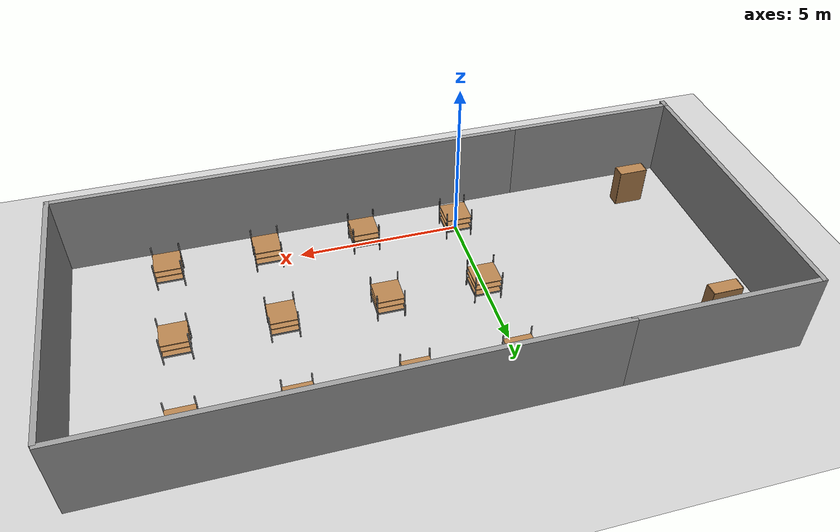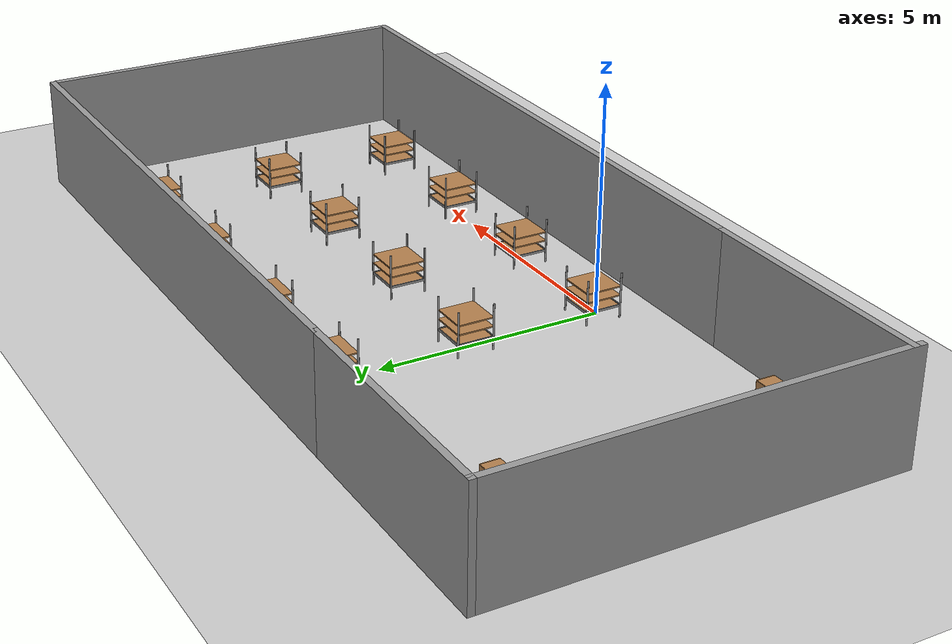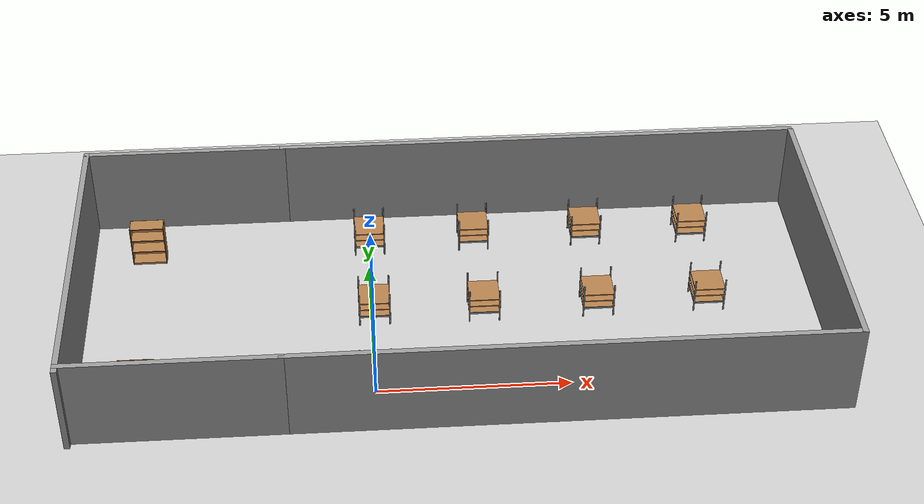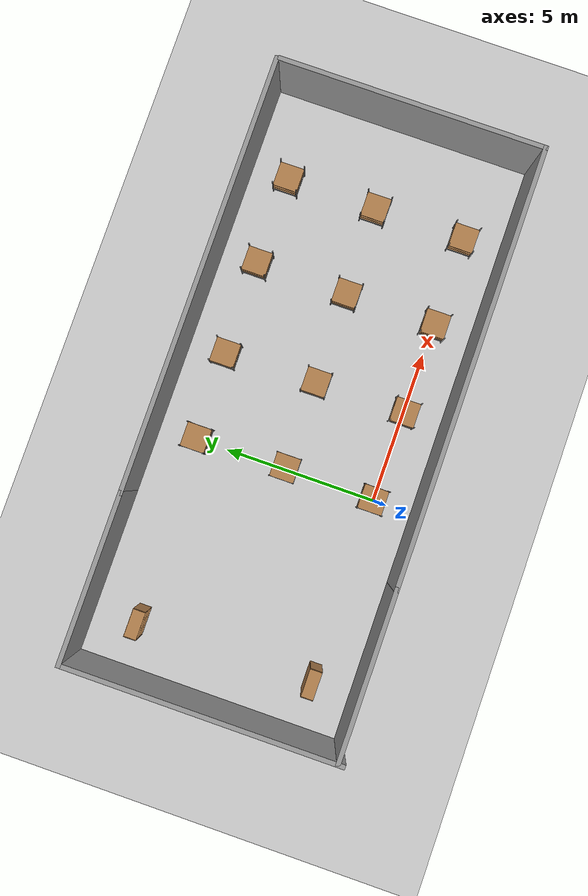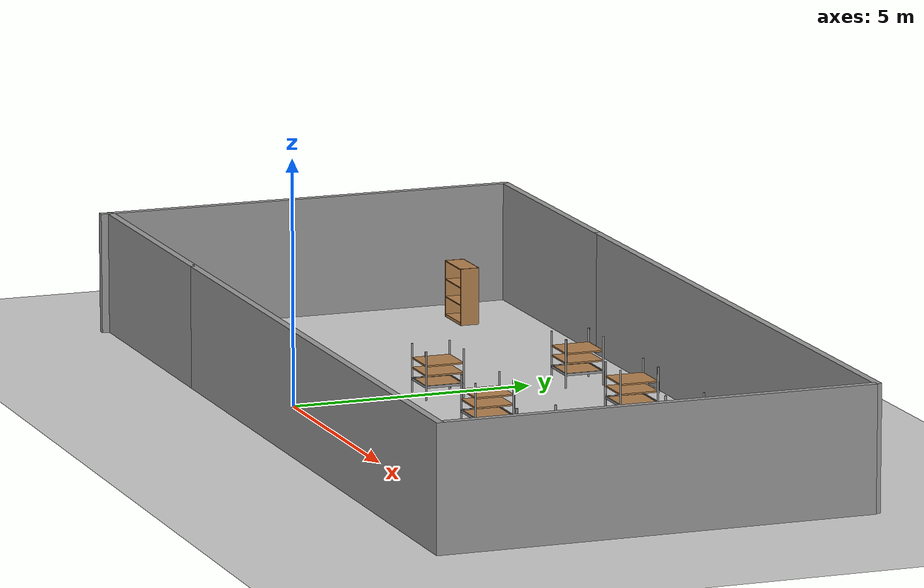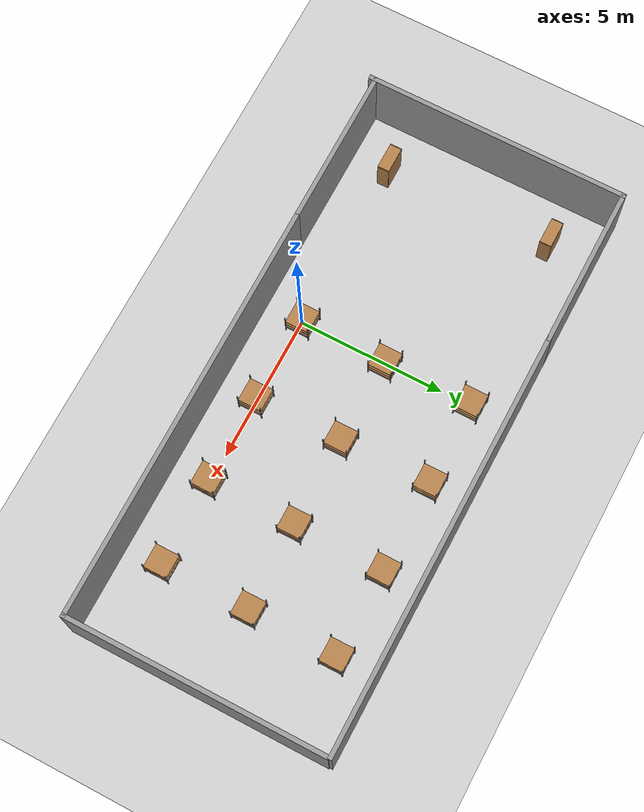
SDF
<sdf version="1.7">
 <world name="default">
  <light name="sun" type="directional">
   <pose>0 0 10 0 -0 0</pose>
   <diffuse>0.8 0.8 0.8 1</diffuse>
   <specular>0.2 0.2 0.2 1</specular>
   <attenuation>
    <range>1000</range>
    <constant>0.9</constant>
    <linear>0.01</linear>
    <quadratic>0.001</quadratic>
   </attenuation>
   <direction>-0.5 0.1 -0.9</direction>
   <spot><inner_angle>0</inner_angle><outer_angle>0</outer_angle><falloff>0</falloff></spot>
  </light>
  <model name="ground_plane">
   <static>1</static>
   <link name="link">
    <collision name="collision">
     <geometry><plane><normal>0 0 1</normal><size>100 100</size></plane></geometry>
     <surface><friction><ode><mu>100</mu><mu2>50</mu2></ode></friction></surface>
    </collision>
    <visual name="visual">
     <cast_shadows>0</cast_shadows>
     <geometry><plane><normal>0 0 1</normal><size>100 100</size></plane></geometry>
     <material>
      <script><uri>file://media/materials/scripts/gazebo.material</uri><name>Gazebo/Grey</name></script>
     </material>
    </visual>
   </link>
  </model>
  <gravity>0 0 -9.8</gravity>
  <magnetic_field>6e-06 2.3e-05 -4.2e-05</magnetic_field>
  <atmosphere type="adiabatic"/>
  <physics type="ode">
   <max_step_size>0.001</max_step_size>
   <real_time_factor>1</real_time_factor>
   <real_time_update_rate>1000</real_time_update_rate>
  </physics>
  <scene><ambient>0.4 0.4 0.4 1</ambient><background>0.7 0.7 0.7 1</background><shadows>1</shadows></scene>
  <audio><device>default</device></audio>
  <spherical_coordinates>
   <surface_model>EARTH_WGS84</surface_model>
   <latitude_deg>0</latitude_deg>
   <longitude_deg>0</longitude_deg>
   <elevation>0</elevation>
   <heading_deg>0</heading_deg>
  </spherical_coordinates>
  <model name="warehouse_pallet_modified_80">
   <link name="warehouse_pallet::link">
    <pose>-0.115127 9.2e-05 0 0 -0 1.57</pose>
    <inertial>
     <inertia>
      <ixx>0.0267042</ixx>
      <ixy>0</ixy>
      <ixz>0</ixz>
      <iyy>0.0937875</iyy>
      <iyz>0</iyz>
      <izz>0.120417</izz>
     </inertia>
     <mass>0.5</mass>
    </inertial>
    <visual name="front_right_leg">
     <pose>0.4 -0.4 0.4 0 -0 0</pose>
     <geometry><cylinder><radius>0.02</radius><length>1</length></cylinder></geometry>
     <material>
      <script><uri>file://media/materials/scripts/gazebo.material</uri><name>Gazebo/Grey</name></script>
      <shader type="pixel"><normal_map>__default__</normal_map></shader>
      <ambient>0.3 0.3 0.3 1</ambient>
      <diffuse>0.7 0.7 0.7 1</diffuse>
      <specular>0.01 0.01 0.01 1</specular>
      <emissive>0 0 0 1</emissive>
     </material>
    </visual>
    <visual name="back_left_leg">
     <pose>-0.4 0.4 0.4 0 -0 0</pose>
     <geometry><cylinder><radius>0.02</radius><length>1</length></cylinder></geometry>
     <material>
      <script><uri>file://media/materials/scripts/gazebo.material</uri><name>Gazebo/Grey</name></script>
      <shader type="pixel"><normal_map>__default__</normal_map></shader>
      <ambient>0.3 0.3 0.3 1</ambient>
      <diffuse>0.7 0.7 0.7 1</diffuse>
      <specular>0.01 0.01 0.01 1</specular>
      <emissive>0 0 0 1</emissive>
     </material>
    </visual>
    <visual name="visual1">
     <pose>0 0 0.165 0 -0 0</pose>
     <geometry><box><size>0.8 0.8 0.03</size></box></geometry>
     <material>
      <script><uri>file://media/materials/scripts/gazebo.material</uri><name>Gazebo/Wood</name></script>
      <shader type="pixel"><normal_map>__default__</normal_map></shader>
      <ambient>1 1 1 1</ambient>
      <diffuse>1 1 1 1</diffuse>
      <specular>0.2 0.2 0.2 1</specular>
      <emissive>0 0 0 1</emissive>
     </material>
    </visual>
    <visual name="front_left_leg">
     <pose>0.4 0.4 0.4 0 -0 0</pose>
     <geometry><cylinder><radius>0.02</radius><length>1</length></cylinder></geometry>
     <material>
      <script><uri>file://media/materials/scripts/gazebo.material</uri><name>Gazebo/Grey</name></script>
      <shader type="pixel"><normal_map>__default__</normal_map></shader>
      <ambient>0.3 0.3 0.3 1</ambient>
      <diffuse>0.7 0.7 0.7 1</diffuse>
      <specular>0.01 0.01 0.01 1</specular>
      <emissive>0 0 0 1</emissive>
     </material>
    </visual>
    <visual name="holding2_visual">
     <pose>0 -0.4 0.175 0 -0 0</pose>
     <geometry><box><size>0.8 0.02 0.05</size></box></geometry>
     <material>
      <script><uri>file://media/materials/scripts/gazebo.material</uri><name>Gazebo/Grey</name></script>
      <shader type="pixel"><normal_map>__default__</normal_map></shader>
      <ambient>0.3 0.3 0.3 1</ambient>
      <diffuse>0.7 0.7 0.7 1</diffuse>
      <specular>0.01 0.01 0.01 1</specular>
      <emissive>0 0 0 1</emissive>
     </material>
    </visual>
    <visual name="visual2">
     <pose>0 0 0.4 0 -0 0</pose>
     <geometry><box><size>0.8 0.8 0.03</size></box></geometry>
     <material>
      <script><uri>file://media/materials/scripts/gazebo.material</uri><name>Gazebo/Wood</name></script>
      <shader type="pixel"><normal_map>__default__</normal_map></shader>
      <ambient>1 1 1 1</ambient>
      <diffuse>1 1 1 1</diffuse>
      <specular>0.2 0.2 0.2 1</specular>
      <emissive>0 0 0 1</emissive>
     </material>
    </visual>
    <visual name="holding4_visual">
     <pose>-0.4 0 0.175 0 -0 1.57</pose>
     <geometry><box><size>0.8 0.02 0.05</size></box></geometry>
     <material>
      <script><uri>file://media/materials/scripts/gazebo.material</uri><name>Gazebo/Grey</name></script>
      <shader type="pixel"><normal_map>__default__</normal_map></shader>
      <ambient>0.3 0.3 0.3 1</ambient>
      <diffuse>0.7 0.7 0.7 1</diffuse>
      <specular>0.01 0.01 0.01 1</specular>
      <emissive>0 0 0 1</emissive>
     </material>
    </visual>
    <visual name="holding1_visual">
     <pose>0 0.4 0.175 0 -0 0</pose>
     <geometry><box><size>0.8 0.02 0.05</size></box></geometry>
     <material>
      <script><uri>file://media/materials/scripts/gazebo.material</uri><name>Gazebo/Grey</name></script>
      <shader type="pixel"><normal_map>__default__</normal_map></shader>
      <ambient>0.3 0.3 0.3 1</ambient>
      <diffuse>0.7 0.7 0.7 1</diffuse>
      <specular>0.01 0.01 0.01 1</specular>
      <emissive>0 0 0 1</emissive>
     </material>
    </visual>
    <visual name="back_right_leg">
     <pose>-0.4 -0.4 0.4 0 -0 0</pose>
     <geometry><cylinder><radius>0.02</radius><length>1</length></cylinder></geometry>
     <material>
      <script><uri>file://media/materials/scripts/gazebo.material</uri><name>Gazebo/Grey</name></script>
      <shader type="pixel"><normal_map>__default__</normal_map></shader>
      <ambient>0.3 0.3 0.3 1</ambient>
      <diffuse>0.7 0.7 0.7 1</diffuse>
      <specular>0.01 0.01 0.01 1</specular>
      <emissive>0 0 0 1</emissive>
     </material>
    </visual>
    <visual name="visual3">
     <pose>0 0 0.6 0 -0 0</pose>
     <geometry><box><size>0.8 0.8 0.03</size></box></geometry>
     <material>
      <script><uri>file://media/materials/scripts/gazebo.material</uri><name>Gazebo/Wood</name></script>
      <shader type="pixel"><normal_map>__default__</normal_map></shader>
      <ambient>1 1 1 1</ambient>
      <diffuse>1 1 1 1</diffuse>
      <specular>0.2 0.2 0.2 1</specular>
      <emissive>0 0 0 1</emissive>
     </material>
    </visual>
    <visual name="holding3_visual">
     <pose>0.4 0 0.175 0 -0 1.57</pose>
     <geometry><box><size>0.8 0.02 0.05</size></box></geometry>
     <material>
      <script><uri>file://media/materials/scripts/gazebo.material</uri><name>Gazebo/Grey</name></script>
      <shader type="pixel"><normal_map>__default__</normal_map></shader>
      <ambient>0.3 0.3 0.3 1</ambient>
      <diffuse>0.7 0.7 0.7 1</diffuse>
      <specular>0.01 0.01 0.01 1</specular>
      <emissive>0 0 0 1</emissive>
     </material>
    </visual>
    <collision name="back_right_leg">
     <pose>-0.4 -0.4 0.4 0 -0 0</pose>
     <geometry><cylinder><radius>0.02</radius><length>1</length></cylinder></geometry>
     <surface>
      <friction>
       <ode><mu>1</mu><mu2>1</mu2><fdir1>0 0 0</fdir1><slip1>0</slip1><slip2>0</slip2></ode>
       <torsional>
        <coefficient>1</coefficient>
        <patch_radius>0</patch_radius>
        <surface_radius>0</surface_radius>
        <use_patch_radius>1</use_patch_radius>
        <ode><slip>0</slip></ode>
       </torsional>
      </friction>
      <bounce><restitution_coefficient>0</restitution_coefficient><threshold>1e+06</threshold></bounce>
      <contact>
       <collide_without_contact>0</collide_without_contact>
       <collide_without_contact_bitmask>1</collide_without_contact_bitmask>
       <collide_bitmask>1</collide_bitmask>
       <ode>
        <soft_cfm>0</soft_cfm>
        <soft_erp>0.2</soft_erp>
        <kp>1e+13</kp>
        <kd>1</kd>
        <max_vel>0.01</max_vel>
        <min_depth>0</min_depth>
       </ode>
       <bullet>
        <split_impulse>1</split_impulse>
        <split_impulse_penetration_threshold>-0.01</split_impulse_penetration_threshold>
        <soft_cfm>0</soft_cfm>
        <soft_erp>0.2</soft_erp>
        <kp>1e+13</kp>
        <kd>1</kd>
       </bullet>
      </contact>
     </surface>
    </collision>
    <collision name="holding2_collision">
     <pose>0 -0.4 0.175 0 -0 0</pose>
     <geometry><box><size>0.8 0.02 0.05</size></box></geometry>
     <surface>
      <friction>
       <ode><mu>1e+09</mu><mu2>1e+09</mu2><fdir1>0 0 0</fdir1><slip1>0</slip1><slip2>0</slip2></ode>
       <torsional>
        <coefficient>1</coefficient>
        <patch_radius>0</patch_radius>
        <surface_radius>0</surface_radius>
        <use_patch_radius>1</use_patch_radius>
        <ode><slip>0</slip></ode>
       </torsional>
      </friction>
      <bounce><restitution_coefficient>0</restitution_coefficient><threshold>1e+06</threshold></bounce>
      <contact>
       <collide_without_contact>0</collide_without_contact>
       <collide_without_contact_bitmask>1</collide_without_contact_bitmask>
       <collide_bitmask>1</collide_bitmask>
       <ode>
        <soft_cfm>0</soft_cfm>
        <soft_erp>0.2</soft_erp>
        <kp>1e+13</kp>
        <kd>1</kd>
        <max_vel>0.01</max_vel>
        <min_depth>0</min_depth>
       </ode>
       <bullet>
        <split_impulse>1</split_impulse>
        <split_impulse_penetration_threshold>-0.01</split_impulse_penetration_threshold>
        <soft_cfm>0</soft_cfm>
        <soft_erp>0.2</soft_erp>
        <kp>1e+13</kp>
        <kd>1</kd>
       </bullet>
      </contact>
     </surface>
    </collision>
    <collision name="holding4_collision">
     <pose>-0.4 0 0.175 0 -0 1.57</pose>
     <geometry><box><size>0.8 0.02 0.05</size></box></geometry>
     <surface>
      <friction>
       <ode><mu>1e+09</mu><mu2>1e+09</mu2><fdir1>0 0 0</fdir1><slip1>0</slip1><slip2>0</slip2></ode>
       <torsional>
        <coefficient>1</coefficient>
        <patch_radius>0</patch_radius>
        <surface_radius>0</surface_radius>
        <use_patch_radius>1</use_patch_radius>
        <ode><slip>0</slip></ode>
       </torsional>
      </friction>
      <bounce><restitution_coefficient>0</restitution_coefficient><threshold>1e+06</threshold></bounce>
      <contact>
       <collide_without_contact>0</collide_without_contact>
       <collide_without_contact_bitmask>1</collide_without_contact_bitmask>
       <collide_bitmask>1</collide_bitmask>
       <ode>
        <soft_cfm>0</soft_cfm>
        <soft_erp>0.2</soft_erp>
        <kp>1e+13</kp>
        <kd>1</kd>
        <max_vel>0.01</max_vel>
        <min_depth>0</min_depth>
       </ode>
       <bullet>
        <split_impulse>1</split_impulse>
        <split_impulse_penetration_threshold>-0.01</split_impulse_penetration_threshold>
        <soft_cfm>0</soft_cfm>
        <soft_erp>0.2</soft_erp>
        <kp>1e+13</kp>
        <kd>1</kd>
       </bullet>
      </contact>
     </surface>
    </collision>
    <collision name="front_right_leg">
     <pose>0.4 -0.4 0.4 0 -0 0</pose>
     <geometry><cylinder><radius>0.02</radius><length>1</length></cylinder></geometry>
     <surface>
      <friction>
       <ode><mu>1</mu><mu2>1.2</mu2><fdir1>0 0 0</fdir1><slip1>0</slip1><slip2>0</slip2></ode>
       <torsional>
        <coefficient>1</coefficient>
        <patch_radius>0</patch_radius>
        <surface_radius>0</surface_radius>
        <use_patch_radius>1</use_patch_radius>
        <ode><slip>0</slip></ode>
       </torsional>
      </friction>
      <bounce><restitution_coefficient>0</restitution_coefficient><threshold>1e+06</threshold></bounce>
      <contact>
       <collide_without_contact>0</collide_without_contact>
       <collide_without_contact_bitmask>1</collide_without_contact_bitmask>
       <collide_bitmask>1</collide_bitmask>
       <ode>
        <soft_cfm>0</soft_cfm>
        <soft_erp>0.2</soft_erp>
        <kp>1e+13</kp>
        <kd>1</kd>
        <max_vel>0.01</max_vel>
        <min_depth>0</min_depth>
       </ode>
       <bullet>
        <split_impulse>1</split_impulse>
        <split_impulse_penetration_threshold>-0.01</split_impulse_penetration_threshold>
        <soft_cfm>0</soft_cfm>
        <soft_erp>0.2</soft_erp>
        <kp>1e+13</kp>
        <kd>1</kd>
       </bullet>
      </contact>
     </surface>
    </collision>
    <collision name="surface3">
     <pose>0 0 0.6 0 -0 0</pose>
     <geometry><box><size>0.8 0.8 0.03</size></box></geometry>
     <surface>
      <friction>
       <ode><mu>2.5</mu><mu2>2.5</mu2><fdir1>0 0 0</fdir1><slip1>0</slip1><slip2>0</slip2></ode>
       <torsional>
        <coefficient>1</coefficient>
        <patch_radius>0</patch_radius>
        <surface_radius>0</surface_radius>
        <use_patch_radius>1</use_patch_radius>
        <ode><slip>0</slip></ode>
       </torsional>
      </friction>
      <bounce><restitution_coefficient>0</restitution_coefficient><threshold>1e+06</threshold></bounce>
      <contact>
       <collide_without_contact>0</collide_without_contact>
       <collide_without_contact_bitmask>1</collide_without_contact_bitmask>
       <collide_bitmask>1</collide_bitmask>
       <ode>
        <soft_cfm>0</soft_cfm>
        <soft_erp>0.2</soft_erp>
        <kp>1e+13</kp>
        <kd>1</kd>
        <max_vel>0.01</max_vel>
        <min_depth>0</min_depth>
       </ode>
       <bullet>
        <split_impulse>1</split_impulse>
        <split_impulse_penetration_threshold>-0.01</split_impulse_penetration_threshold>
        <soft_cfm>0</soft_cfm>
        <soft_erp>0.2</soft_erp>
        <kp>1e+13</kp>
        <kd>1</kd>
       </bullet>
      </contact>
     </surface>
    </collision>
    <collision name="surface1">
     <pose>0 0 0.165 0 -0 0</pose>
     <geometry><box><size>0.8 0.8 0.03</size></box></geometry>
     <surface>
      <friction>
       <ode><mu>20</mu><mu2>20</mu2><fdir1>0 0 0</fdir1><slip1>0</slip1><slip2>0</slip2></ode>
       <torsional>
        <coefficient>1</coefficient>
        <patch_radius>0</patch_radius>
        <surface_radius>0</surface_radius>
        <use_patch_radius>1</use_patch_radius>
        <ode><slip>0</slip></ode>
       </torsional>
      </friction>
      <bounce><restitution_coefficient>0</restitution_coefficient><threshold>1e+06</threshold></bounce>
      <contact>
       <collide_without_contact>0</collide_without_contact>
       <collide_without_contact_bitmask>1</collide_without_contact_bitmask>
       <collide_bitmask>1</collide_bitmask>
       <ode>
        <soft_cfm>0</soft_cfm>
        <soft_erp>0.2</soft_erp>
        <kp>1e+13</kp>
        <kd>1</kd>
        <max_vel>0.01</max_vel>
        <min_depth>0</min_depth>
       </ode>
       <bullet>
        <split_impulse>1</split_impulse>
        <split_impulse_penetration_threshold>-0.01</split_impulse_penetration_threshold>
        <soft_cfm>0</soft_cfm>
        <soft_erp>0.2</soft_erp>
        <kp>1e+13</kp>
        <kd>1</kd>
       </bullet>
      </contact>
     </surface>
    </collision>
    <collision name="holding1_collision">
     <pose>0 0.4 0.175 0 -0 0</pose>
     <geometry><box><size>0.8 0.02 0.05</size></box></geometry>
     <surface>
      <friction>
       <ode><mu>1e+09</mu><mu2>1e+09</mu2><fdir1>0 0 0</fdir1><slip1>0</slip1><slip2>0</slip2></ode>
       <torsional>
        <coefficient>1</coefficient>
        <patch_radius>0</patch_radius>
        <surface_radius>0</surface_radius>
        <use_patch_radius>1</use_patch_radius>
        <ode><slip>0</slip></ode>
       </torsional>
      </friction>
      <bounce><restitution_coefficient>0</restitution_coefficient><threshold>1e+06</threshold></bounce>
      <contact>
       <collide_without_contact>0</collide_without_contact>
       <collide_without_contact_bitmask>1</collide_without_contact_bitmask>
       <collide_bitmask>1</collide_bitmask>
       <ode>
        <soft_cfm>0</soft_cfm>
        <soft_erp>0.2</soft_erp>
        <kp>1e+13</kp>
        <kd>1</kd>
        <max_vel>0.01</max_vel>
        <min_depth>0</min_depth>
       </ode>
       <bullet>
        <split_impulse>1</split_impulse>
        <split_impulse_penetration_threshold>-0.01</split_impulse_penetration_threshold>
        <soft_cfm>0</soft_cfm>
        <soft_erp>0.2</soft_erp>
        <kp>1e+13</kp>
        <kd>1</kd>
       </bullet>
      </contact>
     </surface>
    </collision>
    <collision name="back_left_leg">
     <pose>-0.4 0.4 0.4 0 -0 0</pose>
     <geometry><cylinder><radius>0.02</radius><length>1</length></cylinder></geometry>
     <surface>
      <friction>
       <ode><mu>1</mu><mu2>1</mu2><fdir1>0 0 0</fdir1><slip1>0</slip1><slip2>0</slip2></ode>
       <torsional>
        <coefficient>1</coefficient>
        <patch_radius>0</patch_radius>
        <surface_radius>0</surface_radius>
        <use_patch_radius>1</use_patch_radius>
        <ode><slip>0</slip></ode>
       </torsional>
      </friction>
      <bounce><restitution_coefficient>0</restitution_coefficient><threshold>1e+06</threshold></bounce>
      <contact>
       <collide_without_contact>0</collide_without_contact>
       <collide_without_contact_bitmask>1</collide_without_contact_bitmask>
       <collide_bitmask>1</collide_bitmask>
       <ode>
        <soft_cfm>0</soft_cfm>
        <soft_erp>0.2</soft_erp>
        <kp>1e+13</kp>
        <kd>1</kd>
        <max_vel>0.01</max_vel>
        <min_depth>0</min_depth>
       </ode>
       <bullet>
        <split_impulse>1</split_impulse>
        <split_impulse_penetration_threshold>-0.01</split_impulse_penetration_threshold>
        <soft_cfm>0</soft_cfm>
        <soft_erp>0.2</soft_erp>
        <kp>1e+13</kp>
        <kd>1</kd>
       </bullet>
      </contact>
     </surface>
    </collision>
    <collision name="holding3_collision">
     <pose>0.4 0 0.175 0 -0 1.57</pose>
     <geometry><box><size>0.8 0.02 0.05</size></box></geometry>
     <surface>
      <friction>
       <ode><mu>1e+09</mu><mu2>1e+09</mu2><fdir1>0 0 0</fdir1><slip1>0</slip1><slip2>0</slip2></ode>
       <torsional>
        <coefficient>1</coefficient>
        <patch_radius>0</patch_radius>
        <surface_radius>0</surface_radius>
        <use_patch_radius>1</use_patch_radius>
        <ode><slip>0</slip></ode>
       </torsional>
      </friction>
      <bounce><restitution_coefficient>0</restitution_coefficient><threshold>1e+06</threshold></bounce>
      <contact>
       <collide_without_contact>0</collide_without_contact>
       <collide_without_contact_bitmask>1</collide_without_contact_bitmask>
       <collide_bitmask>1</collide_bitmask>
       <ode>
        <soft_cfm>0</soft_cfm>
        <soft_erp>0.2</soft_erp>
        <kp>1e+13</kp>
        <kd>1</kd>
        <max_vel>0.01</max_vel>
        <min_depth>0</min_depth>
       </ode>
       <bullet>
        <split_impulse>1</split_impulse>
        <split_impulse_penetration_threshold>-0.01</split_impulse_penetration_threshold>
        <soft_cfm>0</soft_cfm>
        <soft_erp>0.2</soft_erp>
        <kp>1e+13</kp>
        <kd>1</kd>
       </bullet>
      </contact>
     </surface>
    </collision>
    <collision name="surface2">
     <pose>0 0 0.4 0 -0 0</pose>
     <geometry><box><size>0.8 0.8 0.03</size></box></geometry>
     <surface>
      <friction>
       <ode><mu>2.5</mu><mu2>2.5</mu2><fdir1>0 0 0</fdir1><slip1>0</slip1><slip2>0</slip2></ode>
       <torsional>
        <coefficient>1</coefficient>
        <patch_radius>0</patch_radius>
        <surface_radius>0</surface_radius>
        <use_patch_radius>1</use_patch_radius>
        <ode><slip>0</slip></ode>
       </torsional>
      </friction>
      <bounce><restitution_coefficient>0</restitution_coefficient><threshold>1e+06</threshold></bounce>
      <contact>
       <collide_without_contact>0</collide_without_contact>
       <collide_without_contact_bitmask>1</collide_without_contact_bitmask>
       <collide_bitmask>1</collide_bitmask>
       <ode>
        <soft_cfm>0</soft_cfm>
        <soft_erp>0.2</soft_erp>
        <kp>1e+13</kp>
        <kd>1</kd>
        <max_vel>0.01</max_vel>
        <min_depth>0</min_depth>
       </ode>
       <bullet>
        <split_impulse>1</split_impulse>
        <split_impulse_penetration_threshold>-0.01</split_impulse_penetration_threshold>
        <soft_cfm>0</soft_cfm>
        <soft_erp>0.2</soft_erp>
        <kp>1e+13</kp>
        <kd>1</kd>
       </bullet>
      </contact>
     </surface>
    </collision>
    <collision name="front_left_leg">
     <pose>0.4 0.4 0.4 0 -0 0</pose>
     <geometry><cylinder><radius>0.02</radius><length>1</length></cylinder></geometry>
     <surface>
      <friction>
       <ode><mu>1</mu><mu2>1</mu2><fdir1>0 0 0</fdir1><slip1>0</slip1><slip2>0</slip2></ode>
       <torsional>
        <coefficient>1</coefficient>
        <patch_radius>0</patch_radius>
        <surface_radius>0</surface_radius>
        <use_patch_radius>1</use_patch_radius>
        <ode><slip>0</slip></ode>
       </torsional>
      </friction>
      <bounce><restitution_coefficient>0</restitution_coefficient><threshold>1e+06</threshold></bounce>
      <contact>
       <collide_without_contact>0</collide_without_contact>
       <collide_without_contact_bitmask>1</collide_without_contact_bitmask>
       <collide_bitmask>1</collide_bitmask>
       <ode>
        <soft_cfm>0</soft_cfm>
        <soft_erp>0.2</soft_erp>
        <kp>1e+13</kp>
        <kd>1</kd>
        <max_vel>0.01</max_vel>
        <min_depth>0</min_depth>
       </ode>
       <bullet>
        <split_impulse>1</split_impulse>
        <split_impulse_penetration_threshold>-0.01</split_impulse_penetration_threshold>
        <soft_cfm>0</soft_cfm>
        <soft_erp>0.2</soft_erp>
        <kp>1e+13</kp>
        <kd>1</kd>
       </bullet>
      </contact>
     </surface>
    </collision>
   </link>
   <static>0</static>
   <pose>0.145072 0.060395 0.099988 -0 2.3e-05 -0.000242</pose>
  </model>
  <model name="warehouse_pallet_modified_80_0">
   <link name="warehouse_pallet::link">
    <pose>-0.115127 9.2e-05 0 0 -0 1.57</pose>
    <inertial>
     <inertia>
      <ixx>0.0267042</ixx>
      <ixy>0</ixy>
      <ixz>0</ixz>
      <iyy>0.0937875</iyy>
      <iyz>0</iyz>
      <izz>0.120417</izz>
     </inertia>
     <mass>0.5</mass>
    </inertial>
    <visual name="front_right_leg">
     <pose>0.4 -0.4 0.4 0 -0 0</pose>
     <geometry><cylinder><radius>0.02</radius><length>1</length></cylinder></geometry>
     <material>
      <script><uri>file://media/materials/scripts/gazebo.material</uri><name>Gazebo/Grey</name></script>
      <shader type="pixel"><normal_map>__default__</normal_map></shader>
      <ambient>0.3 0.3 0.3 1</ambient>
      <diffuse>0.7 0.7 0.7 1</diffuse>
      <specular>0.01 0.01 0.01 1</specular>
      <emissive>0 0 0 1</emissive>
     </material>
    </visual>
    <visual name="back_left_leg">
     <pose>-0.4 0.4 0.4 0 -0 0</pose>
     <geometry><cylinder><radius>0.02</radius><length>1</length></cylinder></geometry>
     <material>
      <script><uri>file://media/materials/scripts/gazebo.material</uri><name>Gazebo/Grey</name></script>
      <shader type="pixel"><normal_map>__default__</normal_map></shader>
      <ambient>0.3 0.3 0.3 1</ambient>
      <diffuse>0.7 0.7 0.7 1</diffuse>
      <specular>0.01 0.01 0.01 1</specular>
      <emissive>0 0 0 1</emissive>
     </material>
    </visual>
    <visual name="visual1">
     <pose>0 0 0.165 0 -0 0</pose>
     <geometry><box><size>0.8 0.8 0.03</size></box></geometry>
     <material>
      <script><uri>file://media/materials/scripts/gazebo.material</uri><name>Gazebo/Wood</name></script>
      <shader type="pixel"><normal_map>__default__</normal_map></shader>
      <ambient>1 1 1 1</ambient>
      <diffuse>1 1 1 1</diffuse>
      <specular>0.2 0.2 0.2 1</specular>
      <emissive>0 0 0 1</emissive>
     </material>
    </visual>
    <visual name="front_left_leg">
     <pose>0.4 0.4 0.4 0 -0 0</pose>
     <geometry><cylinder><radius>0.02</radius><length>1</length></cylinder></geometry>
     <material>
      <script><uri>file://media/materials/scripts/gazebo.material</uri><name>Gazebo/Grey</name></script>
      <shader type="pixel"><normal_map>__default__</normal_map></shader>
      <ambient>0.3 0.3 0.3 1</ambient>
      <diffuse>0.7 0.7 0.7 1</diffuse>
      <specular>0.01 0.01 0.01 1</specular>
      <emissive>0 0 0 1</emissive>
     </material>
    </visual>
    <visual name="holding2_visual">
     <pose>0 -0.4 0.175 0 -0 0</pose>
     <geometry><box><size>0.8 0.02 0.05</size></box></geometry>
     <material>
      <script><uri>file://media/materials/scripts/gazebo.material</uri><name>Gazebo/Grey</name></script>
      <shader type="pixel"><normal_map>__default__</normal_map></shader>
      <ambient>0.3 0.3 0.3 1</ambient>
      <diffuse>0.7 0.7 0.7 1</diffuse>
      <specular>0.01 0.01 0.01 1</specular>
      <emissive>0 0 0 1</emissive>
     </material>
    </visual>
    <visual name="visual2">
     <pose>0 0 0.4 0 -0 0</pose>
     <geometry><box><size>0.8 0.8 0.03</size></box></geometry>
     <material>
      <script><uri>file://media/materials/scripts/gazebo.material</uri><name>Gazebo/Wood</name></script>
      <shader type="pixel"><normal_map>__default__</normal_map></shader>
      <ambient>1 1 1 1</ambient>
      <diffuse>1 1 1 1</diffuse>
      <specular>0.2 0.2 0.2 1</specular>
      <emissive>0 0 0 1</emissive>
     </material>
    </visual>
    <visual name="holding4_visual">
     <pose>-0.4 0 0.175 0 -0 1.57</pose>
     <geometry><box><size>0.8 0.02 0.05</size></box></geometry>
     <material>
      <script><uri>file://media/materials/scripts/gazebo.material</uri><name>Gazebo/Grey</name></script>
      <shader type="pixel"><normal_map>__default__</normal_map></shader>
      <ambient>0.3 0.3 0.3 1</ambient>
      <diffuse>0.7 0.7 0.7 1</diffuse>
      <specular>0.01 0.01 0.01 1</specular>
      <emissive>0 0 0 1</emissive>
     </material>
    </visual>
    <visual name="holding1_visual">
     <pose>0 0.4 0.175 0 -0 0</pose>
     <geometry><box><size>0.8 0.02 0.05</size></box></geometry>
     <material>
      <script><uri>file://media/materials/scripts/gazebo.material</uri><name>Gazebo/Grey</name></script>
      <shader type="pixel"><normal_map>__default__</normal_map></shader>
      <ambient>0.3 0.3 0.3 1</ambient>
      <diffuse>0.7 0.7 0.7 1</diffuse>
      <specular>0.01 0.01 0.01 1</specular>
      <emissive>0 0 0 1</emissive>
     </material>
    </visual>
    <visual name="back_right_leg">
     <pose>-0.4 -0.4 0.4 0 -0 0</pose>
     <geometry><cylinder><radius>0.02</radius><length>1</length></cylinder></geometry>
     <material>
      <script><uri>file://media/materials/scripts/gazebo.material</uri><name>Gazebo/Grey</name></script>
      <shader type="pixel"><normal_map>__default__</normal_map></shader>
      <ambient>0.3 0.3 0.3 1</ambient>
      <diffuse>0.7 0.7 0.7 1</diffuse>
      <specular>0.01 0.01 0.01 1</specular>
      <emissive>0 0 0 1</emissive>
     </material>
    </visual>
    <visual name="visual3">
     <pose>0 0 0.6 0 -0 0</pose>
     <geometry><box><size>0.8 0.8 0.03</size></box></geometry>
     <material>
      <script><uri>file://media/materials/scripts/gazebo.material</uri><name>Gazebo/Wood</name></script>
      <shader type="pixel"><normal_map>__default__</normal_map></shader>
      <ambient>1 1 1 1</ambient>
      <diffuse>1 1 1 1</diffuse>
      <specular>0.2 0.2 0.2 1</specular>
      <emissive>0 0 0 1</emissive>
     </material>
    </visual>
    <visual name="holding3_visual">
     <pose>0.4 0 0.175 0 -0 1.57</pose>
     <geometry><box><size>0.8 0.02 0.05</size></box></geometry>
     <material>
      <script><uri>file://media/materials/scripts/gazebo.material</uri><name>Gazebo/Grey</name></script>
      <shader type="pixel"><normal_map>__default__</normal_map></shader>
      <ambient>0.3 0.3 0.3 1</ambient>
      <diffuse>0.7 0.7 0.7 1</diffuse>
      <specular>0.01 0.01 0.01 1</specular>
      <emissive>0 0 0 1</emissive>
     </material>
    </visual>
    <collision name="back_right_leg">
     <pose>-0.4 -0.4 0.4 0 -0 0</pose>
     <geometry><cylinder><radius>0.02</radius><length>1</length></cylinder></geometry>
     <surface>
      <friction>
       <ode><mu>1</mu><mu2>1</mu2><fdir1>0 0 0</fdir1><slip1>0</slip1><slip2>0</slip2></ode>
       <torsional>
        <coefficient>1</coefficient>
        <patch_radius>0</patch_radius>
        <surface_radius>0</surface_radius>
        <use_patch_radius>1</use_patch_radius>
        <ode><slip>0</slip></ode>
       </torsional>
      </friction>
      <bounce><restitution_coefficient>0</restitution_coefficient><threshold>1e+06</threshold></bounce>
      <contact>
       <collide_without_contact>0</collide_without_contact>
       <collide_without_contact_bitmask>1</collide_without_contact_bitmask>
       <collide_bitmask>1</collide_bitmask>
       <ode>
        <soft_cfm>0</soft_cfm>
        <soft_erp>0.2</soft_erp>
        <kp>1e+13</kp>
        <kd>1</kd>
        <max_vel>0.01</max_vel>
        <min_depth>0</min_depth>
       </ode>
       <bullet>
        <split_impulse>1</split_impulse>
        <split_impulse_penetration_threshold>-0.01</split_impulse_penetration_threshold>
        <soft_cfm>0</soft_cfm>
        <soft_erp>0.2</soft_erp>
        <kp>1e+13</kp>
        <kd>1</kd>
       </bullet>
      </contact>
     </surface>
    </collision>
    <collision name="holding2_collision">
     <pose>0 -0.4 0.175 0 -0 0</pose>
     <geometry><box><size>0.8 0.02 0.05</size></box></geometry>
     <surface>
      <friction>
       <ode><mu>1e+09</mu><mu2>1e+09</mu2><fdir1>0 0 0</fdir1><slip1>0</slip1><slip2>0</slip2></ode>
       <torsional>
        <coefficient>1</coefficient>
        <patch_radius>0</patch_radius>
        <surface_radius>0</surface_radius>
        <use_patch_radius>1</use_patch_radius>
        <ode><slip>0</slip></ode>
       </torsional>
      </friction>
      <bounce><restitution_coefficient>0</restitution_coefficient><threshold>1e+06</threshold></bounce>
      <contact>
       <collide_without_contact>0</collide_without_contact>
       <collide_without_contact_bitmask>1</collide_without_contact_bitmask>
       <collide_bitmask>1</collide_bitmask>
       <ode>
        <soft_cfm>0</soft_cfm>
        <soft_erp>0.2</soft_erp>
        <kp>1e+13</kp>
        <kd>1</kd>
        <max_vel>0.01</max_vel>
        <min_depth>0</min_depth>
       </ode>
       <bullet>
        <split_impulse>1</split_impulse>
        <split_impulse_penetration_threshold>-0.01</split_impulse_penetration_threshold>
        <soft_cfm>0</soft_cfm>
        <soft_erp>0.2</soft_erp>
        <kp>1e+13</kp>
        <kd>1</kd>
       </bullet>
      </contact>
     </surface>
    </collision>
    <collision name="holding4_collision">
     <pose>-0.4 0 0.175 0 -0 1.57</pose>
     <geometry><box><size>0.8 0.02 0.05</size></box></geometry>
     <surface>
      <friction>
       <ode><mu>1e+09</mu><mu2>1e+09</mu2><fdir1>0 0 0</fdir1><slip1>0</slip1><slip2>0</slip2></ode>
       <torsional>
        <coefficient>1</coefficient>
        <patch_radius>0</patch_radius>
        <surface_radius>0</surface_radius>
        <use_patch_radius>1</use_patch_radius>
        <ode><slip>0</slip></ode>
       </torsional>
      </friction>
      <bounce><restitution_coefficient>0</restitution_coefficient><threshold>1e+06</threshold></bounce>
      <contact>
       <collide_without_contact>0</collide_without_contact>
       <collide_without_contact_bitmask>1</collide_without_contact_bitmask>
       <collide_bitmask>1</collide_bitmask>
       <ode>
        <soft_cfm>0</soft_cfm>
        <soft_erp>0.2</soft_erp>
        <kp>1e+13</kp>
        <kd>1</kd>
        <max_vel>0.01</max_vel>
        <min_depth>0</min_depth>
       </ode>
       <bullet>
        <split_impulse>1</split_impulse>
        <split_impulse_penetration_threshold>-0.01</split_impulse_penetration_threshold>
        <soft_cfm>0</soft_cfm>
        <soft_erp>0.2</soft_erp>
        <kp>1e+13</kp>
        <kd>1</kd>
       </bullet>
      </contact>
     </surface>
    </collision>
    <collision name="front_right_leg">
     <pose>0.4 -0.4 0.4 0 -0 0</pose>
     <geometry><cylinder><radius>0.02</radius><length>1</length></cylinder></geometry>
     <surface>
      <friction>
       <ode><mu>1</mu><mu2>1.2</mu2><fdir1>0 0 0</fdir1><slip1>0</slip1><slip2>0</slip2></ode>
       <torsional>
        <coefficient>1</coefficient>
        <patch_radius>0</patch_radius>
        <surface_radius>0</surface_radius>
        <use_patch_radius>1</use_patch_radius>
        <ode><slip>0</slip></ode>
       </torsional>
      </friction>
      <bounce><restitution_coefficient>0</restitution_coefficient><threshold>1e+06</threshold></bounce>
      <contact>
       <collide_without_contact>0</collide_without_contact>
       <collide_without_contact_bitmask>1</collide_without_contact_bitmask>
       <collide_bitmask>1</collide_bitmask>
       <ode>
        <soft_cfm>0</soft_cfm>
        <soft_erp>0.2</soft_erp>
        <kp>1e+13</kp>
        <kd>1</kd>
        <max_vel>0.01</max_vel>
        <min_depth>0</min_depth>
       </ode>
       <bullet>
        <split_impulse>1</split_impulse>
        <split_impulse_penetration_threshold>-0.01</split_impulse_penetration_threshold>
        <soft_cfm>0</soft_cfm>
        <soft_erp>0.2</soft_erp>
        <kp>1e+13</kp>
        <kd>1</kd>
       </bullet>
      </contact>
     </surface>
    </collision>
    <collision name="surface3">
     <pose>0 0 0.6 0 -0 0</pose>
     <geometry><box><size>0.8 0.8 0.03</size></box></geometry>
     <surface>
      <friction>
       <ode><mu>2.5</mu><mu2>2.5</mu2><fdir1>0 0 0</fdir1><slip1>0</slip1><slip2>0</slip2></ode>
       <torsional>
        <coefficient>1</coefficient>
        <patch_radius>0</patch_radius>
        <surface_radius>0</surface_radius>
        <use_patch_radius>1</use_patch_radius>
        <ode><slip>0</slip></ode>
       </torsional>
      </friction>
      <bounce><restitution_coefficient>0</restitution_coefficient><threshold>1e+06</threshold></bounce>
      <contact>
       <collide_without_contact>0</collide_without_contact>
       <collide_without_contact_bitmask>1</collide_without_contact_bitmask>
       <collide_bitmask>1</collide_bitmask>
       <ode>
        <soft_cfm>0</soft_cfm>
        <soft_erp>0.2</soft_erp>
        <kp>1e+13</kp>
        <kd>1</kd>
        <max_vel>0.01</max_vel>
        <min_depth>0</min_depth>
       </ode>
       <bullet>
        <split_impulse>1</split_impulse>
        <split_impulse_penetration_threshold>-0.01</split_impulse_penetration_threshold>
        <soft_cfm>0</soft_cfm>
        <soft_erp>0.2</soft_erp>
        <kp>1e+13</kp>
        <kd>1</kd>
       </bullet>
      </contact>
     </surface>
    </collision>
    <collision name="surface1">
     <pose>0 0 0.165 0 -0 0</pose>
     <geometry><box><size>0.8 0.8 0.03</size></box></geometry>
     <surface>
      <friction>
       <ode><mu>20</mu><mu2>20</mu2><fdir1>0 0 0</fdir1><slip1>0</slip1><slip2>0</slip2></ode>
       <torsional>
        <coefficient>1</coefficient>
        <patch_radius>0</patch_radius>
        <surface_radius>0</surface_radius>
        <use_patch_radius>1</use_patch_radius>
        <ode><slip>0</slip></ode>
       </torsional>
      </friction>
      <bounce><restitution_coefficient>0</restitution_coefficient><threshold>1e+06</threshold></bounce>
      <contact>
       <collide_without_contact>0</collide_without_contact>
       <collide_without_contact_bitmask>1</collide_without_contact_bitmask>
       <collide_bitmask>1</collide_bitmask>
       <ode>
        <soft_cfm>0</soft_cfm>
        <soft_erp>0.2</soft_erp>
        <kp>1e+13</kp>
        <kd>1</kd>
        <max_vel>0.01</max_vel>
        <min_depth>0</min_depth>
       </ode>
       <bullet>
        <split_impulse>1</split_impulse>
        <split_impulse_penetration_threshold>-0.01</split_impulse_penetration_threshold>
        <soft_cfm>0</soft_cfm>
        <soft_erp>0.2</soft_erp>
        <kp>1e+13</kp>
        <kd>1</kd>
       </bullet>
      </contact>
     </surface>
    </collision>
    <collision name="holding1_collision">
     <pose>0 0.4 0.175 0 -0 0</pose>
     <geometry><box><size>0.8 0.02 0.05</size></box></geometry>
     <surface>
      <friction>
       <ode><mu>1e+09</mu><mu2>1e+09</mu2><fdir1>0 0 0</fdir1><slip1>0</slip1><slip2>0</slip2></ode>
       <torsional>
        <coefficient>1</coefficient>
        <patch_radius>0</patch_radius>
        <surface_radius>0</surface_radius>
        <use_patch_radius>1</use_patch_radius>
        <ode><slip>0</slip></ode>
       </torsional>
      </friction>
      <bounce><restitution_coefficient>0</restitution_coefficient><threshold>1e+06</threshold></bounce>
      <contact>
       <collide_without_contact>0</collide_without_contact>
       <collide_without_contact_bitmask>1</collide_without_contact_bitmask>
       <collide_bitmask>1</collide_bitmask>
       <ode>
        <soft_cfm>0</soft_cfm>
        <soft_erp>0.2</soft_erp>
        <kp>1e+13</kp>
        <kd>1</kd>
        <max_vel>0.01</max_vel>
        <min_depth>0</min_depth>
       </ode>
       <bullet>
        <split_impulse>1</split_impulse>
        <split_impulse_penetration_threshold>-0.01</split_impulse_penetration_threshold>
        <soft_cfm>0</soft_cfm>
        <soft_erp>0.2</soft_erp>
        <kp>1e+13</kp>
        <kd>1</kd>
       </bullet>
      </contact>
     </surface>
    </collision>
    <collision name="back_left_leg">
     <pose>-0.4 0.4 0.4 0 -0 0</pose>
     <geometry><cylinder><radius>0.02</radius><length>1</length></cylinder></geometry>
     <surface>
      <friction>
       <ode><mu>1</mu><mu2>1</mu2><fdir1>0 0 0</fdir1><slip1>0</slip1><slip2>0</slip2></ode>
       <torsional>
        <coefficient>1</coefficient>
        <patch_radius>0</patch_radius>
        <surface_radius>0</surface_radius>
        <use_patch_radius>1</use_patch_radius>
        <ode><slip>0</slip></ode>
       </torsional>
      </friction>
      <bounce><restitution_coefficient>0</restitution_coefficient><threshold>1e+06</threshold></bounce>
      <contact>
       <collide_without_contact>0</collide_without_contact>
       <collide_without_contact_bitmask>1</collide_without_contact_bitmask>
       <collide_bitmask>1</collide_bitmask>
       <ode>
        <soft_cfm>0</soft_cfm>
        <soft_erp>0.2</soft_erp>
        <kp>1e+13</kp>
        <kd>1</kd>
        <max_vel>0.01</max_vel>
        <min_depth>0</min_depth>
       </ode>
       <bullet>
        <split_impulse>1</split_impulse>
        <split_impulse_penetration_threshold>-0.01</split_impulse_penetration_threshold>
        <soft_cfm>0</soft_cfm>
        <soft_erp>0.2</soft_erp>
        <kp>1e+13</kp>
        <kd>1</kd>
       </bullet>
      </contact>
     </surface>
    </collision>
    <collision name="holding3_collision">
     <pose>0.4 0 0.175 0 -0 1.57</pose>
     <geometry><box><size>0.8 0.02 0.05</size></box></geometry>
     <surface>
      <friction>
       <ode><mu>1e+09</mu><mu2>1e+09</mu2><fdir1>0 0 0</fdir1><slip1>0</slip1><slip2>0</slip2></ode>
       <torsional>
        <coefficient>1</coefficient>
        <patch_radius>0</patch_radius>
        <surface_radius>0</surface_radius>
        <use_patch_radius>1</use_patch_radius>
        <ode><slip>0</slip></ode>
       </torsional>
      </friction>
      <bounce><restitution_coefficient>0</restitution_coefficient><threshold>1e+06</threshold></bounce>
      <contact>
       <collide_without_contact>0</collide_without_contact>
       <collide_without_contact_bitmask>1</collide_without_contact_bitmask>
       <collide_bitmask>1</collide_bitmask>
       <ode>
        <soft_cfm>0</soft_cfm>
        <soft_erp>0.2</soft_erp>
        <kp>1e+13</kp>
        <kd>1</kd>
        <max_vel>0.01</max_vel>
        <min_depth>0</min_depth>
       </ode>
       <bullet>
        <split_impulse>1</split_impulse>
        <split_impulse_penetration_threshold>-0.01</split_impulse_penetration_threshold>
        <soft_cfm>0</soft_cfm>
        <soft_erp>0.2</soft_erp>
        <kp>1e+13</kp>
        <kd>1</kd>
       </bullet>
      </contact>
     </surface>
    </collision>
    <collision name="surface2">
     <pose>0 0 0.4 0 -0 0</pose>
     <geometry><box><size>0.8 0.8 0.03</size></box></geometry>
     <surface>
      <friction>
       <ode><mu>2.5</mu><mu2>2.5</mu2><fdir1>0 0 0</fdir1><slip1>0</slip1><slip2>0</slip2></ode>
       <torsional>
        <coefficient>1</coefficient>
        <patch_radius>0</patch_radius>
        <surface_radius>0</surface_radius>
        <use_patch_radius>1</use_patch_radius>
        <ode><slip>0</slip></ode>
       </torsional>
      </friction>
      <bounce><restitution_coefficient>0</restitution_coefficient><threshold>1e+06</threshold></bounce>
      <contact>
       <collide_without_contact>0</collide_without_contact>
       <collide_without_contact_bitmask>1</collide_without_contact_bitmask>
       <collide_bitmask>1</collide_bitmask>
       <ode>
        <soft_cfm>0</soft_cfm>
        <soft_erp>0.2</soft_erp>
        <kp>1e+13</kp>
        <kd>1</kd>
        <max_vel>0.01</max_vel>
        <min_depth>0</min_depth>
       </ode>
       <bullet>
        <split_impulse>1</split_impulse>
        <split_impulse_penetration_threshold>-0.01</split_impulse_penetration_threshold>
        <soft_cfm>0</soft_cfm>
        <soft_erp>0.2</soft_erp>
        <kp>1e+13</kp>
        <kd>1</kd>
       </bullet>
      </contact>
     </surface>
    </collision>
    <collision name="front_left_leg">
     <pose>0.4 0.4 0.4 0 -0 0</pose>
     <geometry><cylinder><radius>0.02</radius><length>1</length></cylinder></geometry>
     <surface>
      <friction>
       <ode><mu>1</mu><mu2>1</mu2><fdir1>0 0 0</fdir1><slip1>0</slip1><slip2>0</slip2></ode>
       <torsional>
        <coefficient>1</coefficient>
        <patch_radius>0</patch_radius>
        <surface_radius>0</surface_radius>
        <use_patch_radius>1</use_patch_radius>
        <ode><slip>0</slip></ode>
       </torsional>
      </friction>
      <bounce><restitution_coefficient>0</restitution_coefficient><threshold>1e+06</threshold></bounce>
      <contact>
       <collide_without_contact>0</collide_without_contact>
       <collide_without_contact_bitmask>1</collide_without_contact_bitmask>
       <collide_bitmask>1</collide_bitmask>
       <ode>
        <soft_cfm>0</soft_cfm>
        <soft_erp>0.2</soft_erp>
        <kp>1e+13</kp>
        <kd>1</kd>
        <max_vel>0.01</max_vel>
        <min_depth>0</min_depth>
       </ode>
       <bullet>
        <split_impulse>1</split_impulse>
        <split_impulse_penetration_threshold>-0.01</split_impulse_penetration_threshold>
        <soft_cfm>0</soft_cfm>
        <soft_erp>0.2</soft_erp>
        <kp>1e+13</kp>
        <kd>1</kd>
       </bullet>
      </contact>
     </surface>
    </collision>
   </link>
   <static>0</static>
   <pose>3.10219 -0.009168 0.099988 0 2.3e-05 -0.000234</pose>
  </model>
  <model name="warehouse_pallet_modified_80_0_clone">
   <link name="warehouse_pallet::link">
    <pose>-0.115127 9.2e-05 0 0 -0 1.57</pose>
    <inertial>
     <inertia>
      <ixx>0.0267042</ixx>
      <ixy>0</ixy>
      <ixz>0</ixz>
      <iyy>0.0937875</iyy>
      <iyz>0</iyz>
      <izz>0.120417</izz>
     </inertia>
     <mass>0.5</mass>
    </inertial>
    <visual name="front_right_leg">
     <pose>0.4 -0.4 0.4 0 -0 0</pose>
     <geometry><cylinder><radius>0.02</radius><length>1</length></cylinder></geometry>
     <material>
      <script><uri>file://media/materials/scripts/gazebo.material</uri><name>Gazebo/Grey</name></script>
      <shader type="pixel"><normal_map>__default__</normal_map></shader>
      <ambient>0.3 0.3 0.3 1</ambient>
      <diffuse>0.7 0.7 0.7 1</diffuse>
      <specular>0.01 0.01 0.01 1</specular>
      <emissive>0 0 0 1</emissive>
     </material>
    </visual>
    <visual name="back_left_leg">
     <pose>-0.4 0.4 0.4 0 -0 0</pose>
     <geometry><cylinder><radius>0.02</radius><length>1</length></cylinder></geometry>
     <material>
      <script><uri>file://media/materials/scripts/gazebo.material</uri><name>Gazebo/Grey</name></script>
      <shader type="pixel"><normal_map>__default__</normal_map></shader>
      <ambient>0.3 0.3 0.3 1</ambient>
      <diffuse>0.7 0.7 0.7 1</diffuse>
      <specular>0.01 0.01 0.01 1</specular>
      <emissive>0 0 0 1</emissive>
     </material>
    </visual>
    <visual name="visual1">
     <pose>0 0 0.165 0 -0 0</pose>
     <geometry><box><size>0.8 0.8 0.03</size></box></geometry>
     <material>
      <script><uri>file://media/materials/scripts/gazebo.material</uri><name>Gazebo/Wood</name></script>
      <shader type="pixel"><normal_map>__default__</normal_map></shader>
      <ambient>1 1 1 1</ambient>
      <diffuse>1 1 1 1</diffuse>
      <specular>0.2 0.2 0.2 1</specular>
      <emissive>0 0 0 1</emissive>
     </material>
    </visual>
    <visual name="front_left_leg">
     <pose>0.4 0.4 0.4 0 -0 0</pose>
     <geometry><cylinder><radius>0.02</radius><length>1</length></cylinder></geometry>
     <material>
      <script><uri>file://media/materials/scripts/gazebo.material</uri><name>Gazebo/Grey</name></script>
      <shader type="pixel"><normal_map>__default__</normal_map></shader>
      <ambient>0.3 0.3 0.3 1</ambient>
      <diffuse>0.7 0.7 0.7 1</diffuse>
      <specular>0.01 0.01 0.01 1</specular>
      <emissive>0 0 0 1</emissive>
     </material>
    </visual>
    <visual name="holding2_visual">
     <pose>0 -0.4 0.175 0 -0 0</pose>
     <geometry><box><size>0.8 0.02 0.05</size></box></geometry>
     <material>
      <script><uri>file://media/materials/scripts/gazebo.material</uri><name>Gazebo/Grey</name></script>
      <shader type="pixel"><normal_map>__default__</normal_map></shader>
      <ambient>0.3 0.3 0.3 1</ambient>
      <diffuse>0.7 0.7 0.7 1</diffuse>
      <specular>0.01 0.01 0.01 1</specular>
      <emissive>0 0 0 1</emissive>
     </material>
    </visual>
    <visual name="visual2">
     <pose>0 0 0.4 0 -0 0</pose>
     <geometry><box><size>0.8 0.8 0.03</size></box></geometry>
     <material>
      <script><uri>file://media/materials/scripts/gazebo.material</uri><name>Gazebo/Wood</name></script>
      <shader type="pixel"><normal_map>__default__</normal_map></shader>
      <ambient>1 1 1 1</ambient>
      <diffuse>1 1 1 1</diffuse>
      <specular>0.2 0.2 0.2 1</specular>
      <emissive>0 0 0 1</emissive>
     </material>
    </visual>
    <visual name="holding4_visual">
     <pose>-0.4 0 0.175 0 -0 1.57</pose>
     <geometry><box><size>0.8 0.02 0.05</size></box></geometry>
     <material>
      <script><uri>file://media/materials/scripts/gazebo.material</uri><name>Gazebo/Grey</name></script>
      <shader type="pixel"><normal_map>__default__</normal_map></shader>
      <ambient>0.3 0.3 0.3 1</ambient>
      <diffuse>0.7 0.7 0.7 1</diffuse>
      <specular>0.01 0.01 0.01 1</specular>
      <emissive>0 0 0 1</emissive>
     </material>
    </visual>
    <visual name="holding1_visual">
     <pose>0 0.4 0.175 0 -0 0</pose>
     <geometry><box><size>0.8 0.02 0.05</size></box></geometry>
     <material>
      <script><uri>file://media/materials/scripts/gazebo.material</uri><name>Gazebo/Grey</name></script>
      <shader type="pixel"><normal_map>__default__</normal_map></shader>
      <ambient>0.3 0.3 0.3 1</ambient>
      <diffuse>0.7 0.7 0.7 1</diffuse>
      <specular>0.01 0.01 0.01 1</specular>
      <emissive>0 0 0 1</emissive>
     </material>
    </visual>
    <visual name="back_right_leg">
     <pose>-0.4 -0.4 0.4 0 -0 0</pose>
     <geometry><cylinder><radius>0.02</radius><length>1</length></cylinder></geometry>
     <material>
      <script><uri>file://media/materials/scripts/gazebo.material</uri><name>Gazebo/Grey</name></script>
      <shader type="pixel"><normal_map>__default__</normal_map></shader>
      <ambient>0.3 0.3 0.3 1</ambient>
      <diffuse>0.7 0.7 0.7 1</diffuse>
      <specular>0.01 0.01 0.01 1</specular>
      <emissive>0 0 0 1</emissive>
     </material>
    </visual>
    <visual name="visual3">
     <pose>0 0 0.6 0 -0 0</pose>
     <geometry><box><size>0.8 0.8 0.03</size></box></geometry>
     <material>
      <script><uri>file://media/materials/scripts/gazebo.material</uri><name>Gazebo/Wood</name></script>
      <shader type="pixel"><normal_map>__default__</normal_map></shader>
      <ambient>1 1 1 1</ambient>
      <diffuse>1 1 1 1</diffuse>
      <specular>0.2 0.2 0.2 1</specular>
      <emissive>0 0 0 1</emissive>
     </material>
    </visual>
    <visual name="holding3_visual">
     <pose>0.4 0 0.175 0 -0 1.57</pose>
     <geometry><box><size>0.8 0.02 0.05</size></box></geometry>
     <material>
      <script><uri>file://media/materials/scripts/gazebo.material</uri><name>Gazebo/Grey</name></script>
      <shader type="pixel"><normal_map>__default__</normal_map></shader>
      <ambient>0.3 0.3 0.3 1</ambient>
      <diffuse>0.7 0.7 0.7 1</diffuse>
      <specular>0.01 0.01 0.01 1</specular>
      <emissive>0 0 0 1</emissive>
     </material>
    </visual>
    <collision name="back_right_leg">
     <pose>-0.4 -0.4 0.4 0 -0 0</pose>
     <geometry><cylinder><radius>0.02</radius><length>1</length></cylinder></geometry>
     <surface>
      <friction>
       <ode><mu>1</mu><mu2>1</mu2><fdir1>0 0 0</fdir1><slip1>0</slip1><slip2>0</slip2></ode>
       <torsional>
        <coefficient>1</coefficient>
        <patch_radius>0</patch_radius>
        <surface_radius>0</surface_radius>
        <use_patch_radius>1</use_patch_radius>
        <ode><slip>0</slip></ode>
       </torsional>
      </friction>
      <bounce><restitution_coefficient>0</restitution_coefficient><threshold>1e+06</threshold></bounce>
      <contact>
       <collide_without_contact>0</collide_without_contact>
       <collide_without_contact_bitmask>1</collide_without_contact_bitmask>
       <collide_bitmask>1</collide_bitmask>
       <ode>
        <soft_cfm>0</soft_cfm>
        <soft_erp>0.2</soft_erp>
        <kp>1e+13</kp>
        <kd>1</kd>
        <max_vel>0.01</max_vel>
        <min_depth>0</min_depth>
       </ode>
       <bullet>
        <split_impulse>1</split_impulse>
        <split_impulse_penetration_threshold>-0.01</split_impulse_penetration_threshold>
        <soft_cfm>0</soft_cfm>
        <soft_erp>0.2</soft_erp>
        <kp>1e+13</kp>
        <kd>1</kd>
       </bullet>
      </contact>
     </surface>
    </collision>
    <collision name="holding2_collision">
     <pose>0 -0.4 0.175 0 -0 0</pose>
     <geometry><box><size>0.8 0.02 0.05</size></box></geometry>
     <surface>
      <friction>
       <ode><mu>1e+09</mu><mu2>1e+09</mu2><fdir1>0 0 0</fdir1><slip1>0</slip1><slip2>0</slip2></ode>
       <torsional>
        <coefficient>1</coefficient>
        <patch_radius>0</patch_radius>
        <surface_radius>0</surface_radius>
        <use_patch_radius>1</use_patch_radius>
        <ode><slip>0</slip></ode>
       </torsional>
      </friction>
      <bounce><restitution_coefficient>0</restitution_coefficient><threshold>1e+06</threshold></bounce>
      <contact>
       <collide_without_contact>0</collide_without_contact>
       <collide_without_contact_bitmask>1</collide_without_contact_bitmask>
       <collide_bitmask>1</collide_bitmask>
       <ode>
        <soft_cfm>0</soft_cfm>
        <soft_erp>0.2</soft_erp>
        <kp>1e+13</kp>
        <kd>1</kd>
        <max_vel>0.01</max_vel>
        <min_depth>0</min_depth>
       </ode>
       <bullet>
        <split_impulse>1</split_impulse>
        <split_impulse_penetration_threshold>-0.01</split_impulse_penetration_threshold>
        <soft_cfm>0</soft_cfm>
        <soft_erp>0.2</soft_erp>
        <kp>1e+13</kp>
        <kd>1</kd>
       </bullet>
      </contact>
     </surface>
    </collision>
    <collision name="holding4_collision">
     <pose>-0.4 0 0.175 0 -0 1.57</pose>
     <geometry><box><size>0.8 0.02 0.05</size></box></geometry>
     <surface>
      <friction>
       <ode><mu>1e+09</mu><mu2>1e+09</mu2><fdir1>0 0 0</fdir1><slip1>0</slip1><slip2>0</slip2></ode>
       <torsional>
        <coefficient>1</coefficient>
        <patch_radius>0</patch_radius>
        <surface_radius>0</surface_radius>
        <use_patch_radius>1</use_patch_radius>
        <ode><slip>0</slip></ode>
       </torsional>
      </friction>
      <bounce><restitution_coefficient>0</restitution_coefficient><threshold>1e+06</threshold></bounce>
      <contact>
       <collide_without_contact>0</collide_without_contact>
       <collide_without_contact_bitmask>1</collide_without_contact_bitmask>
       <collide_bitmask>1</collide_bitmask>
       <ode>
        <soft_cfm>0</soft_cfm>
        <soft_erp>0.2</soft_erp>
        <kp>1e+13</kp>
        <kd>1</kd>
        <max_vel>0.01</max_vel>
        <min_depth>0</min_depth>
       </ode>
       <bullet>
        <split_impulse>1</split_impulse>
        <split_impulse_penetration_threshold>-0.01</split_impulse_penetration_threshold>
        <soft_cfm>0</soft_cfm>
        <soft_erp>0.2</soft_erp>
        <kp>1e+13</kp>
        <kd>1</kd>
       </bullet>
      </contact>
     </surface>
    </collision>
    <collision name="front_right_leg">
     <pose>0.4 -0.4 0.4 0 -0 0</pose>
     <geometry><cylinder><radius>0.02</radius><length>1</length></cylinder></geometry>
     <surface>
      <friction>
       <ode><mu>1</mu><mu2>1.2</mu2><fdir1>0 0 0</fdir1><slip1>0</slip1><slip2>0</slip2></ode>
       <torsional>
        <coefficient>1</coefficient>
        <patch_radius>0</patch_radius>
        <surface_radius>0</surface_radius>
        <use_patch_radius>1</use_patch_radius>
        <ode><slip>0</slip></ode>
       </torsional>
      </friction>
      <bounce><restitution_coefficient>0</restitution_coefficient><threshold>1e+06</threshold></bounce>
      <contact>
       <collide_without_contact>0</collide_without_contact>
       <collide_without_contact_bitmask>1</collide_without_contact_bitmask>
       <collide_bitmask>1</collide_bitmask>
       <ode>
        <soft_cfm>0</soft_cfm>
        <soft_erp>0.2</soft_erp>
        <kp>1e+13</kp>
        <kd>1</kd>
        <max_vel>0.01</max_vel>
        <min_depth>0</min_depth>
       </ode>
       <bullet>
        <split_impulse>1</split_impulse>
        <split_impulse_penetration_threshold>-0.01</split_impulse_penetration_threshold>
        <soft_cfm>0</soft_cfm>
        <soft_erp>0.2</soft_erp>
        <kp>1e+13</kp>
        <kd>1</kd>
       </bullet>
      </contact>
     </surface>
    </collision>
    <collision name="surface3">
     <pose>0 0 0.6 0 -0 0</pose>
     <geometry><box><size>0.8 0.8 0.03</size></box></geometry>
     <surface>
      <friction>
       <ode><mu>2.5</mu><mu2>2.5</mu2><fdir1>0 0 0</fdir1><slip1>0</slip1><slip2>0</slip2></ode>
       <torsional>
        <coefficient>1</coefficient>
        <patch_radius>0</patch_radius>
        <surface_radius>0</surface_radius>
        <use_patch_radius>1</use_patch_radius>
        <ode><slip>0</slip></ode>
       </torsional>
      </friction>
      <bounce><restitution_coefficient>0</restitution_coefficient><threshold>1e+06</threshold></bounce>
      <contact>
       <collide_without_contact>0</collide_without_contact>
       <collide_without_contact_bitmask>1</collide_without_contact_bitmask>
       <collide_bitmask>1</collide_bitmask>
       <ode>
        <soft_cfm>0</soft_cfm>
        <soft_erp>0.2</soft_erp>
        <kp>1e+13</kp>
        <kd>1</kd>
        <max_vel>0.01</max_vel>
        <min_depth>0</min_depth>
       </ode>
       <bullet>
        <split_impulse>1</split_impulse>
        <split_impulse_penetration_threshold>-0.01</split_impulse_penetration_threshold>
        <soft_cfm>0</soft_cfm>
        <soft_erp>0.2</soft_erp>
        <kp>1e+13</kp>
        <kd>1</kd>
       </bullet>
      </contact>
     </surface>
    </collision>
    <collision name="surface1">
     <pose>0 0 0.165 0 -0 0</pose>
     <geometry><box><size>0.8 0.8 0.03</size></box></geometry>
     <surface>
      <friction>
       <ode><mu>20</mu><mu2>20</mu2><fdir1>0 0 0</fdir1><slip1>0</slip1><slip2>0</slip2></ode>
       <torsional>
        <coefficient>1</coefficient>
        <patch_radius>0</patch_radius>
        <surface_radius>0</surface_radius>
        <use_patch_radius>1</use_patch_radius>
        <ode><slip>0</slip></ode>
       </torsional>
      </friction>
      <bounce><restitution_coefficient>0</restitution_coefficient><threshold>1e+06</threshold></bounce>
      <contact>
       <collide_without_contact>0</collide_without_contact>
       <collide_without_contact_bitmask>1</collide_without_contact_bitmask>
       <collide_bitmask>1</collide_bitmask>
       <ode>
        <soft_cfm>0</soft_cfm>
        <soft_erp>0.2</soft_erp>
        <kp>1e+13</kp>
        <kd>1</kd>
        <max_vel>0.01</max_vel>
        <min_depth>0</min_depth>
       </ode>
       <bullet>
        <split_impulse>1</split_impulse>
        <split_impulse_penetration_threshold>-0.01</split_impulse_penetration_threshold>
        <soft_cfm>0</soft_cfm>
        <soft_erp>0.2</soft_erp>
        <kp>1e+13</kp>
        <kd>1</kd>
       </bullet>
      </contact>
     </surface>
    </collision>
    <collision name="holding1_collision">
     <pose>0 0.4 0.175 0 -0 0</pose>
     <geometry><box><size>0.8 0.02 0.05</size></box></geometry>
     <surface>
      <friction>
       <ode><mu>1e+09</mu><mu2>1e+09</mu2><fdir1>0 0 0</fdir1><slip1>0</slip1><slip2>0</slip2></ode>
       <torsional>
        <coefficient>1</coefficient>
        <patch_radius>0</patch_radius>
        <surface_radius>0</surface_radius>
        <use_patch_radius>1</use_patch_radius>
        <ode><slip>0</slip></ode>
       </torsional>
      </friction>
      <bounce><restitution_coefficient>0</restitution_coefficient><threshold>1e+06</threshold></bounce>
      <contact>
       <collide_without_contact>0</collide_without_contact>
       <collide_without_contact_bitmask>1</collide_without_contact_bitmask>
       <collide_bitmask>1</collide_bitmask>
       <ode>
        <soft_cfm>0</soft_cfm>
        <soft_erp>0.2</soft_erp>
        <kp>1e+13</kp>
        <kd>1</kd>
        <max_vel>0.01</max_vel>
        <min_depth>0</min_depth>
       </ode>
       <bullet>
        <split_impulse>1</split_impulse>
        <split_impulse_penetration_threshold>-0.01</split_impulse_penetration_threshold>
        <soft_cfm>0</soft_cfm>
        <soft_erp>0.2</soft_erp>
        <kp>1e+13</kp>
        <kd>1</kd>
       </bullet>
      </contact>
     </surface>
    </collision>
    <collision name="back_left_leg">
     <pose>-0.4 0.4 0.4 0 -0 0</pose>
     <geometry><cylinder><radius>0.02</radius><length>1</length></cylinder></geometry>
     <surface>
      <friction>
       <ode><mu>1</mu><mu2>1</mu2><fdir1>0 0 0</fdir1><slip1>0</slip1><slip2>0</slip2></ode>
       <torsional>
        <coefficient>1</coefficient>
        <patch_radius>0</patch_radius>
        <surface_radius>0</surface_radius>
        <use_patch_radius>1</use_patch_radius>
        <ode><slip>0</slip></ode>
       </torsional>
      </friction>
      <bounce><restitution_coefficient>0</restitution_coefficient><threshold>1e+06</threshold></bounce>
      <contact>
       <collide_without_contact>0</collide_without_contact>
       <collide_without_contact_bitmask>1</collide_without_contact_bitmask>
       <collide_bitmask>1</collide_bitmask>
       <ode>
        <soft_cfm>0</soft_cfm>
        <soft_erp>0.2</soft_erp>
        <kp>1e+13</kp>
        <kd>1</kd>
        <max_vel>0.01</max_vel>
        <min_depth>0</min_depth>
       </ode>
       <bullet>
        <split_impulse>1</split_impulse>
        <split_impulse_penetration_threshold>-0.01</split_impulse_penetration_threshold>
        <soft_cfm>0</soft_cfm>
        <soft_erp>0.2</soft_erp>
        <kp>1e+13</kp>
        <kd>1</kd>
       </bullet>
      </contact>
     </surface>
    </collision>
    <collision name="holding3_collision">
     <pose>0.4 0 0.175 0 -0 1.57</pose>
     <geometry><box><size>0.8 0.02 0.05</size></box></geometry>
     <surface>
      <friction>
       <ode><mu>1e+09</mu><mu2>1e+09</mu2><fdir1>0 0 0</fdir1><slip1>0</slip1><slip2>0</slip2></ode>
       <torsional>
        <coefficient>1</coefficient>
        <patch_radius>0</patch_radius>
        <surface_radius>0</surface_radius>
        <use_patch_radius>1</use_patch_radius>
        <ode><slip>0</slip></ode>
       </torsional>
      </friction>
      <bounce><restitution_coefficient>0</restitution_coefficient><threshold>1e+06</threshold></bounce>
      <contact>
       <collide_without_contact>0</collide_without_contact>
       <collide_without_contact_bitmask>1</collide_without_contact_bitmask>
       <collide_bitmask>1</collide_bitmask>
       <ode>
        <soft_cfm>0</soft_cfm>
        <soft_erp>0.2</soft_erp>
        <kp>1e+13</kp>
        <kd>1</kd>
        <max_vel>0.01</max_vel>
        <min_depth>0</min_depth>
       </ode>
       <bullet>
        <split_impulse>1</split_impulse>
        <split_impulse_penetration_threshold>-0.01</split_impulse_penetration_threshold>
        <soft_cfm>0</soft_cfm>
        <soft_erp>0.2</soft_erp>
        <kp>1e+13</kp>
        <kd>1</kd>
       </bullet>
      </contact>
     </surface>
    </collision>
    <collision name="surface2">
     <pose>0 0 0.4 0 -0 0</pose>
     <geometry><box><size>0.8 0.8 0.03</size></box></geometry>
     <surface>
      <friction>
       <ode><mu>2.5</mu><mu2>2.5</mu2><fdir1>0 0 0</fdir1><slip1>0</slip1><slip2>0</slip2></ode>
       <torsional>
        <coefficient>1</coefficient>
        <patch_radius>0</patch_radius>
        <surface_radius>0</surface_radius>
        <use_patch_radius>1</use_patch_radius>
        <ode><slip>0</slip></ode>
       </torsional>
      </friction>
      <bounce><restitution_coefficient>0</restitution_coefficient><threshold>1e+06</threshold></bounce>
      <contact>
       <collide_without_contact>0</collide_without_contact>
       <collide_without_contact_bitmask>1</collide_without_contact_bitmask>
       <collide_bitmask>1</collide_bitmask>
       <ode>
        <soft_cfm>0</soft_cfm>
        <soft_erp>0.2</soft_erp>
        <kp>1e+13</kp>
        <kd>1</kd>
        <max_vel>0.01</max_vel>
        <min_depth>0</min_depth>
       </ode>
       <bullet>
        <split_impulse>1</split_impulse>
        <split_impulse_penetration_threshold>-0.01</split_impulse_penetration_threshold>
        <soft_cfm>0</soft_cfm>
        <soft_erp>0.2</soft_erp>
        <kp>1e+13</kp>
        <kd>1</kd>
       </bullet>
      </contact>
     </surface>
    </collision>
    <collision name="front_left_leg">
     <pose>0.4 0.4 0.4 0 -0 0</pose>
     <geometry><cylinder><radius>0.02</radius><length>1</length></cylinder></geometry>
     <surface>
      <friction>
       <ode><mu>1</mu><mu2>1</mu2><fdir1>0 0 0</fdir1><slip1>0</slip1><slip2>0</slip2></ode>
       <torsional>
        <coefficient>1</coefficient>
        <patch_radius>0</patch_radius>
        <surface_radius>0</surface_radius>
        <use_patch_radius>1</use_patch_radius>
        <ode><slip>0</slip></ode>
       </torsional>
      </friction>
      <bounce><restitution_coefficient>0</restitution_coefficient><threshold>1e+06</threshold></bounce>
      <contact>
       <collide_without_contact>0</collide_without_contact>
       <collide_without_contact_bitmask>1</collide_without_contact_bitmask>
       <collide_bitmask>1</collide_bitmask>
       <ode>
        <soft_cfm>0</soft_cfm>
        <soft_erp>0.2</soft_erp>
        <kp>1e+13</kp>
        <kd>1</kd>
        <max_vel>0.01</max_vel>
        <min_depth>0</min_depth>
       </ode>
       <bullet>
        <split_impulse>1</split_impulse>
        <split_impulse_penetration_threshold>-0.01</split_impulse_penetration_threshold>
        <soft_cfm>0</soft_cfm>
        <soft_erp>0.2</soft_erp>
        <kp>1e+13</kp>
        <kd>1</kd>
       </bullet>
      </contact>
     </surface>
    </collision>
   </link>
   <static>0</static>
   <pose>6.10852 -0.014277 0.099993 0 -2.7e-05 -0.000235</pose>
  </model>
  <model name="warehouse_pallet_modified_80_0_clone_0">
   <link name="warehouse_pallet::link">
    <pose>-0.115127 9.2e-05 0 0 -0 1.57</pose>
    <inertial>
     <inertia>
      <ixx>0.0267042</ixx>
      <ixy>0</ixy>
      <ixz>0</ixz>
      <iyy>0.0937875</iyy>
      <iyz>0</iyz>
      <izz>0.120417</izz>
     </inertia>
     <mass>0.5</mass>
    </inertial>
    <visual name="front_right_leg">
     <pose>0.4 -0.4 0.4 0 -0 0</pose>
     <geometry><cylinder><radius>0.02</radius><length>1</length></cylinder></geometry>
     <material>
      <script><uri>file://media/materials/scripts/gazebo.material</uri><name>Gazebo/Grey</name></script>
      <shader type="pixel"><normal_map>__default__</normal_map></shader>
      <ambient>0.3 0.3 0.3 1</ambient>
      <diffuse>0.7 0.7 0.7 1</diffuse>
      <specular>0.01 0.01 0.01 1</specular>
      <emissive>0 0 0 1</emissive>
     </material>
    </visual>
    <visual name="back_left_leg">
     <pose>-0.4 0.4 0.4 0 -0 0</pose>
     <geometry><cylinder><radius>0.02</radius><length>1</length></cylinder></geometry>
     <material>
      <script><uri>file://media/materials/scripts/gazebo.material</uri><name>Gazebo/Grey</name></script>
      <shader type="pixel"><normal_map>__default__</normal_map></shader>
      <ambient>0.3 0.3 0.3 1</ambient>
      <diffuse>0.7 0.7 0.7 1</diffuse>
      <specular>0.01 0.01 0.01 1</specular>
      <emissive>0 0 0 1</emissive>
     </material>
    </visual>
    <visual name="visual1">
     <pose>0 0 0.165 0 -0 0</pose>
     <geometry><box><size>0.8 0.8 0.03</size></box></geometry>
     <material>
      <script><uri>file://media/materials/scripts/gazebo.material</uri><name>Gazebo/Wood</name></script>
      <shader type="pixel"><normal_map>__default__</normal_map></shader>
      <ambient>1 1 1 1</ambient>
      <diffuse>1 1 1 1</diffuse>
      <specular>0.2 0.2 0.2 1</specular>
      <emissive>0 0 0 1</emissive>
     </material>
    </visual>
    <visual name="front_left_leg">
     <pose>0.4 0.4 0.4 0 -0 0</pose>
     <geometry><cylinder><radius>0.02</radius><length>1</length></cylinder></geometry>
     <material>
      <script><uri>file://media/materials/scripts/gazebo.material</uri><name>Gazebo/Grey</name></script>
      <shader type="pixel"><normal_map>__default__</normal_map></shader>
      <ambient>0.3 0.3 0.3 1</ambient>
      <diffuse>0.7 0.7 0.7 1</diffuse>
      <specular>0.01 0.01 0.01 1</specular>
      <emissive>0 0 0 1</emissive>
     </material>
    </visual>
    <visual name="holding2_visual">
     <pose>0 -0.4 0.175 0 -0 0</pose>
     <geometry><box><size>0.8 0.02 0.05</size></box></geometry>
     <material>
      <script><uri>file://media/materials/scripts/gazebo.material</uri><name>Gazebo/Grey</name></script>
      <shader type="pixel"><normal_map>__default__</normal_map></shader>
      <ambient>0.3 0.3 0.3 1</ambient>
      <diffuse>0.7 0.7 0.7 1</diffuse>
      <specular>0.01 0.01 0.01 1</specular>
      <emissive>0 0 0 1</emissive>
     </material>
    </visual>
    <visual name="visual2">
     <pose>0 0 0.4 0 -0 0</pose>
     <geometry><box><size>0.8 0.8 0.03</size></box></geometry>
     <material>
      <script><uri>file://media/materials/scripts/gazebo.material</uri><name>Gazebo/Wood</name></script>
      <shader type="pixel"><normal_map>__default__</normal_map></shader>
      <ambient>1 1 1 1</ambient>
      <diffuse>1 1 1 1</diffuse>
      <specular>0.2 0.2 0.2 1</specular>
      <emissive>0 0 0 1</emissive>
     </material>
    </visual>
    <visual name="holding4_visual">
     <pose>-0.4 0 0.175 0 -0 1.57</pose>
     <geometry><box><size>0.8 0.02 0.05</size></box></geometry>
     <material>
      <script><uri>file://media/materials/scripts/gazebo.material</uri><name>Gazebo/Grey</name></script>
      <shader type="pixel"><normal_map>__default__</normal_map></shader>
      <ambient>0.3 0.3 0.3 1</ambient>
      <diffuse>0.7 0.7 0.7 1</diffuse>
      <specular>0.01 0.01 0.01 1</specular>
      <emissive>0 0 0 1</emissive>
     </material>
    </visual>
    <visual name="holding1_visual">
     <pose>0 0.4 0.175 0 -0 0</pose>
     <geometry><box><size>0.8 0.02 0.05</size></box></geometry>
     <material>
      <script><uri>file://media/materials/scripts/gazebo.material</uri><name>Gazebo/Grey</name></script>
      <shader type="pixel"><normal_map>__default__</normal_map></shader>
      <ambient>0.3 0.3 0.3 1</ambient>
      <diffuse>0.7 0.7 0.7 1</diffuse>
      <specular>0.01 0.01 0.01 1</specular>
      <emissive>0 0 0 1</emissive>
     </material>
    </visual>
    <visual name="back_right_leg">
     <pose>-0.4 -0.4 0.4 0 -0 0</pose>
     <geometry><cylinder><radius>0.02</radius><length>1</length></cylinder></geometry>
     <material>
      <script><uri>file://media/materials/scripts/gazebo.material</uri><name>Gazebo/Grey</name></script>
      <shader type="pixel"><normal_map>__default__</normal_map></shader>
      <ambient>0.3 0.3 0.3 1</ambient>
      <diffuse>0.7 0.7 0.7 1</diffuse>
      <specular>0.01 0.01 0.01 1</specular>
      <emissive>0 0 0 1</emissive>
     </material>
    </visual>
    <visual name="visual3">
     <pose>0 0 0.6 0 -0 0</pose>
     <geometry><box><size>0.8 0.8 0.03</size></box></geometry>
     <material>
      <script><uri>file://media/materials/scripts/gazebo.material</uri><name>Gazebo/Wood</name></script>
      <shader type="pixel"><normal_map>__default__</normal_map></shader>
      <ambient>1 1 1 1</ambient>
      <diffuse>1 1 1 1</diffuse>
      <specular>0.2 0.2 0.2 1</specular>
      <emissive>0 0 0 1</emissive>
     </material>
    </visual>
    <visual name="holding3_visual">
     <pose>0.4 0 0.175 0 -0 1.57</pose>
     <geometry><box><size>0.8 0.02 0.05</size></box></geometry>
     <material>
      <script><uri>file://media/materials/scripts/gazebo.material</uri><name>Gazebo/Grey</name></script>
      <shader type="pixel"><normal_map>__default__</normal_map></shader>
      <ambient>0.3 0.3 0.3 1</ambient>
      <diffuse>0.7 0.7 0.7 1</diffuse>
      <specular>0.01 0.01 0.01 1</specular>
      <emissive>0 0 0 1</emissive>
     </material>
    </visual>
    <collision name="back_right_leg">
     <pose>-0.4 -0.4 0.4 0 -0 0</pose>
     <geometry><cylinder><radius>0.02</radius><length>1</length></cylinder></geometry>
     <surface>
      <friction>
       <ode><mu>1</mu><mu2>1</mu2><fdir1>0 0 0</fdir1><slip1>0</slip1><slip2>0</slip2></ode>
       <torsional>
        <coefficient>1</coefficient>
        <patch_radius>0</patch_radius>
        <surface_radius>0</surface_radius>
        <use_patch_radius>1</use_patch_radius>
        <ode><slip>0</slip></ode>
       </torsional>
      </friction>
      <bounce><restitution_coefficient>0</restitution_coefficient><threshold>1e+06</threshold></bounce>
      <contact>
       <collide_without_contact>0</collide_without_contact>
       <collide_without_contact_bitmask>1</collide_without_contact_bitmask>
       <collide_bitmask>1</collide_bitmask>
       <ode>
        <soft_cfm>0</soft_cfm>
        <soft_erp>0.2</soft_erp>
        <kp>1e+13</kp>
        <kd>1</kd>
        <max_vel>0.01</max_vel>
        <min_depth>0</min_depth>
       </ode>
       <bullet>
        <split_impulse>1</split_impulse>
        <split_impulse_penetration_threshold>-0.01</split_impulse_penetration_threshold>
        <soft_cfm>0</soft_cfm>
        <soft_erp>0.2</soft_erp>
        <kp>1e+13</kp>
        <kd>1</kd>
       </bullet>
      </contact>
     </surface>
    </collision>
    <collision name="holding2_collision">
     <pose>0 -0.4 0.175 0 -0 0</pose>
     <geometry><box><size>0.8 0.02 0.05</size></box></geometry>
     <surface>
      <friction>
       <ode><mu>1e+09</mu><mu2>1e+09</mu2><fdir1>0 0 0</fdir1><slip1>0</slip1><slip2>0</slip2></ode>
       <torsional>
        <coefficient>1</coefficient>
        <patch_radius>0</patch_radius>
        <surface_radius>0</surface_radius>
        <use_patch_radius>1</use_patch_radius>
        <ode><slip>0</slip></ode>
       </torsional>
      </friction>
      <bounce><restitution_coefficient>0</restitution_coefficient><threshold>1e+06</threshold></bounce>
      <contact>
       <collide_without_contact>0</collide_without_contact>
       <collide_without_contact_bitmask>1</collide_without_contact_bitmask>
       <collide_bitmask>1</collide_bitmask>
       <ode>
        <soft_cfm>0</soft_cfm>
        <soft_erp>0.2</soft_erp>
        <kp>1e+13</kp>
        <kd>1</kd>
        <max_vel>0.01</max_vel>
        <min_depth>0</min_depth>
       </ode>
       <bullet>
        <split_impulse>1</split_impulse>
        <split_impulse_penetration_threshold>-0.01</split_impulse_penetration_threshold>
        <soft_cfm>0</soft_cfm>
        <soft_erp>0.2</soft_erp>
        <kp>1e+13</kp>
        <kd>1</kd>
       </bullet>
      </contact>
     </surface>
    </collision>
    <collision name="holding4_collision">
     <pose>-0.4 0 0.175 0 -0 1.57</pose>
     <geometry><box><size>0.8 0.02 0.05</size></box></geometry>
     <surface>
      <friction>
       <ode><mu>1e+09</mu><mu2>1e+09</mu2><fdir1>0 0 0</fdir1><slip1>0</slip1><slip2>0</slip2></ode>
       <torsional>
        <coefficient>1</coefficient>
        <patch_radius>0</patch_radius>
        <surface_radius>0</surface_radius>
        <use_patch_radius>1</use_patch_radius>
        <ode><slip>0</slip></ode>
       </torsional>
      </friction>
      <bounce><restitution_coefficient>0</restitution_coefficient><threshold>1e+06</threshold></bounce>
      <contact>
       <collide_without_contact>0</collide_without_contact>
       <collide_without_contact_bitmask>1</collide_without_contact_bitmask>
       <collide_bitmask>1</collide_bitmask>
       <ode>
        <soft_cfm>0</soft_cfm>
        <soft_erp>0.2</soft_erp>
        <kp>1e+13</kp>
        <kd>1</kd>
        <max_vel>0.01</max_vel>
        <min_depth>0</min_depth>
       </ode>
       <bullet>
        <split_impulse>1</split_impulse>
        <split_impulse_penetration_threshold>-0.01</split_impulse_penetration_threshold>
        <soft_cfm>0</soft_cfm>
        <soft_erp>0.2</soft_erp>
        <kp>1e+13</kp>
        <kd>1</kd>
       </bullet>
      </contact>
     </surface>
    </collision>
    <collision name="front_right_leg">
     <pose>0.4 -0.4 0.4 0 -0 0</pose>
     <geometry><cylinder><radius>0.02</radius><length>1</length></cylinder></geometry>
     <surface>
      <friction>
       <ode><mu>1</mu><mu2>1.2</mu2><fdir1>0 0 0</fdir1><slip1>0</slip1><slip2>0</slip2></ode>
       <torsional>
        <coefficient>1</coefficient>
        <patch_radius>0</patch_radius>
        <surface_radius>0</surface_radius>
        <use_patch_radius>1</use_patch_radius>
        <ode><slip>0</slip></ode>
       </torsional>
      </friction>
      <bounce><restitution_coefficient>0</restitution_coefficient><threshold>1e+06</threshold></bounce>
      <contact>
       <collide_without_contact>0</collide_without_contact>
       <collide_without_contact_bitmask>1</collide_without_contact_bitmask>
       <collide_bitmask>1</collide_bitmask>
       <ode>
        <soft_cfm>0</soft_cfm>
        <soft_erp>0.2</soft_erp>
        <kp>1e+13</kp>
        <kd>1</kd>
        <max_vel>0.01</max_vel>
        <min_depth>0</min_depth>
       </ode>
       <bullet>
        <split_impulse>1</split_impulse>
        <split_impulse_penetration_threshold>-0.01</split_impulse_penetration_threshold>
        <soft_cfm>0</soft_cfm>
        <soft_erp>0.2</soft_erp>
        <kp>1e+13</kp>
        <kd>1</kd>
       </bullet>
      </contact>
     </surface>
    </collision>
    <collision name="surface3">
     <pose>0 0 0.6 0 -0 0</pose>
     <geometry><box><size>0.8 0.8 0.03</size></box></geometry>
     <surface>
      <friction>
       <ode><mu>2.5</mu><mu2>2.5</mu2><fdir1>0 0 0</fdir1><slip1>0</slip1><slip2>0</slip2></ode>
       <torsional>
        <coefficient>1</coefficient>
        <patch_radius>0</patch_radius>
        <surface_radius>0</surface_radius>
        <use_patch_radius>1</use_patch_radius>
        <ode><slip>0</slip></ode>
       </torsional>
      </friction>
      <bounce><restitution_coefficient>0</restitution_coefficient><threshold>1e+06</threshold></bounce>
      <contact>
       <collide_without_contact>0</collide_without_contact>
       <collide_without_contact_bitmask>1</collide_without_contact_bitmask>
       <collide_bitmask>1</collide_bitmask>
       <ode>
        <soft_cfm>0</soft_cfm>
        <soft_erp>0.2</soft_erp>
        <kp>1e+13</kp>
        <kd>1</kd>
        <max_vel>0.01</max_vel>
        <min_depth>0</min_depth>
       </ode>
       <bullet>
        <split_impulse>1</split_impulse>
        <split_impulse_penetration_threshold>-0.01</split_impulse_penetration_threshold>
        <soft_cfm>0</soft_cfm>
        <soft_erp>0.2</soft_erp>
        <kp>1e+13</kp>
        <kd>1</kd>
       </bullet>
      </contact>
     </surface>
    </collision>
    <collision name="surface1">
     <pose>0 0 0.165 0 -0 0</pose>
     <geometry><box><size>0.8 0.8 0.03</size></box></geometry>
     <surface>
      <friction>
       <ode><mu>20</mu><mu2>20</mu2><fdir1>0 0 0</fdir1><slip1>0</slip1><slip2>0</slip2></ode>
       <torsional>
        <coefficient>1</coefficient>
        <patch_radius>0</patch_radius>
        <surface_radius>0</surface_radius>
        <use_patch_radius>1</use_patch_radius>
        <ode><slip>0</slip></ode>
       </torsional>
      </friction>
      <bounce><restitution_coefficient>0</restitution_coefficient><threshold>1e+06</threshold></bounce>
      <contact>
       <collide_without_contact>0</collide_without_contact>
       <collide_without_contact_bitmask>1</collide_without_contact_bitmask>
       <collide_bitmask>1</collide_bitmask>
       <ode>
        <soft_cfm>0</soft_cfm>
        <soft_erp>0.2</soft_erp>
        <kp>1e+13</kp>
        <kd>1</kd>
        <max_vel>0.01</max_vel>
        <min_depth>0</min_depth>
       </ode>
       <bullet>
        <split_impulse>1</split_impulse>
        <split_impulse_penetration_threshold>-0.01</split_impulse_penetration_threshold>
        <soft_cfm>0</soft_cfm>
        <soft_erp>0.2</soft_erp>
        <kp>1e+13</kp>
        <kd>1</kd>
       </bullet>
      </contact>
     </surface>
    </collision>
    <collision name="holding1_collision">
     <pose>0 0.4 0.175 0 -0 0</pose>
     <geometry><box><size>0.8 0.02 0.05</size></box></geometry>
     <surface>
      <friction>
       <ode><mu>1e+09</mu><mu2>1e+09</mu2><fdir1>0 0 0</fdir1><slip1>0</slip1><slip2>0</slip2></ode>
       <torsional>
        <coefficient>1</coefficient>
        <patch_radius>0</patch_radius>
        <surface_radius>0</surface_radius>
        <use_patch_radius>1</use_patch_radius>
        <ode><slip>0</slip></ode>
       </torsional>
      </friction>
      <bounce><restitution_coefficient>0</restitution_coefficient><threshold>1e+06</threshold></bounce>
      <contact>
       <collide_without_contact>0</collide_without_contact>
       <collide_without_contact_bitmask>1</collide_without_contact_bitmask>
       <collide_bitmask>1</collide_bitmask>
       <ode>
        <soft_cfm>0</soft_cfm>
        <soft_erp>0.2</soft_erp>
        <kp>1e+13</kp>
        <kd>1</kd>
        <max_vel>0.01</max_vel>
        <min_depth>0</min_depth>
       </ode>
       <bullet>
        <split_impulse>1</split_impulse>
        <split_impulse_penetration_threshold>-0.01</split_impulse_penetration_threshold>
        <soft_cfm>0</soft_cfm>
        <soft_erp>0.2</soft_erp>
        <kp>1e+13</kp>
        <kd>1</kd>
       </bullet>
      </contact>
     </surface>
    </collision>
    <collision name="back_left_leg">
     <pose>-0.4 0.4 0.4 0 -0 0</pose>
     <geometry><cylinder><radius>0.02</radius><length>1</length></cylinder></geometry>
     <surface>
      <friction>
       <ode><mu>1</mu><mu2>1</mu2><fdir1>0 0 0</fdir1><slip1>0</slip1><slip2>0</slip2></ode>
       <torsional>
        <coefficient>1</coefficient>
        <patch_radius>0</patch_radius>
        <surface_radius>0</surface_radius>
        <use_patch_radius>1</use_patch_radius>
        <ode><slip>0</slip></ode>
       </torsional>
      </friction>
      <bounce><restitution_coefficient>0</restitution_coefficient><threshold>1e+06</threshold></bounce>
      <contact>
       <collide_without_contact>0</collide_without_contact>
       <collide_without_contact_bitmask>1</collide_without_contact_bitmask>
       <collide_bitmask>1</collide_bitmask>
       <ode>
        <soft_cfm>0</soft_cfm>
        <soft_erp>0.2</soft_erp>
        <kp>1e+13</kp>
        <kd>1</kd>
        <max_vel>0.01</max_vel>
        <min_depth>0</min_depth>
       </ode>
       <bullet>
        <split_impulse>1</split_impulse>
        <split_impulse_penetration_threshold>-0.01</split_impulse_penetration_threshold>
        <soft_cfm>0</soft_cfm>
        <soft_erp>0.2</soft_erp>
        <kp>1e+13</kp>
        <kd>1</kd>
       </bullet>
      </contact>
     </surface>
    </collision>
    <collision name="holding3_collision">
     <pose>0.4 0 0.175 0 -0 1.57</pose>
     <geometry><box><size>0.8 0.02 0.05</size></box></geometry>
     <surface>
      <friction>
       <ode><mu>1e+09</mu><mu2>1e+09</mu2><fdir1>0 0 0</fdir1><slip1>0</slip1><slip2>0</slip2></ode>
       <torsional>
        <coefficient>1</coefficient>
        <patch_radius>0</patch_radius>
        <surface_radius>0</surface_radius>
        <use_patch_radius>1</use_patch_radius>
        <ode><slip>0</slip></ode>
       </torsional>
      </friction>
      <bounce><restitution_coefficient>0</restitution_coefficient><threshold>1e+06</threshold></bounce>
      <contact>
       <collide_without_contact>0</collide_without_contact>
       <collide_without_contact_bitmask>1</collide_without_contact_bitmask>
       <collide_bitmask>1</collide_bitmask>
       <ode>
        <soft_cfm>0</soft_cfm>
        <soft_erp>0.2</soft_erp>
        <kp>1e+13</kp>
        <kd>1</kd>
        <max_vel>0.01</max_vel>
        <min_depth>0</min_depth>
       </ode>
       <bullet>
        <split_impulse>1</split_impulse>
        <split_impulse_penetration_threshold>-0.01</split_impulse_penetration_threshold>
        <soft_cfm>0</soft_cfm>
        <soft_erp>0.2</soft_erp>
        <kp>1e+13</kp>
        <kd>1</kd>
       </bullet>
      </contact>
     </surface>
    </collision>
    <collision name="surface2">
     <pose>0 0 0.4 0 -0 0</pose>
     <geometry><box><size>0.8 0.8 0.03</size></box></geometry>
     <surface>
      <friction>
       <ode><mu>2.5</mu><mu2>2.5</mu2><fdir1>0 0 0</fdir1><slip1>0</slip1><slip2>0</slip2></ode>
       <torsional>
        <coefficient>1</coefficient>
        <patch_radius>0</patch_radius>
        <surface_radius>0</surface_radius>
        <use_patch_radius>1</use_patch_radius>
        <ode><slip>0</slip></ode>
       </torsional>
      </friction>
      <bounce><restitution_coefficient>0</restitution_coefficient><threshold>1e+06</threshold></bounce>
      <contact>
       <collide_without_contact>0</collide_without_contact>
       <collide_without_contact_bitmask>1</collide_without_contact_bitmask>
       <collide_bitmask>1</collide_bitmask>
       <ode>
        <soft_cfm>0</soft_cfm>
        <soft_erp>0.2</soft_erp>
        <kp>1e+13</kp>
        <kd>1</kd>
        <max_vel>0.01</max_vel>
        <min_depth>0</min_depth>
       </ode>
       <bullet>
        <split_impulse>1</split_impulse>
        <split_impulse_penetration_threshold>-0.01</split_impulse_penetration_threshold>
        <soft_cfm>0</soft_cfm>
        <soft_erp>0.2</soft_erp>
        <kp>1e+13</kp>
        <kd>1</kd>
       </bullet>
      </contact>
     </surface>
    </collision>
    <collision name="front_left_leg">
     <pose>0.4 0.4 0.4 0 -0 0</pose>
     <geometry><cylinder><radius>0.02</radius><length>1</length></cylinder></geometry>
     <surface>
      <friction>
       <ode><mu>1</mu><mu2>1</mu2><fdir1>0 0 0</fdir1><slip1>0</slip1><slip2>0</slip2></ode>
       <torsional>
        <coefficient>1</coefficient>
        <patch_radius>0</patch_radius>
        <surface_radius>0</surface_radius>
        <use_patch_radius>1</use_patch_radius>
        <ode><slip>0</slip></ode>
       </torsional>
      </friction>
      <bounce><restitution_coefficient>0</restitution_coefficient><threshold>1e+06</threshold></bounce>
      <contact>
       <collide_without_contact>0</collide_without_contact>
       <collide_without_contact_bitmask>1</collide_without_contact_bitmask>
       <collide_bitmask>1</collide_bitmask>
       <ode>
        <soft_cfm>0</soft_cfm>
        <soft_erp>0.2</soft_erp>
        <kp>1e+13</kp>
        <kd>1</kd>
        <max_vel>0.01</max_vel>
        <min_depth>0</min_depth>
       </ode>
       <bullet>
        <split_impulse>1</split_impulse>
        <split_impulse_penetration_threshold>-0.01</split_impulse_penetration_threshold>
        <soft_cfm>0</soft_cfm>
        <soft_erp>0.2</soft_erp>
        <kp>1e+13</kp>
        <kd>1</kd>
       </bullet>
      </contact>
     </surface>
    </collision>
   </link>
   <static>0</static>
   <pose>9.04943 0.011746 0.099988 -0 2.3e-05 -0.000146</pose>
  </model>
  <model name="warehouse_pallet_modified_80_0_clone_1">
   <link name="warehouse_pallet::link">
    <pose>-0.115127 9.2e-05 0 0 -0 1.57</pose>
    <inertial>
     <inertia>
      <ixx>0.0267042</ixx>
      <ixy>0</ixy>
      <ixz>0</ixz>
      <iyy>0.0937875</iyy>
      <iyz>0</iyz>
      <izz>0.120417</izz>
     </inertia>
     <mass>0.5</mass>
    </inertial>
    <visual name="front_right_leg">
     <pose>0.4 -0.4 0.4 0 -0 0</pose>
     <geometry><cylinder><radius>0.02</radius><length>1</length></cylinder></geometry>
     <material>
      <script><uri>file://media/materials/scripts/gazebo.material</uri><name>Gazebo/Grey</name></script>
      <shader type="pixel"><normal_map>__default__</normal_map></shader>
      <ambient>0.3 0.3 0.3 1</ambient>
      <diffuse>0.7 0.7 0.7 1</diffuse>
      <specular>0.01 0.01 0.01 1</specular>
      <emissive>0 0 0 1</emissive>
     </material>
    </visual>
    <visual name="back_left_leg">
     <pose>-0.4 0.4 0.4 0 -0 0</pose>
     <geometry><cylinder><radius>0.02</radius><length>1</length></cylinder></geometry>
     <material>
      <script><uri>file://media/materials/scripts/gazebo.material</uri><name>Gazebo/Grey</name></script>
      <shader type="pixel"><normal_map>__default__</normal_map></shader>
      <ambient>0.3 0.3 0.3 1</ambient>
      <diffuse>0.7 0.7 0.7 1</diffuse>
      <specular>0.01 0.01 0.01 1</specular>
      <emissive>0 0 0 1</emissive>
     </material>
    </visual>
    <visual name="visual1">
     <pose>0 0 0.165 0 -0 0</pose>
     <geometry><box><size>0.8 0.8 0.03</size></box></geometry>
     <material>
      <script><uri>file://media/materials/scripts/gazebo.material</uri><name>Gazebo/Wood</name></script>
      <shader type="pixel"><normal_map>__default__</normal_map></shader>
      <ambient>1 1 1 1</ambient>
      <diffuse>1 1 1 1</diffuse>
      <specular>0.2 0.2 0.2 1</specular>
      <emissive>0 0 0 1</emissive>
     </material>
    </visual>
    <visual name="front_left_leg">
     <pose>0.4 0.4 0.4 0 -0 0</pose>
     <geometry><cylinder><radius>0.02</radius><length>1</length></cylinder></geometry>
     <material>
      <script><uri>file://media/materials/scripts/gazebo.material</uri><name>Gazebo/Grey</name></script>
      <shader type="pixel"><normal_map>__default__</normal_map></shader>
      <ambient>0.3 0.3 0.3 1</ambient>
      <diffuse>0.7 0.7 0.7 1</diffuse>
      <specular>0.01 0.01 0.01 1</specular>
      <emissive>0 0 0 1</emissive>
     </material>
    </visual>
    <visual name="holding2_visual">
     <pose>0 -0.4 0.175 0 -0 0</pose>
     <geometry><box><size>0.8 0.02 0.05</size></box></geometry>
     <material>
      <script><uri>file://media/materials/scripts/gazebo.material</uri><name>Gazebo/Grey</name></script>
      <shader type="pixel"><normal_map>__default__</normal_map></shader>
      <ambient>0.3 0.3 0.3 1</ambient>
      <diffuse>0.7 0.7 0.7 1</diffuse>
      <specular>0.01 0.01 0.01 1</specular>
      <emissive>0 0 0 1</emissive>
     </material>
    </visual>
    <visual name="visual2">
     <pose>0 0 0.4 0 -0 0</pose>
     <geometry><box><size>0.8 0.8 0.03</size></box></geometry>
     <material>
      <script><uri>file://media/materials/scripts/gazebo.material</uri><name>Gazebo/Wood</name></script>
      <shader type="pixel"><normal_map>__default__</normal_map></shader>
      <ambient>1 1 1 1</ambient>
      <diffuse>1 1 1 1</diffuse>
      <specular>0.2 0.2 0.2 1</specular>
      <emissive>0 0 0 1</emissive>
     </material>
    </visual>
    <visual name="holding4_visual">
     <pose>-0.4 0 0.175 0 -0 1.57</pose>
     <geometry><box><size>0.8 0.02 0.05</size></box></geometry>
     <material>
      <script><uri>file://media/materials/scripts/gazebo.material</uri><name>Gazebo/Grey</name></script>
      <shader type="pixel"><normal_map>__default__</normal_map></shader>
      <ambient>0.3 0.3 0.3 1</ambient>
      <diffuse>0.7 0.7 0.7 1</diffuse>
      <specular>0.01 0.01 0.01 1</specular>
      <emissive>0 0 0 1</emissive>
     </material>
    </visual>
    <visual name="holding1_visual">
     <pose>0 0.4 0.175 0 -0 0</pose>
     <geometry><box><size>0.8 0.02 0.05</size></box></geometry>
     <material>
      <script><uri>file://media/materials/scripts/gazebo.material</uri><name>Gazebo/Grey</name></script>
      <shader type="pixel"><normal_map>__default__</normal_map></shader>
      <ambient>0.3 0.3 0.3 1</ambient>
      <diffuse>0.7 0.7 0.7 1</diffuse>
      <specular>0.01 0.01 0.01 1</specular>
      <emissive>0 0 0 1</emissive>
     </material>
    </visual>
    <visual name="back_right_leg">
     <pose>-0.4 -0.4 0.4 0 -0 0</pose>
     <geometry><cylinder><radius>0.02</radius><length>1</length></cylinder></geometry>
     <material>
      <script><uri>file://media/materials/scripts/gazebo.material</uri><name>Gazebo/Grey</name></script>
      <shader type="pixel"><normal_map>__default__</normal_map></shader>
      <ambient>0.3 0.3 0.3 1</ambient>
      <diffuse>0.7 0.7 0.7 1</diffuse>
      <specular>0.01 0.01 0.01 1</specular>
      <emissive>0 0 0 1</emissive>
     </material>
    </visual>
    <visual name="visual3">
     <pose>0 0 0.6 0 -0 0</pose>
     <geometry><box><size>0.8 0.8 0.03</size></box></geometry>
     <material>
      <script><uri>file://media/materials/scripts/gazebo.material</uri><name>Gazebo/Wood</name></script>
      <shader type="pixel"><normal_map>__default__</normal_map></shader>
      <ambient>1 1 1 1</ambient>
      <diffuse>1 1 1 1</diffuse>
      <specular>0.2 0.2 0.2 1</specular>
      <emissive>0 0 0 1</emissive>
     </material>
    </visual>
    <visual name="holding3_visual">
     <pose>0.4 0 0.175 0 -0 1.57</pose>
     <geometry><box><size>0.8 0.02 0.05</size></box></geometry>
     <material>
      <script><uri>file://media/materials/scripts/gazebo.material</uri><name>Gazebo/Grey</name></script>
      <shader type="pixel"><normal_map>__default__</normal_map></shader>
      <ambient>0.3 0.3 0.3 1</ambient>
      <diffuse>0.7 0.7 0.7 1</diffuse>
      <specular>0.01 0.01 0.01 1</specular>
      <emissive>0 0 0 1</emissive>
     </material>
    </visual>
    <collision name="back_right_leg">
     <pose>-0.4 -0.4 0.4 0 -0 0</pose>
     <geometry><cylinder><radius>0.02</radius><length>1</length></cylinder></geometry>
     <surface>
      <friction>
       <ode><mu>1</mu><mu2>1</mu2><fdir1>0 0 0</fdir1><slip1>0</slip1><slip2>0</slip2></ode>
       <torsional>
        <coefficient>1</coefficient>
        <patch_radius>0</patch_radius>
        <surface_radius>0</surface_radius>
        <use_patch_radius>1</use_patch_radius>
        <ode><slip>0</slip></ode>
       </torsional>
      </friction>
      <bounce><restitution_coefficient>0</restitution_coefficient><threshold>1e+06</threshold></bounce>
      <contact>
       <collide_without_contact>0</collide_without_contact>
       <collide_without_contact_bitmask>1</collide_without_contact_bitmask>
       <collide_bitmask>1</collide_bitmask>
       <ode>
        <soft_cfm>0</soft_cfm>
        <soft_erp>0.2</soft_erp>
        <kp>1e+13</kp>
        <kd>1</kd>
        <max_vel>0.01</max_vel>
        <min_depth>0</min_depth>
       </ode>
       <bullet>
        <split_impulse>1</split_impulse>
        <split_impulse_penetration_threshold>-0.01</split_impulse_penetration_threshold>
        <soft_cfm>0</soft_cfm>
        <soft_erp>0.2</soft_erp>
        <kp>1e+13</kp>
        <kd>1</kd>
       </bullet>
      </contact>
     </surface>
    </collision>
    <collision name="holding2_collision">
     <pose>0 -0.4 0.175 0 -0 0</pose>
     <geometry><box><size>0.8 0.02 0.05</size></box></geometry>
     <surface>
      <friction>
       <ode><mu>1e+09</mu><mu2>1e+09</mu2><fdir1>0 0 0</fdir1><slip1>0</slip1><slip2>0</slip2></ode>
       <torsional>
        <coefficient>1</coefficient>
        <patch_radius>0</patch_radius>
        <surface_radius>0</surface_radius>
        <use_patch_radius>1</use_patch_radius>
        <ode><slip>0</slip></ode>
       </torsional>
      </friction>
      <bounce><restitution_coefficient>0</restitution_coefficient><threshold>1e+06</threshold></bounce>
      <contact>
       <collide_without_contact>0</collide_without_contact>
       <collide_without_contact_bitmask>1</collide_without_contact_bitmask>
       <collide_bitmask>1</collide_bitmask>
       <ode>
        <soft_cfm>0</soft_cfm>
        <soft_erp>0.2</soft_erp>
        <kp>1e+13</kp>
        <kd>1</kd>
        <max_vel>0.01</max_vel>
        <min_depth>0</min_depth>
       </ode>
       <bullet>
        <split_impulse>1</split_impulse>
        <split_impulse_penetration_threshold>-0.01</split_impulse_penetration_threshold>
        <soft_cfm>0</soft_cfm>
        <soft_erp>0.2</soft_erp>
        <kp>1e+13</kp>
        <kd>1</kd>
       </bullet>
      </contact>
     </surface>
    </collision>
    <collision name="holding4_collision">
     <pose>-0.4 0 0.175 0 -0 1.57</pose>
     <geometry><box><size>0.8 0.02 0.05</size></box></geometry>
     <surface>
      <friction>
       <ode><mu>1e+09</mu><mu2>1e+09</mu2><fdir1>0 0 0</fdir1><slip1>0</slip1><slip2>0</slip2></ode>
       <torsional>
        <coefficient>1</coefficient>
        <patch_radius>0</patch_radius>
        <surface_radius>0</surface_radius>
        <use_patch_radius>1</use_patch_radius>
        <ode><slip>0</slip></ode>
       </torsional>
      </friction>
      <bounce><restitution_coefficient>0</restitution_coefficient><threshold>1e+06</threshold></bounce>
      <contact>
       <collide_without_contact>0</collide_without_contact>
       <collide_without_contact_bitmask>1</collide_without_contact_bitmask>
       <collide_bitmask>1</collide_bitmask>
       <ode>
        <soft_cfm>0</soft_cfm>
        <soft_erp>0.2</soft_erp>
        <kp>1e+13</kp>
        <kd>1</kd>
        <max_vel>0.01</max_vel>
        <min_depth>0</min_depth>
       </ode>
       <bullet>
        <split_impulse>1</split_impulse>
        <split_impulse_penetration_threshold>-0.01</split_impulse_penetration_threshold>
        <soft_cfm>0</soft_cfm>
        <soft_erp>0.2</soft_erp>
        <kp>1e+13</kp>
        <kd>1</kd>
       </bullet>
      </contact>
     </surface>
    </collision>
    <collision name="front_right_leg">
     <pose>0.4 -0.4 0.4 0 -0 0</pose>
     <geometry><cylinder><radius>0.02</radius><length>1</length></cylinder></geometry>
     <surface>
      <friction>
       <ode><mu>1</mu><mu2>1.2</mu2><fdir1>0 0 0</fdir1><slip1>0</slip1><slip2>0</slip2></ode>
       <torsional>
        <coefficient>1</coefficient>
        <patch_radius>0</patch_radius>
        <surface_radius>0</surface_radius>
        <use_patch_radius>1</use_patch_radius>
        <ode><slip>0</slip></ode>
       </torsional>
      </friction>
      <bounce><restitution_coefficient>0</restitution_coefficient><threshold>1e+06</threshold></bounce>
      <contact>
       <collide_without_contact>0</collide_without_contact>
       <collide_without_contact_bitmask>1</collide_without_contact_bitmask>
       <collide_bitmask>1</collide_bitmask>
       <ode>
        <soft_cfm>0</soft_cfm>
        <soft_erp>0.2</soft_erp>
        <kp>1e+13</kp>
        <kd>1</kd>
        <max_vel>0.01</max_vel>
        <min_depth>0</min_depth>
       </ode>
       <bullet>
        <split_impulse>1</split_impulse>
        <split_impulse_penetration_threshold>-0.01</split_impulse_penetration_threshold>
        <soft_cfm>0</soft_cfm>
        <soft_erp>0.2</soft_erp>
        <kp>1e+13</kp>
        <kd>1</kd>
       </bullet>
      </contact>
     </surface>
    </collision>
    <collision name="surface3">
     <pose>0 0 0.6 0 -0 0</pose>
     <geometry><box><size>0.8 0.8 0.03</size></box></geometry>
     <surface>
      <friction>
       <ode><mu>2.5</mu><mu2>2.5</mu2><fdir1>0 0 0</fdir1><slip1>0</slip1><slip2>0</slip2></ode>
       <torsional>
        <coefficient>1</coefficient>
        <patch_radius>0</patch_radius>
        <surface_radius>0</surface_radius>
        <use_patch_radius>1</use_patch_radius>
        <ode><slip>0</slip></ode>
       </torsional>
      </friction>
      <bounce><restitution_coefficient>0</restitution_coefficient><threshold>1e+06</threshold></bounce>
      <contact>
       <collide_without_contact>0</collide_without_contact>
       <collide_without_contact_bitmask>1</collide_without_contact_bitmask>
       <collide_bitmask>1</collide_bitmask>
       <ode>
        <soft_cfm>0</soft_cfm>
        <soft_erp>0.2</soft_erp>
        <kp>1e+13</kp>
        <kd>1</kd>
        <max_vel>0.01</max_vel>
        <min_depth>0</min_depth>
       </ode>
       <bullet>
        <split_impulse>1</split_impulse>
        <split_impulse_penetration_threshold>-0.01</split_impulse_penetration_threshold>
        <soft_cfm>0</soft_cfm>
        <soft_erp>0.2</soft_erp>
        <kp>1e+13</kp>
        <kd>1</kd>
       </bullet>
      </contact>
     </surface>
    </collision>
    <collision name="surface1">
     <pose>0 0 0.165 0 -0 0</pose>
     <geometry><box><size>0.8 0.8 0.03</size></box></geometry>
     <surface>
      <friction>
       <ode><mu>20</mu><mu2>20</mu2><fdir1>0 0 0</fdir1><slip1>0</slip1><slip2>0</slip2></ode>
       <torsional>
        <coefficient>1</coefficient>
        <patch_radius>0</patch_radius>
        <surface_radius>0</surface_radius>
        <use_patch_radius>1</use_patch_radius>
        <ode><slip>0</slip></ode>
       </torsional>
      </friction>
      <bounce><restitution_coefficient>0</restitution_coefficient><threshold>1e+06</threshold></bounce>
      <contact>
       <collide_without_contact>0</collide_without_contact>
       <collide_without_contact_bitmask>1</collide_without_contact_bitmask>
       <collide_bitmask>1</collide_bitmask>
       <ode>
        <soft_cfm>0</soft_cfm>
        <soft_erp>0.2</soft_erp>
        <kp>1e+13</kp>
        <kd>1</kd>
        <max_vel>0.01</max_vel>
        <min_depth>0</min_depth>
       </ode>
       <bullet>
        <split_impulse>1</split_impulse>
        <split_impulse_penetration_threshold>-0.01</split_impulse_penetration_threshold>
        <soft_cfm>0</soft_cfm>
        <soft_erp>0.2</soft_erp>
        <kp>1e+13</kp>
        <kd>1</kd>
       </bullet>
      </contact>
     </surface>
    </collision>
    <collision name="holding1_collision">
     <pose>0 0.4 0.175 0 -0 0</pose>
     <geometry><box><size>0.8 0.02 0.05</size></box></geometry>
     <surface>
      <friction>
       <ode><mu>1e+09</mu><mu2>1e+09</mu2><fdir1>0 0 0</fdir1><slip1>0</slip1><slip2>0</slip2></ode>
       <torsional>
        <coefficient>1</coefficient>
        <patch_radius>0</patch_radius>
        <surface_radius>0</surface_radius>
        <use_patch_radius>1</use_patch_radius>
        <ode><slip>0</slip></ode>
       </torsional>
      </friction>
      <bounce><restitution_coefficient>0</restitution_coefficient><threshold>1e+06</threshold></bounce>
      <contact>
       <collide_without_contact>0</collide_without_contact>
       <collide_without_contact_bitmask>1</collide_without_contact_bitmask>
       <collide_bitmask>1</collide_bitmask>
       <ode>
        <soft_cfm>0</soft_cfm>
        <soft_erp>0.2</soft_erp>
        <kp>1e+13</kp>
        <kd>1</kd>
        <max_vel>0.01</max_vel>
        <min_depth>0</min_depth>
       </ode>
       <bullet>
        <split_impulse>1</split_impulse>
        <split_impulse_penetration_threshold>-0.01</split_impulse_penetration_threshold>
        <soft_cfm>0</soft_cfm>
        <soft_erp>0.2</soft_erp>
        <kp>1e+13</kp>
        <kd>1</kd>
       </bullet>
      </contact>
     </surface>
    </collision>
    <collision name="back_left_leg">
     <pose>-0.4 0.4 0.4 0 -0 0</pose>
     <geometry><cylinder><radius>0.02</radius><length>1</length></cylinder></geometry>
     <surface>
      <friction>
       <ode><mu>1</mu><mu2>1</mu2><fdir1>0 0 0</fdir1><slip1>0</slip1><slip2>0</slip2></ode>
       <torsional>
        <coefficient>1</coefficient>
        <patch_radius>0</patch_radius>
        <surface_radius>0</surface_radius>
        <use_patch_radius>1</use_patch_radius>
        <ode><slip>0</slip></ode>
       </torsional>
      </friction>
      <bounce><restitution_coefficient>0</restitution_coefficient><threshold>1e+06</threshold></bounce>
      <contact>
       <collide_without_contact>0</collide_without_contact>
       <collide_without_contact_bitmask>1</collide_without_contact_bitmask>
       <collide_bitmask>1</collide_bitmask>
       <ode>
        <soft_cfm>0</soft_cfm>
        <soft_erp>0.2</soft_erp>
        <kp>1e+13</kp>
        <kd>1</kd>
        <max_vel>0.01</max_vel>
        <min_depth>0</min_depth>
       </ode>
       <bullet>
        <split_impulse>1</split_impulse>
        <split_impulse_penetration_threshold>-0.01</split_impulse_penetration_threshold>
        <soft_cfm>0</soft_cfm>
        <soft_erp>0.2</soft_erp>
        <kp>1e+13</kp>
        <kd>1</kd>
       </bullet>
      </contact>
     </surface>
    </collision>
    <collision name="holding3_collision">
     <pose>0.4 0 0.175 0 -0 1.57</pose>
     <geometry><box><size>0.8 0.02 0.05</size></box></geometry>
     <surface>
      <friction>
       <ode><mu>1e+09</mu><mu2>1e+09</mu2><fdir1>0 0 0</fdir1><slip1>0</slip1><slip2>0</slip2></ode>
       <torsional>
        <coefficient>1</coefficient>
        <patch_radius>0</patch_radius>
        <surface_radius>0</surface_radius>
        <use_patch_radius>1</use_patch_radius>
        <ode><slip>0</slip></ode>
       </torsional>
      </friction>
      <bounce><restitution_coefficient>0</restitution_coefficient><threshold>1e+06</threshold></bounce>
      <contact>
       <collide_without_contact>0</collide_without_contact>
       <collide_without_contact_bitmask>1</collide_without_contact_bitmask>
       <collide_bitmask>1</collide_bitmask>
       <ode>
        <soft_cfm>0</soft_cfm>
        <soft_erp>0.2</soft_erp>
        <kp>1e+13</kp>
        <kd>1</kd>
        <max_vel>0.01</max_vel>
        <min_depth>0</min_depth>
       </ode>
       <bullet>
        <split_impulse>1</split_impulse>
        <split_impulse_penetration_threshold>-0.01</split_impulse_penetration_threshold>
        <soft_cfm>0</soft_cfm>
        <soft_erp>0.2</soft_erp>
        <kp>1e+13</kp>
        <kd>1</kd>
       </bullet>
      </contact>
     </surface>
    </collision>
    <collision name="surface2">
     <pose>0 0 0.4 0 -0 0</pose>
     <geometry><box><size>0.8 0.8 0.03</size></box></geometry>
     <surface>
      <friction>
       <ode><mu>2.5</mu><mu2>2.5</mu2><fdir1>0 0 0</fdir1><slip1>0</slip1><slip2>0</slip2></ode>
       <torsional>
        <coefficient>1</coefficient>
        <patch_radius>0</patch_radius>
        <surface_radius>0</surface_radius>
        <use_patch_radius>1</use_patch_radius>
        <ode><slip>0</slip></ode>
       </torsional>
      </friction>
      <bounce><restitution_coefficient>0</restitution_coefficient><threshold>1e+06</threshold></bounce>
      <contact>
       <collide_without_contact>0</collide_without_contact>
       <collide_without_contact_bitmask>1</collide_without_contact_bitmask>
       <collide_bitmask>1</collide_bitmask>
       <ode>
        <soft_cfm>0</soft_cfm>
        <soft_erp>0.2</soft_erp>
        <kp>1e+13</kp>
        <kd>1</kd>
        <max_vel>0.01</max_vel>
        <min_depth>0</min_depth>
       </ode>
       <bullet>
        <split_impulse>1</split_impulse>
        <split_impulse_penetration_threshold>-0.01</split_impulse_penetration_threshold>
        <soft_cfm>0</soft_cfm>
        <soft_erp>0.2</soft_erp>
        <kp>1e+13</kp>
        <kd>1</kd>
       </bullet>
      </contact>
     </surface>
    </collision>
    <collision name="front_left_leg">
     <pose>0.4 0.4 0.4 0 -0 0</pose>
     <geometry><cylinder><radius>0.02</radius><length>1</length></cylinder></geometry>
     <surface>
      <friction>
       <ode><mu>1</mu><mu2>1</mu2><fdir1>0 0 0</fdir1><slip1>0</slip1><slip2>0</slip2></ode>
       <torsional>
        <coefficient>1</coefficient>
        <patch_radius>0</patch_radius>
        <surface_radius>0</surface_radius>
        <use_patch_radius>1</use_patch_radius>
        <ode><slip>0</slip></ode>
       </torsional>
      </friction>
      <bounce><restitution_coefficient>0</restitution_coefficient><threshold>1e+06</threshold></bounce>
      <contact>
       <collide_without_contact>0</collide_without_contact>
       <collide_without_contact_bitmask>1</collide_without_contact_bitmask>
       <collide_bitmask>1</collide_bitmask>
       <ode>
        <soft_cfm>0</soft_cfm>
        <soft_erp>0.2</soft_erp>
        <kp>1e+13</kp>
        <kd>1</kd>
        <max_vel>0.01</max_vel>
        <min_depth>0</min_depth>
       </ode>
       <bullet>
        <split_impulse>1</split_impulse>
        <split_impulse_penetration_threshold>-0.01</split_impulse_penetration_threshold>
        <soft_cfm>0</soft_cfm>
        <soft_erp>0.2</soft_erp>
        <kp>1e+13</kp>
        <kd>1</kd>
       </bullet>
      </contact>
     </surface>
    </collision>
   </link>
   <static>0</static>
   <pose>0.191753 3.02312 0.099988 0 2.3e-05 -0.000231</pose>
  </model>
  <model name="warehouse_pallet_modified_80_0_clone_2">
   <link name="warehouse_pallet::link">
    <pose>-0.115127 9.2e-05 0 0 -0 1.57</pose>
    <inertial>
     <inertia>
      <ixx>0.0267042</ixx>
      <ixy>0</ixy>
      <ixz>0</ixz>
      <iyy>0.0937875</iyy>
      <iyz>0</iyz>
      <izz>0.120417</izz>
     </inertia>
     <mass>0.5</mass>
    </inertial>
    <visual name="front_right_leg">
     <pose>0.4 -0.4 0.4 0 -0 0</pose>
     <geometry><cylinder><radius>0.02</radius><length>1</length></cylinder></geometry>
     <material>
      <script><uri>file://media/materials/scripts/gazebo.material</uri><name>Gazebo/Grey</name></script>
      <shader type="pixel"><normal_map>__default__</normal_map></shader>
      <ambient>0.3 0.3 0.3 1</ambient>
      <diffuse>0.7 0.7 0.7 1</diffuse>
      <specular>0.01 0.01 0.01 1</specular>
      <emissive>0 0 0 1</emissive>
     </material>
    </visual>
    <visual name="back_left_leg">
     <pose>-0.4 0.4 0.4 0 -0 0</pose>
     <geometry><cylinder><radius>0.02</radius><length>1</length></cylinder></geometry>
     <material>
      <script><uri>file://media/materials/scripts/gazebo.material</uri><name>Gazebo/Grey</name></script>
      <shader type="pixel"><normal_map>__default__</normal_map></shader>
      <ambient>0.3 0.3 0.3 1</ambient>
      <diffuse>0.7 0.7 0.7 1</diffuse>
      <specular>0.01 0.01 0.01 1</specular>
      <emissive>0 0 0 1</emissive>
     </material>
    </visual>
    <visual name="visual1">
     <pose>0 0 0.165 0 -0 0</pose>
     <geometry><box><size>0.8 0.8 0.03</size></box></geometry>
     <material>
      <script><uri>file://media/materials/scripts/gazebo.material</uri><name>Gazebo/Wood</name></script>
      <shader type="pixel"><normal_map>__default__</normal_map></shader>
      <ambient>1 1 1 1</ambient>
      <diffuse>1 1 1 1</diffuse>
      <specular>0.2 0.2 0.2 1</specular>
      <emissive>0 0 0 1</emissive>
     </material>
    </visual>
    <visual name="front_left_leg">
     <pose>0.4 0.4 0.4 0 -0 0</pose>
     <geometry><cylinder><radius>0.02</radius><length>1</length></cylinder></geometry>
     <material>
      <script><uri>file://media/materials/scripts/gazebo.material</uri><name>Gazebo/Grey</name></script>
      <shader type="pixel"><normal_map>__default__</normal_map></shader>
      <ambient>0.3 0.3 0.3 1</ambient>
      <diffuse>0.7 0.7 0.7 1</diffuse>
      <specular>0.01 0.01 0.01 1</specular>
      <emissive>0 0 0 1</emissive>
     </material>
    </visual>
    <visual name="holding2_visual">
     <pose>0 -0.4 0.175 0 -0 0</pose>
     <geometry><box><size>0.8 0.02 0.05</size></box></geometry>
     <material>
      <script><uri>file://media/materials/scripts/gazebo.material</uri><name>Gazebo/Grey</name></script>
      <shader type="pixel"><normal_map>__default__</normal_map></shader>
      <ambient>0.3 0.3 0.3 1</ambient>
      <diffuse>0.7 0.7 0.7 1</diffuse>
      <specular>0.01 0.01 0.01 1</specular>
      <emissive>0 0 0 1</emissive>
     </material>
    </visual>
    <visual name="visual2">
     <pose>0 0 0.4 0 -0 0</pose>
     <geometry><box><size>0.8 0.8 0.03</size></box></geometry>
     <material>
      <script><uri>file://media/materials/scripts/gazebo.material</uri><name>Gazebo/Wood</name></script>
      <shader type="pixel"><normal_map>__default__</normal_map></shader>
      <ambient>1 1 1 1</ambient>
      <diffuse>1 1 1 1</diffuse>
      <specular>0.2 0.2 0.2 1</specular>
      <emissive>0 0 0 1</emissive>
     </material>
    </visual>
    <visual name="holding4_visual">
     <pose>-0.4 0 0.175 0 -0 1.57</pose>
     <geometry><box><size>0.8 0.02 0.05</size></box></geometry>
     <material>
      <script><uri>file://media/materials/scripts/gazebo.material</uri><name>Gazebo/Grey</name></script>
      <shader type="pixel"><normal_map>__default__</normal_map></shader>
      <ambient>0.3 0.3 0.3 1</ambient>
      <diffuse>0.7 0.7 0.7 1</diffuse>
      <specular>0.01 0.01 0.01 1</specular>
      <emissive>0 0 0 1</emissive>
     </material>
    </visual>
    <visual name="holding1_visual">
     <pose>0 0.4 0.175 0 -0 0</pose>
     <geometry><box><size>0.8 0.02 0.05</size></box></geometry>
     <material>
      <script><uri>file://media/materials/scripts/gazebo.material</uri><name>Gazebo/Grey</name></script>
      <shader type="pixel"><normal_map>__default__</normal_map></shader>
      <ambient>0.3 0.3 0.3 1</ambient>
      <diffuse>0.7 0.7 0.7 1</diffuse>
      <specular>0.01 0.01 0.01 1</specular>
      <emissive>0 0 0 1</emissive>
     </material>
    </visual>
    <visual name="back_right_leg">
     <pose>-0.4 -0.4 0.4 0 -0 0</pose>
     <geometry><cylinder><radius>0.02</radius><length>1</length></cylinder></geometry>
     <material>
      <script><uri>file://media/materials/scripts/gazebo.material</uri><name>Gazebo/Grey</name></script>
      <shader type="pixel"><normal_map>__default__</normal_map></shader>
      <ambient>0.3 0.3 0.3 1</ambient>
      <diffuse>0.7 0.7 0.7 1</diffuse>
      <specular>0.01 0.01 0.01 1</specular>
      <emissive>0 0 0 1</emissive>
     </material>
    </visual>
    <visual name="visual3">
     <pose>0 0 0.6 0 -0 0</pose>
     <geometry><box><size>0.8 0.8 0.03</size></box></geometry>
     <material>
      <script><uri>file://media/materials/scripts/gazebo.material</uri><name>Gazebo/Wood</name></script>
      <shader type="pixel"><normal_map>__default__</normal_map></shader>
      <ambient>1 1 1 1</ambient>
      <diffuse>1 1 1 1</diffuse>
      <specular>0.2 0.2 0.2 1</specular>
      <emissive>0 0 0 1</emissive>
     </material>
    </visual>
    <visual name="holding3_visual">
     <pose>0.4 0 0.175 0 -0 1.57</pose>
     <geometry><box><size>0.8 0.02 0.05</size></box></geometry>
     <material>
      <script><uri>file://media/materials/scripts/gazebo.material</uri><name>Gazebo/Grey</name></script>
      <shader type="pixel"><normal_map>__default__</normal_map></shader>
      <ambient>0.3 0.3 0.3 1</ambient>
      <diffuse>0.7 0.7 0.7 1</diffuse>
      <specular>0.01 0.01 0.01 1</specular>
      <emissive>0 0 0 1</emissive>
     </material>
    </visual>
    <collision name="back_right_leg">
     <pose>-0.4 -0.4 0.4 0 -0 0</pose>
     <geometry><cylinder><radius>0.02</radius><length>1</length></cylinder></geometry>
     <surface>
      <friction>
       <ode><mu>1</mu><mu2>1</mu2><fdir1>0 0 0</fdir1><slip1>0</slip1><slip2>0</slip2></ode>
       <torsional>
        <coefficient>1</coefficient>
        <patch_radius>0</patch_radius>
        <surface_radius>0</surface_radius>
        <use_patch_radius>1</use_patch_radius>
        <ode><slip>0</slip></ode>
       </torsional>
      </friction>
      <bounce><restitution_coefficient>0</restitution_coefficient><threshold>1e+06</threshold></bounce>
      <contact>
       <collide_without_contact>0</collide_without_contact>
       <collide_without_contact_bitmask>1</collide_without_contact_bitmask>
       <collide_bitmask>1</collide_bitmask>
       <ode>
        <soft_cfm>0</soft_cfm>
        <soft_erp>0.2</soft_erp>
        <kp>1e+13</kp>
        <kd>1</kd>
        <max_vel>0.01</max_vel>
        <min_depth>0</min_depth>
       </ode>
       <bullet>
        <split_impulse>1</split_impulse>
        <split_impulse_penetration_threshold>-0.01</split_impulse_penetration_threshold>
        <soft_cfm>0</soft_cfm>
        <soft_erp>0.2</soft_erp>
        <kp>1e+13</kp>
        <kd>1</kd>
       </bullet>
      </contact>
     </surface>
    </collision>
    <collision name="holding2_collision">
     <pose>0 -0.4 0.175 0 -0 0</pose>
     <geometry><box><size>0.8 0.02 0.05</size></box></geometry>
     <surface>
      <friction>
       <ode><mu>1e+09</mu><mu2>1e+09</mu2><fdir1>0 0 0</fdir1><slip1>0</slip1><slip2>0</slip2></ode>
       <torsional>
        <coefficient>1</coefficient>
        <patch_radius>0</patch_radius>
        <surface_radius>0</surface_radius>
        <use_patch_radius>1</use_patch_radius>
        <ode><slip>0</slip></ode>
       </torsional>
      </friction>
      <bounce><restitution_coefficient>0</restitution_coefficient><threshold>1e+06</threshold></bounce>
      <contact>
       <collide_without_contact>0</collide_without_contact>
       <collide_without_contact_bitmask>1</collide_without_contact_bitmask>
       <collide_bitmask>1</collide_bitmask>
       <ode>
        <soft_cfm>0</soft_cfm>
        <soft_erp>0.2</soft_erp>
        <kp>1e+13</kp>
        <kd>1</kd>
        <max_vel>0.01</max_vel>
        <min_depth>0</min_depth>
       </ode>
       <bullet>
        <split_impulse>1</split_impulse>
        <split_impulse_penetration_threshold>-0.01</split_impulse_penetration_threshold>
        <soft_cfm>0</soft_cfm>
        <soft_erp>0.2</soft_erp>
        <kp>1e+13</kp>
        <kd>1</kd>
       </bullet>
      </contact>
     </surface>
    </collision>
    <collision name="holding4_collision">
     <pose>-0.4 0 0.175 0 -0 1.57</pose>
     <geometry><box><size>0.8 0.02 0.05</size></box></geometry>
     <surface>
      <friction>
       <ode><mu>1e+09</mu><mu2>1e+09</mu2><fdir1>0 0 0</fdir1><slip1>0</slip1><slip2>0</slip2></ode>
       <torsional>
        <coefficient>1</coefficient>
        <patch_radius>0</patch_radius>
        <surface_radius>0</surface_radius>
        <use_patch_radius>1</use_patch_radius>
        <ode><slip>0</slip></ode>
       </torsional>
      </friction>
      <bounce><restitution_coefficient>0</restitution_coefficient><threshold>1e+06</threshold></bounce>
      <contact>
       <collide_without_contact>0</collide_without_contact>
       <collide_without_contact_bitmask>1</collide_without_contact_bitmask>
       <collide_bitmask>1</collide_bitmask>
       <ode>
        <soft_cfm>0</soft_cfm>
        <soft_erp>0.2</soft_erp>
        <kp>1e+13</kp>
        <kd>1</kd>
        <max_vel>0.01</max_vel>
        <min_depth>0</min_depth>
       </ode>
       <bullet>
        <split_impulse>1</split_impulse>
        <split_impulse_penetration_threshold>-0.01</split_impulse_penetration_threshold>
        <soft_cfm>0</soft_cfm>
        <soft_erp>0.2</soft_erp>
        <kp>1e+13</kp>
        <kd>1</kd>
       </bullet>
      </contact>
     </surface>
    </collision>
    <collision name="front_right_leg">
     <pose>0.4 -0.4 0.4 0 -0 0</pose>
     <geometry><cylinder><radius>0.02</radius><length>1</length></cylinder></geometry>
     <surface>
      <friction>
       <ode><mu>1</mu><mu2>1.2</mu2><fdir1>0 0 0</fdir1><slip1>0</slip1><slip2>0</slip2></ode>
       <torsional>
        <coefficient>1</coefficient>
        <patch_radius>0</patch_radius>
        <surface_radius>0</surface_radius>
        <use_patch_radius>1</use_patch_radius>
        <ode><slip>0</slip></ode>
       </torsional>
      </friction>
      <bounce><restitution_coefficient>0</restitution_coefficient><threshold>1e+06</threshold></bounce>
      <contact>
       <collide_without_contact>0</collide_without_contact>
       <collide_without_contact_bitmask>1</collide_without_contact_bitmask>
       <collide_bitmask>1</collide_bitmask>
       <ode>
        <soft_cfm>0</soft_cfm>
        <soft_erp>0.2</soft_erp>
        <kp>1e+13</kp>
        <kd>1</kd>
        <max_vel>0.01</max_vel>
        <min_depth>0</min_depth>
       </ode>
       <bullet>
        <split_impulse>1</split_impulse>
        <split_impulse_penetration_threshold>-0.01</split_impulse_penetration_threshold>
        <soft_cfm>0</soft_cfm>
        <soft_erp>0.2</soft_erp>
        <kp>1e+13</kp>
        <kd>1</kd>
       </bullet>
      </contact>
     </surface>
    </collision>
    <collision name="surface3">
     <pose>0 0 0.6 0 -0 0</pose>
     <geometry><box><size>0.8 0.8 0.03</size></box></geometry>
     <surface>
      <friction>
       <ode><mu>2.5</mu><mu2>2.5</mu2><fdir1>0 0 0</fdir1><slip1>0</slip1><slip2>0</slip2></ode>
       <torsional>
        <coefficient>1</coefficient>
        <patch_radius>0</patch_radius>
        <surface_radius>0</surface_radius>
        <use_patch_radius>1</use_patch_radius>
        <ode><slip>0</slip></ode>
       </torsional>
      </friction>
      <bounce><restitution_coefficient>0</restitution_coefficient><threshold>1e+06</threshold></bounce>
      <contact>
       <collide_without_contact>0</collide_without_contact>
       <collide_without_contact_bitmask>1</collide_without_contact_bitmask>
       <collide_bitmask>1</collide_bitmask>
       <ode>
        <soft_cfm>0</soft_cfm>
        <soft_erp>0.2</soft_erp>
        <kp>1e+13</kp>
        <kd>1</kd>
        <max_vel>0.01</max_vel>
        <min_depth>0</min_depth>
       </ode>
       <bullet>
        <split_impulse>1</split_impulse>
        <split_impulse_penetration_threshold>-0.01</split_impulse_penetration_threshold>
        <soft_cfm>0</soft_cfm>
        <soft_erp>0.2</soft_erp>
        <kp>1e+13</kp>
        <kd>1</kd>
       </bullet>
      </contact>
     </surface>
    </collision>
    <collision name="surface1">
     <pose>0 0 0.165 0 -0 0</pose>
     <geometry><box><size>0.8 0.8 0.03</size></box></geometry>
     <surface>
      <friction>
       <ode><mu>20</mu><mu2>20</mu2><fdir1>0 0 0</fdir1><slip1>0</slip1><slip2>0</slip2></ode>
       <torsional>
        <coefficient>1</coefficient>
        <patch_radius>0</patch_radius>
        <surface_radius>0</surface_radius>
        <use_patch_radius>1</use_patch_radius>
        <ode><slip>0</slip></ode>
       </torsional>
      </friction>
      <bounce><restitution_coefficient>0</restitution_coefficient><threshold>1e+06</threshold></bounce>
      <contact>
       <collide_without_contact>0</collide_without_contact>
       <collide_without_contact_bitmask>1</collide_without_contact_bitmask>
       <collide_bitmask>1</collide_bitmask>
       <ode>
        <soft_cfm>0</soft_cfm>
        <soft_erp>0.2</soft_erp>
        <kp>1e+13</kp>
        <kd>1</kd>
        <max_vel>0.01</max_vel>
        <min_depth>0</min_depth>
       </ode>
       <bullet>
        <split_impulse>1</split_impulse>
        <split_impulse_penetration_threshold>-0.01</split_impulse_penetration_threshold>
        <soft_cfm>0</soft_cfm>
        <soft_erp>0.2</soft_erp>
        <kp>1e+13</kp>
        <kd>1</kd>
       </bullet>
      </contact>
     </surface>
    </collision>
    <collision name="holding1_collision">
     <pose>0 0.4 0.175 0 -0 0</pose>
     <geometry><box><size>0.8 0.02 0.05</size></box></geometry>
     <surface>
      <friction>
       <ode><mu>1e+09</mu><mu2>1e+09</mu2><fdir1>0 0 0</fdir1><slip1>0</slip1><slip2>0</slip2></ode>
       <torsional>
        <coefficient>1</coefficient>
        <patch_radius>0</patch_radius>
        <surface_radius>0</surface_radius>
        <use_patch_radius>1</use_patch_radius>
        <ode><slip>0</slip></ode>
       </torsional>
      </friction>
      <bounce><restitution_coefficient>0</restitution_coefficient><threshold>1e+06</threshold></bounce>
      <contact>
       <collide_without_contact>0</collide_without_contact>
       <collide_without_contact_bitmask>1</collide_without_contact_bitmask>
       <collide_bitmask>1</collide_bitmask>
       <ode>
        <soft_cfm>0</soft_cfm>
        <soft_erp>0.2</soft_erp>
        <kp>1e+13</kp>
        <kd>1</kd>
        <max_vel>0.01</max_vel>
        <min_depth>0</min_depth>
       </ode>
       <bullet>
        <split_impulse>1</split_impulse>
        <split_impulse_penetration_threshold>-0.01</split_impulse_penetration_threshold>
        <soft_cfm>0</soft_cfm>
        <soft_erp>0.2</soft_erp>
        <kp>1e+13</kp>
        <kd>1</kd>
       </bullet>
      </contact>
     </surface>
    </collision>
    <collision name="back_left_leg">
     <pose>-0.4 0.4 0.4 0 -0 0</pose>
     <geometry><cylinder><radius>0.02</radius><length>1</length></cylinder></geometry>
     <surface>
      <friction>
       <ode><mu>1</mu><mu2>1</mu2><fdir1>0 0 0</fdir1><slip1>0</slip1><slip2>0</slip2></ode>
       <torsional>
        <coefficient>1</coefficient>
        <patch_radius>0</patch_radius>
        <surface_radius>0</surface_radius>
        <use_patch_radius>1</use_patch_radius>
        <ode><slip>0</slip></ode>
       </torsional>
      </friction>
      <bounce><restitution_coefficient>0</restitution_coefficient><threshold>1e+06</threshold></bounce>
      <contact>
       <collide_without_contact>0</collide_without_contact>
       <collide_without_contact_bitmask>1</collide_without_contact_bitmask>
       <collide_bitmask>1</collide_bitmask>
       <ode>
        <soft_cfm>0</soft_cfm>
        <soft_erp>0.2</soft_erp>
        <kp>1e+13</kp>
        <kd>1</kd>
        <max_vel>0.01</max_vel>
        <min_depth>0</min_depth>
       </ode>
       <bullet>
        <split_impulse>1</split_impulse>
        <split_impulse_penetration_threshold>-0.01</split_impulse_penetration_threshold>
        <soft_cfm>0</soft_cfm>
        <soft_erp>0.2</soft_erp>
        <kp>1e+13</kp>
        <kd>1</kd>
       </bullet>
      </contact>
     </surface>
    </collision>
    <collision name="holding3_collision">
     <pose>0.4 0 0.175 0 -0 1.57</pose>
     <geometry><box><size>0.8 0.02 0.05</size></box></geometry>
     <surface>
      <friction>
       <ode><mu>1e+09</mu><mu2>1e+09</mu2><fdir1>0 0 0</fdir1><slip1>0</slip1><slip2>0</slip2></ode>
       <torsional>
        <coefficient>1</coefficient>
        <patch_radius>0</patch_radius>
        <surface_radius>0</surface_radius>
        <use_patch_radius>1</use_patch_radius>
        <ode><slip>0</slip></ode>
       </torsional>
      </friction>
      <bounce><restitution_coefficient>0</restitution_coefficient><threshold>1e+06</threshold></bounce>
      <contact>
       <collide_without_contact>0</collide_without_contact>
       <collide_without_contact_bitmask>1</collide_without_contact_bitmask>
       <collide_bitmask>1</collide_bitmask>
       <ode>
        <soft_cfm>0</soft_cfm>
        <soft_erp>0.2</soft_erp>
        <kp>1e+13</kp>
        <kd>1</kd>
        <max_vel>0.01</max_vel>
        <min_depth>0</min_depth>
       </ode>
       <bullet>
        <split_impulse>1</split_impulse>
        <split_impulse_penetration_threshold>-0.01</split_impulse_penetration_threshold>
        <soft_cfm>0</soft_cfm>
        <soft_erp>0.2</soft_erp>
        <kp>1e+13</kp>
        <kd>1</kd>
       </bullet>
      </contact>
     </surface>
    </collision>
    <collision name="surface2">
     <pose>0 0 0.4 0 -0 0</pose>
     <geometry><box><size>0.8 0.8 0.03</size></box></geometry>
     <surface>
      <friction>
       <ode><mu>2.5</mu><mu2>2.5</mu2><fdir1>0 0 0</fdir1><slip1>0</slip1><slip2>0</slip2></ode>
       <torsional>
        <coefficient>1</coefficient>
        <patch_radius>0</patch_radius>
        <surface_radius>0</surface_radius>
        <use_patch_radius>1</use_patch_radius>
        <ode><slip>0</slip></ode>
       </torsional>
      </friction>
      <bounce><restitution_coefficient>0</restitution_coefficient><threshold>1e+06</threshold></bounce>
      <contact>
       <collide_without_contact>0</collide_without_contact>
       <collide_without_contact_bitmask>1</collide_without_contact_bitmask>
       <collide_bitmask>1</collide_bitmask>
       <ode>
        <soft_cfm>0</soft_cfm>
        <soft_erp>0.2</soft_erp>
        <kp>1e+13</kp>
        <kd>1</kd>
        <max_vel>0.01</max_vel>
        <min_depth>0</min_depth>
       </ode>
       <bullet>
        <split_impulse>1</split_impulse>
        <split_impulse_penetration_threshold>-0.01</split_impulse_penetration_threshold>
        <soft_cfm>0</soft_cfm>
        <soft_erp>0.2</soft_erp>
        <kp>1e+13</kp>
        <kd>1</kd>
       </bullet>
      </contact>
     </surface>
    </collision>
    <collision name="front_left_leg">
     <pose>0.4 0.4 0.4 0 -0 0</pose>
     <geometry><cylinder><radius>0.02</radius><length>1</length></cylinder></geometry>
     <surface>
      <friction>
       <ode><mu>1</mu><mu2>1</mu2><fdir1>0 0 0</fdir1><slip1>0</slip1><slip2>0</slip2></ode>
       <torsional>
        <coefficient>1</coefficient>
        <patch_radius>0</patch_radius>
        <surface_radius>0</surface_radius>
        <use_patch_radius>1</use_patch_radius>
        <ode><slip>0</slip></ode>
       </torsional>
      </friction>
      <bounce><restitution_coefficient>0</restitution_coefficient><threshold>1e+06</threshold></bounce>
      <contact>
       <collide_without_contact>0</collide_without_contact>
       <collide_without_contact_bitmask>1</collide_without_contact_bitmask>
       <collide_bitmask>1</collide_bitmask>
       <ode>
        <soft_cfm>0</soft_cfm>
        <soft_erp>0.2</soft_erp>
        <kp>1e+13</kp>
        <kd>1</kd>
        <max_vel>0.01</max_vel>
        <min_depth>0</min_depth>
       </ode>
       <bullet>
        <split_impulse>1</split_impulse>
        <split_impulse_penetration_threshold>-0.01</split_impulse_penetration_threshold>
        <soft_cfm>0</soft_cfm>
        <soft_erp>0.2</soft_erp>
        <kp>1e+13</kp>
        <kd>1</kd>
       </bullet>
      </contact>
     </surface>
    </collision>
   </link>
   <static>0</static>
   <pose>3.08715 2.98136 0.099988 0 2.3e-05 -0.000231</pose>
  </model>
  <model name="warehouse_pallet_modified_80_0_clone_3">
   <link name="warehouse_pallet::link">
    <pose>-0.115127 9.2e-05 0 0 -0 1.57</pose>
    <inertial>
     <inertia>
      <ixx>0.0267042</ixx>
      <ixy>0</ixy>
      <ixz>0</ixz>
      <iyy>0.0937875</iyy>
      <iyz>0</iyz>
      <izz>0.120417</izz>
     </inertia>
     <mass>0.5</mass>
    </inertial>
    <visual name="front_right_leg">
     <pose>0.4 -0.4 0.4 0 -0 0</pose>
     <geometry><cylinder><radius>0.02</radius><length>1</length></cylinder></geometry>
     <material>
      <script><uri>file://media/materials/scripts/gazebo.material</uri><name>Gazebo/Grey</name></script>
      <shader type="pixel"><normal_map>__default__</normal_map></shader>
      <ambient>0.3 0.3 0.3 1</ambient>
      <diffuse>0.7 0.7 0.7 1</diffuse>
      <specular>0.01 0.01 0.01 1</specular>
      <emissive>0 0 0 1</emissive>
     </material>
    </visual>
    <visual name="back_left_leg">
     <pose>-0.4 0.4 0.4 0 -0 0</pose>
     <geometry><cylinder><radius>0.02</radius><length>1</length></cylinder></geometry>
     <material>
      <script><uri>file://media/materials/scripts/gazebo.material</uri><name>Gazebo/Grey</name></script>
      <shader type="pixel"><normal_map>__default__</normal_map></shader>
      <ambient>0.3 0.3 0.3 1</ambient>
      <diffuse>0.7 0.7 0.7 1</diffuse>
      <specular>0.01 0.01 0.01 1</specular>
      <emissive>0 0 0 1</emissive>
     </material>
    </visual>
    <visual name="visual1">
     <pose>0 0 0.165 0 -0 0</pose>
     <geometry><box><size>0.8 0.8 0.03</size></box></geometry>
     <material>
      <script><uri>file://media/materials/scripts/gazebo.material</uri><name>Gazebo/Wood</name></script>
      <shader type="pixel"><normal_map>__default__</normal_map></shader>
      <ambient>1 1 1 1</ambient>
      <diffuse>1 1 1 1</diffuse>
      <specular>0.2 0.2 0.2 1</specular>
      <emissive>0 0 0 1</emissive>
     </material>
    </visual>
    <visual name="front_left_leg">
     <pose>0.4 0.4 0.4 0 -0 0</pose>
     <geometry><cylinder><radius>0.02</radius><length>1</length></cylinder></geometry>
     <material>
      <script><uri>file://media/materials/scripts/gazebo.material</uri><name>Gazebo/Grey</name></script>
      <shader type="pixel"><normal_map>__default__</normal_map></shader>
      <ambient>0.3 0.3 0.3 1</ambient>
      <diffuse>0.7 0.7 0.7 1</diffuse>
      <specular>0.01 0.01 0.01 1</specular>
      <emissive>0 0 0 1</emissive>
     </material>
    </visual>
    <visual name="holding2_visual">
     <pose>0 -0.4 0.175 0 -0 0</pose>
     <geometry><box><size>0.8 0.02 0.05</size></box></geometry>
     <material>
      <script><uri>file://media/materials/scripts/gazebo.material</uri><name>Gazebo/Grey</name></script>
      <shader type="pixel"><normal_map>__default__</normal_map></shader>
      <ambient>0.3 0.3 0.3 1</ambient>
      <diffuse>0.7 0.7 0.7 1</diffuse>
      <specular>0.01 0.01 0.01 1</specular>
      <emissive>0 0 0 1</emissive>
     </material>
    </visual>
    <visual name="visual2">
     <pose>0 0 0.4 0 -0 0</pose>
     <geometry><box><size>0.8 0.8 0.03</size></box></geometry>
     <material>
      <script><uri>file://media/materials/scripts/gazebo.material</uri><name>Gazebo/Wood</name></script>
      <shader type="pixel"><normal_map>__default__</normal_map></shader>
      <ambient>1 1 1 1</ambient>
      <diffuse>1 1 1 1</diffuse>
      <specular>0.2 0.2 0.2 1</specular>
      <emissive>0 0 0 1</emissive>
     </material>
    </visual>
    <visual name="holding4_visual">
     <pose>-0.4 0 0.175 0 -0 1.57</pose>
     <geometry><box><size>0.8 0.02 0.05</size></box></geometry>
     <material>
      <script><uri>file://media/materials/scripts/gazebo.material</uri><name>Gazebo/Grey</name></script>
      <shader type="pixel"><normal_map>__default__</normal_map></shader>
      <ambient>0.3 0.3 0.3 1</ambient>
      <diffuse>0.7 0.7 0.7 1</diffuse>
      <specular>0.01 0.01 0.01 1</specular>
      <emissive>0 0 0 1</emissive>
     </material>
    </visual>
    <visual name="holding1_visual">
     <pose>0 0.4 0.175 0 -0 0</pose>
     <geometry><box><size>0.8 0.02 0.05</size></box></geometry>
     <material>
      <script><uri>file://media/materials/scripts/gazebo.material</uri><name>Gazebo/Grey</name></script>
      <shader type="pixel"><normal_map>__default__</normal_map></shader>
      <ambient>0.3 0.3 0.3 1</ambient>
      <diffuse>0.7 0.7 0.7 1</diffuse>
      <specular>0.01 0.01 0.01 1</specular>
      <emissive>0 0 0 1</emissive>
     </material>
    </visual>
    <visual name="back_right_leg">
     <pose>-0.4 -0.4 0.4 0 -0 0</pose>
     <geometry><cylinder><radius>0.02</radius><length>1</length></cylinder></geometry>
     <material>
      <script><uri>file://media/materials/scripts/gazebo.material</uri><name>Gazebo/Grey</name></script>
      <shader type="pixel"><normal_map>__default__</normal_map></shader>
      <ambient>0.3 0.3 0.3 1</ambient>
      <diffuse>0.7 0.7 0.7 1</diffuse>
      <specular>0.01 0.01 0.01 1</specular>
      <emissive>0 0 0 1</emissive>
     </material>
    </visual>
    <visual name="visual3">
     <pose>0 0 0.6 0 -0 0</pose>
     <geometry><box><size>0.8 0.8 0.03</size></box></geometry>
     <material>
      <script><uri>file://media/materials/scripts/gazebo.material</uri><name>Gazebo/Wood</name></script>
      <shader type="pixel"><normal_map>__default__</normal_map></shader>
      <ambient>1 1 1 1</ambient>
      <diffuse>1 1 1 1</diffuse>
      <specular>0.2 0.2 0.2 1</specular>
      <emissive>0 0 0 1</emissive>
     </material>
    </visual>
    <visual name="holding3_visual">
     <pose>0.4 0 0.175 0 -0 1.57</pose>
     <geometry><box><size>0.8 0.02 0.05</size></box></geometry>
     <material>
      <script><uri>file://media/materials/scripts/gazebo.material</uri><name>Gazebo/Grey</name></script>
      <shader type="pixel"><normal_map>__default__</normal_map></shader>
      <ambient>0.3 0.3 0.3 1</ambient>
      <diffuse>0.7 0.7 0.7 1</diffuse>
      <specular>0.01 0.01 0.01 1</specular>
      <emissive>0 0 0 1</emissive>
     </material>
    </visual>
    <collision name="back_right_leg">
     <pose>-0.4 -0.4 0.4 0 -0 0</pose>
     <geometry><cylinder><radius>0.02</radius><length>1</length></cylinder></geometry>
     <surface>
      <friction>
       <ode><mu>1</mu><mu2>1</mu2><fdir1>0 0 0</fdir1><slip1>0</slip1><slip2>0</slip2></ode>
       <torsional>
        <coefficient>1</coefficient>
        <patch_radius>0</patch_radius>
        <surface_radius>0</surface_radius>
        <use_patch_radius>1</use_patch_radius>
        <ode><slip>0</slip></ode>
       </torsional>
      </friction>
      <bounce><restitution_coefficient>0</restitution_coefficient><threshold>1e+06</threshold></bounce>
      <contact>
       <collide_without_contact>0</collide_without_contact>
       <collide_without_contact_bitmask>1</collide_without_contact_bitmask>
       <collide_bitmask>1</collide_bitmask>
       <ode>
        <soft_cfm>0</soft_cfm>
        <soft_erp>0.2</soft_erp>
        <kp>1e+13</kp>
        <kd>1</kd>
        <max_vel>0.01</max_vel>
        <min_depth>0</min_depth>
       </ode>
       <bullet>
        <split_impulse>1</split_impulse>
        <split_impulse_penetration_threshold>-0.01</split_impulse_penetration_threshold>
        <soft_cfm>0</soft_cfm>
        <soft_erp>0.2</soft_erp>
        <kp>1e+13</kp>
        <kd>1</kd>
       </bullet>
      </contact>
     </surface>
    </collision>
    <collision name="holding2_collision">
     <pose>0 -0.4 0.175 0 -0 0</pose>
     <geometry><box><size>0.8 0.02 0.05</size></box></geometry>
     <surface>
      <friction>
       <ode><mu>1e+09</mu><mu2>1e+09</mu2><fdir1>0 0 0</fdir1><slip1>0</slip1><slip2>0</slip2></ode>
       <torsional>
        <coefficient>1</coefficient>
        <patch_radius>0</patch_radius>
        <surface_radius>0</surface_radius>
        <use_patch_radius>1</use_patch_radius>
        <ode><slip>0</slip></ode>
       </torsional>
      </friction>
      <bounce><restitution_coefficient>0</restitution_coefficient><threshold>1e+06</threshold></bounce>
      <contact>
       <collide_without_contact>0</collide_without_contact>
       <collide_without_contact_bitmask>1</collide_without_contact_bitmask>
       <collide_bitmask>1</collide_bitmask>
       <ode>
        <soft_cfm>0</soft_cfm>
        <soft_erp>0.2</soft_erp>
        <kp>1e+13</kp>
        <kd>1</kd>
        <max_vel>0.01</max_vel>
        <min_depth>0</min_depth>
       </ode>
       <bullet>
        <split_impulse>1</split_impulse>
        <split_impulse_penetration_threshold>-0.01</split_impulse_penetration_threshold>
        <soft_cfm>0</soft_cfm>
        <soft_erp>0.2</soft_erp>
        <kp>1e+13</kp>
        <kd>1</kd>
       </bullet>
      </contact>
     </surface>
    </collision>
    <collision name="holding4_collision">
     <pose>-0.4 0 0.175 0 -0 1.57</pose>
     <geometry><box><size>0.8 0.02 0.05</size></box></geometry>
     <surface>
      <friction>
       <ode><mu>1e+09</mu><mu2>1e+09</mu2><fdir1>0 0 0</fdir1><slip1>0</slip1><slip2>0</slip2></ode>
       <torsional>
        <coefficient>1</coefficient>
        <patch_radius>0</patch_radius>
        <surface_radius>0</surface_radius>
        <use_patch_radius>1</use_patch_radius>
        <ode><slip>0</slip></ode>
       </torsional>
      </friction>
      <bounce><restitution_coefficient>0</restitution_coefficient><threshold>1e+06</threshold></bounce>
      <contact>
       <collide_without_contact>0</collide_without_contact>
       <collide_without_contact_bitmask>1</collide_without_contact_bitmask>
       <collide_bitmask>1</collide_bitmask>
       <ode>
        <soft_cfm>0</soft_cfm>
        <soft_erp>0.2</soft_erp>
        <kp>1e+13</kp>
        <kd>1</kd>
        <max_vel>0.01</max_vel>
        <min_depth>0</min_depth>
       </ode>
       <bullet>
        <split_impulse>1</split_impulse>
        <split_impulse_penetration_threshold>-0.01</split_impulse_penetration_threshold>
        <soft_cfm>0</soft_cfm>
        <soft_erp>0.2</soft_erp>
        <kp>1e+13</kp>
        <kd>1</kd>
       </bullet>
      </contact>
     </surface>
    </collision>
    <collision name="front_right_leg">
     <pose>0.4 -0.4 0.4 0 -0 0</pose>
     <geometry><cylinder><radius>0.02</radius><length>1</length></cylinder></geometry>
     <surface>
      <friction>
       <ode><mu>1</mu><mu2>1.2</mu2><fdir1>0 0 0</fdir1><slip1>0</slip1><slip2>0</slip2></ode>
       <torsional>
        <coefficient>1</coefficient>
        <patch_radius>0</patch_radius>
        <surface_radius>0</surface_radius>
        <use_patch_radius>1</use_patch_radius>
        <ode><slip>0</slip></ode>
       </torsional>
      </friction>
      <bounce><restitution_coefficient>0</restitution_coefficient><threshold>1e+06</threshold></bounce>
      <contact>
       <collide_without_contact>0</collide_without_contact>
       <collide_without_contact_bitmask>1</collide_without_contact_bitmask>
       <collide_bitmask>1</collide_bitmask>
       <ode>
        <soft_cfm>0</soft_cfm>
        <soft_erp>0.2</soft_erp>
        <kp>1e+13</kp>
        <kd>1</kd>
        <max_vel>0.01</max_vel>
        <min_depth>0</min_depth>
       </ode>
       <bullet>
        <split_impulse>1</split_impulse>
        <split_impulse_penetration_threshold>-0.01</split_impulse_penetration_threshold>
        <soft_cfm>0</soft_cfm>
        <soft_erp>0.2</soft_erp>
        <kp>1e+13</kp>
        <kd>1</kd>
       </bullet>
      </contact>
     </surface>
    </collision>
    <collision name="surface3">
     <pose>0 0 0.6 0 -0 0</pose>
     <geometry><box><size>0.8 0.8 0.03</size></box></geometry>
     <surface>
      <friction>
       <ode><mu>2.5</mu><mu2>2.5</mu2><fdir1>0 0 0</fdir1><slip1>0</slip1><slip2>0</slip2></ode>
       <torsional>
        <coefficient>1</coefficient>
        <patch_radius>0</patch_radius>
        <surface_radius>0</surface_radius>
        <use_patch_radius>1</use_patch_radius>
        <ode><slip>0</slip></ode>
       </torsional>
      </friction>
      <bounce><restitution_coefficient>0</restitution_coefficient><threshold>1e+06</threshold></bounce>
      <contact>
       <collide_without_contact>0</collide_without_contact>
       <collide_without_contact_bitmask>1</collide_without_contact_bitmask>
       <collide_bitmask>1</collide_bitmask>
       <ode>
        <soft_cfm>0</soft_cfm>
        <soft_erp>0.2</soft_erp>
        <kp>1e+13</kp>
        <kd>1</kd>
        <max_vel>0.01</max_vel>
        <min_depth>0</min_depth>
       </ode>
       <bullet>
        <split_impulse>1</split_impulse>
        <split_impulse_penetration_threshold>-0.01</split_impulse_penetration_threshold>
        <soft_cfm>0</soft_cfm>
        <soft_erp>0.2</soft_erp>
        <kp>1e+13</kp>
        <kd>1</kd>
       </bullet>
      </contact>
     </surface>
    </collision>
    <collision name="surface1">
     <pose>0 0 0.165 0 -0 0</pose>
     <geometry><box><size>0.8 0.8 0.03</size></box></geometry>
     <surface>
      <friction>
       <ode><mu>20</mu><mu2>20</mu2><fdir1>0 0 0</fdir1><slip1>0</slip1><slip2>0</slip2></ode>
       <torsional>
        <coefficient>1</coefficient>
        <patch_radius>0</patch_radius>
        <surface_radius>0</surface_radius>
        <use_patch_radius>1</use_patch_radius>
        <ode><slip>0</slip></ode>
       </torsional>
      </friction>
      <bounce><restitution_coefficient>0</restitution_coefficient><threshold>1e+06</threshold></bounce>
      <contact>
       <collide_without_contact>0</collide_without_contact>
       <collide_without_contact_bitmask>1</collide_without_contact_bitmask>
       <collide_bitmask>1</collide_bitmask>
       <ode>
        <soft_cfm>0</soft_cfm>
        <soft_erp>0.2</soft_erp>
        <kp>1e+13</kp>
        <kd>1</kd>
        <max_vel>0.01</max_vel>
        <min_depth>0</min_depth>
       </ode>
       <bullet>
        <split_impulse>1</split_impulse>
        <split_impulse_penetration_threshold>-0.01</split_impulse_penetration_threshold>
        <soft_cfm>0</soft_cfm>
        <soft_erp>0.2</soft_erp>
        <kp>1e+13</kp>
        <kd>1</kd>
       </bullet>
      </contact>
     </surface>
    </collision>
    <collision name="holding1_collision">
     <pose>0 0.4 0.175 0 -0 0</pose>
     <geometry><box><size>0.8 0.02 0.05</size></box></geometry>
     <surface>
      <friction>
       <ode><mu>1e+09</mu><mu2>1e+09</mu2><fdir1>0 0 0</fdir1><slip1>0</slip1><slip2>0</slip2></ode>
       <torsional>
        <coefficient>1</coefficient>
        <patch_radius>0</patch_radius>
        <surface_radius>0</surface_radius>
        <use_patch_radius>1</use_patch_radius>
        <ode><slip>0</slip></ode>
       </torsional>
      </friction>
      <bounce><restitution_coefficient>0</restitution_coefficient><threshold>1e+06</threshold></bounce>
      <contact>
       <collide_without_contact>0</collide_without_contact>
       <collide_without_contact_bitmask>1</collide_without_contact_bitmask>
       <collide_bitmask>1</collide_bitmask>
       <ode>
        <soft_cfm>0</soft_cfm>
        <soft_erp>0.2</soft_erp>
        <kp>1e+13</kp>
        <kd>1</kd>
        <max_vel>0.01</max_vel>
        <min_depth>0</min_depth>
       </ode>
       <bullet>
        <split_impulse>1</split_impulse>
        <split_impulse_penetration_threshold>-0.01</split_impulse_penetration_threshold>
        <soft_cfm>0</soft_cfm>
        <soft_erp>0.2</soft_erp>
        <kp>1e+13</kp>
        <kd>1</kd>
       </bullet>
      </contact>
     </surface>
    </collision>
    <collision name="back_left_leg">
     <pose>-0.4 0.4 0.4 0 -0 0</pose>
     <geometry><cylinder><radius>0.02</radius><length>1</length></cylinder></geometry>
     <surface>
      <friction>
       <ode><mu>1</mu><mu2>1</mu2><fdir1>0 0 0</fdir1><slip1>0</slip1><slip2>0</slip2></ode>
       <torsional>
        <coefficient>1</coefficient>
        <patch_radius>0</patch_radius>
        <surface_radius>0</surface_radius>
        <use_patch_radius>1</use_patch_radius>
        <ode><slip>0</slip></ode>
       </torsional>
      </friction>
      <bounce><restitution_coefficient>0</restitution_coefficient><threshold>1e+06</threshold></bounce>
      <contact>
       <collide_without_contact>0</collide_without_contact>
       <collide_without_contact_bitmask>1</collide_without_contact_bitmask>
       <collide_bitmask>1</collide_bitmask>
       <ode>
        <soft_cfm>0</soft_cfm>
        <soft_erp>0.2</soft_erp>
        <kp>1e+13</kp>
        <kd>1</kd>
        <max_vel>0.01</max_vel>
        <min_depth>0</min_depth>
       </ode>
       <bullet>
        <split_impulse>1</split_impulse>
        <split_impulse_penetration_threshold>-0.01</split_impulse_penetration_threshold>
        <soft_cfm>0</soft_cfm>
        <soft_erp>0.2</soft_erp>
        <kp>1e+13</kp>
        <kd>1</kd>
       </bullet>
      </contact>
     </surface>
    </collision>
    <collision name="holding3_collision">
     <pose>0.4 0 0.175 0 -0 1.57</pose>
     <geometry><box><size>0.8 0.02 0.05</size></box></geometry>
     <surface>
      <friction>
       <ode><mu>1e+09</mu><mu2>1e+09</mu2><fdir1>0 0 0</fdir1><slip1>0</slip1><slip2>0</slip2></ode>
       <torsional>
        <coefficient>1</coefficient>
        <patch_radius>0</patch_radius>
        <surface_radius>0</surface_radius>
        <use_patch_radius>1</use_patch_radius>
        <ode><slip>0</slip></ode>
       </torsional>
      </friction>
      <bounce><restitution_coefficient>0</restitution_coefficient><threshold>1e+06</threshold></bounce>
      <contact>
       <collide_without_contact>0</collide_without_contact>
       <collide_without_contact_bitmask>1</collide_without_contact_bitmask>
       <collide_bitmask>1</collide_bitmask>
       <ode>
        <soft_cfm>0</soft_cfm>
        <soft_erp>0.2</soft_erp>
        <kp>1e+13</kp>
        <kd>1</kd>
        <max_vel>0.01</max_vel>
        <min_depth>0</min_depth>
       </ode>
       <bullet>
        <split_impulse>1</split_impulse>
        <split_impulse_penetration_threshold>-0.01</split_impulse_penetration_threshold>
        <soft_cfm>0</soft_cfm>
        <soft_erp>0.2</soft_erp>
        <kp>1e+13</kp>
        <kd>1</kd>
       </bullet>
      </contact>
     </surface>
    </collision>
    <collision name="surface2">
     <pose>0 0 0.4 0 -0 0</pose>
     <geometry><box><size>0.8 0.8 0.03</size></box></geometry>
     <surface>
      <friction>
       <ode><mu>2.5</mu><mu2>2.5</mu2><fdir1>0 0 0</fdir1><slip1>0</slip1><slip2>0</slip2></ode>
       <torsional>
        <coefficient>1</coefficient>
        <patch_radius>0</patch_radius>
        <surface_radius>0</surface_radius>
        <use_patch_radius>1</use_patch_radius>
        <ode><slip>0</slip></ode>
       </torsional>
      </friction>
      <bounce><restitution_coefficient>0</restitution_coefficient><threshold>1e+06</threshold></bounce>
      <contact>
       <collide_without_contact>0</collide_without_contact>
       <collide_without_contact_bitmask>1</collide_without_contact_bitmask>
       <collide_bitmask>1</collide_bitmask>
       <ode>
        <soft_cfm>0</soft_cfm>
        <soft_erp>0.2</soft_erp>
        <kp>1e+13</kp>
        <kd>1</kd>
        <max_vel>0.01</max_vel>
        <min_depth>0</min_depth>
       </ode>
       <bullet>
        <split_impulse>1</split_impulse>
        <split_impulse_penetration_threshold>-0.01</split_impulse_penetration_threshold>
        <soft_cfm>0</soft_cfm>
        <soft_erp>0.2</soft_erp>
        <kp>1e+13</kp>
        <kd>1</kd>
       </bullet>
      </contact>
     </surface>
    </collision>
    <collision name="front_left_leg">
     <pose>0.4 0.4 0.4 0 -0 0</pose>
     <geometry><cylinder><radius>0.02</radius><length>1</length></cylinder></geometry>
     <surface>
      <friction>
       <ode><mu>1</mu><mu2>1</mu2><fdir1>0 0 0</fdir1><slip1>0</slip1><slip2>0</slip2></ode>
       <torsional>
        <coefficient>1</coefficient>
        <patch_radius>0</patch_radius>
        <surface_radius>0</surface_radius>
        <use_patch_radius>1</use_patch_radius>
        <ode><slip>0</slip></ode>
       </torsional>
      </friction>
      <bounce><restitution_coefficient>0</restitution_coefficient><threshold>1e+06</threshold></bounce>
      <contact>
       <collide_without_contact>0</collide_without_contact>
       <collide_without_contact_bitmask>1</collide_without_contact_bitmask>
       <collide_bitmask>1</collide_bitmask>
       <ode>
        <soft_cfm>0</soft_cfm>
        <soft_erp>0.2</soft_erp>
        <kp>1e+13</kp>
        <kd>1</kd>
        <max_vel>0.01</max_vel>
        <min_depth>0</min_depth>
       </ode>
       <bullet>
        <split_impulse>1</split_impulse>
        <split_impulse_penetration_threshold>-0.01</split_impulse_penetration_threshold>
        <soft_cfm>0</soft_cfm>
        <soft_erp>0.2</soft_erp>
        <kp>1e+13</kp>
        <kd>1</kd>
       </bullet>
      </contact>
     </surface>
    </collision>
   </link>
   <static>0</static>
   <pose>6.1169 2.99139 0.099988 0 2.3e-05 -0.00023</pose>
  </model>
  <model name="warehouse_pallet_modified_80_0_clone_4">
   <link name="warehouse_pallet::link">
    <pose>-0.115127 9.2e-05 0 0 -0 1.57</pose>
    <inertial>
     <inertia>
      <ixx>0.0267042</ixx>
      <ixy>0</ixy>
      <ixz>0</ixz>
      <iyy>0.0937875</iyy>
      <iyz>0</iyz>
      <izz>0.120417</izz>
     </inertia>
     <mass>0.5</mass>
    </inertial>
    <visual name="front_right_leg">
     <pose>0.4 -0.4 0.4 0 -0 0</pose>
     <geometry><cylinder><radius>0.02</radius><length>1</length></cylinder></geometry>
     <material>
      <script><uri>file://media/materials/scripts/gazebo.material</uri><name>Gazebo/Grey</name></script>
      <shader type="pixel"><normal_map>__default__</normal_map></shader>
      <ambient>0.3 0.3 0.3 1</ambient>
      <diffuse>0.7 0.7 0.7 1</diffuse>
      <specular>0.01 0.01 0.01 1</specular>
      <emissive>0 0 0 1</emissive>
     </material>
    </visual>
    <visual name="back_left_leg">
     <pose>-0.4 0.4 0.4 0 -0 0</pose>
     <geometry><cylinder><radius>0.02</radius><length>1</length></cylinder></geometry>
     <material>
      <script><uri>file://media/materials/scripts/gazebo.material</uri><name>Gazebo/Grey</name></script>
      <shader type="pixel"><normal_map>__default__</normal_map></shader>
      <ambient>0.3 0.3 0.3 1</ambient>
      <diffuse>0.7 0.7 0.7 1</diffuse>
      <specular>0.01 0.01 0.01 1</specular>
      <emissive>0 0 0 1</emissive>
     </material>
    </visual>
    <visual name="visual1">
     <pose>0 0 0.165 0 -0 0</pose>
     <geometry><box><size>0.8 0.8 0.03</size></box></geometry>
     <material>
      <script><uri>file://media/materials/scripts/gazebo.material</uri><name>Gazebo/Wood</name></script>
      <shader type="pixel"><normal_map>__default__</normal_map></shader>
      <ambient>1 1 1 1</ambient>
      <diffuse>1 1 1 1</diffuse>
      <specular>0.2 0.2 0.2 1</specular>
      <emissive>0 0 0 1</emissive>
     </material>
    </visual>
    <visual name="front_left_leg">
     <pose>0.4 0.4 0.4 0 -0 0</pose>
     <geometry><cylinder><radius>0.02</radius><length>1</length></cylinder></geometry>
     <material>
      <script><uri>file://media/materials/scripts/gazebo.material</uri><name>Gazebo/Grey</name></script>
      <shader type="pixel"><normal_map>__default__</normal_map></shader>
      <ambient>0.3 0.3 0.3 1</ambient>
      <diffuse>0.7 0.7 0.7 1</diffuse>
      <specular>0.01 0.01 0.01 1</specular>
      <emissive>0 0 0 1</emissive>
     </material>
    </visual>
    <visual name="holding2_visual">
     <pose>0 -0.4 0.175 0 -0 0</pose>
     <geometry><box><size>0.8 0.02 0.05</size></box></geometry>
     <material>
      <script><uri>file://media/materials/scripts/gazebo.material</uri><name>Gazebo/Grey</name></script>
      <shader type="pixel"><normal_map>__default__</normal_map></shader>
      <ambient>0.3 0.3 0.3 1</ambient>
      <diffuse>0.7 0.7 0.7 1</diffuse>
      <specular>0.01 0.01 0.01 1</specular>
      <emissive>0 0 0 1</emissive>
     </material>
    </visual>
    <visual name="visual2">
     <pose>0 0 0.4 0 -0 0</pose>
     <geometry><box><size>0.8 0.8 0.03</size></box></geometry>
     <material>
      <script><uri>file://media/materials/scripts/gazebo.material</uri><name>Gazebo/Wood</name></script>
      <shader type="pixel"><normal_map>__default__</normal_map></shader>
      <ambient>1 1 1 1</ambient>
      <diffuse>1 1 1 1</diffuse>
      <specular>0.2 0.2 0.2 1</specular>
      <emissive>0 0 0 1</emissive>
     </material>
    </visual>
    <visual name="holding4_visual">
     <pose>-0.4 0 0.175 0 -0 1.57</pose>
     <geometry><box><size>0.8 0.02 0.05</size></box></geometry>
     <material>
      <script><uri>file://media/materials/scripts/gazebo.material</uri><name>Gazebo/Grey</name></script>
      <shader type="pixel"><normal_map>__default__</normal_map></shader>
      <ambient>0.3 0.3 0.3 1</ambient>
      <diffuse>0.7 0.7 0.7 1</diffuse>
      <specular>0.01 0.01 0.01 1</specular>
      <emissive>0 0 0 1</emissive>
     </material>
    </visual>
    <visual name="holding1_visual">
     <pose>0 0.4 0.175 0 -0 0</pose>
     <geometry><box><size>0.8 0.02 0.05</size></box></geometry>
     <material>
      <script><uri>file://media/materials/scripts/gazebo.material</uri><name>Gazebo/Grey</name></script>
      <shader type="pixel"><normal_map>__default__</normal_map></shader>
      <ambient>0.3 0.3 0.3 1</ambient>
      <diffuse>0.7 0.7 0.7 1</diffuse>
      <specular>0.01 0.01 0.01 1</specular>
      <emissive>0 0 0 1</emissive>
     </material>
    </visual>
    <visual name="back_right_leg">
     <pose>-0.4 -0.4 0.4 0 -0 0</pose>
     <geometry><cylinder><radius>0.02</radius><length>1</length></cylinder></geometry>
     <material>
      <script><uri>file://media/materials/scripts/gazebo.material</uri><name>Gazebo/Grey</name></script>
      <shader type="pixel"><normal_map>__default__</normal_map></shader>
      <ambient>0.3 0.3 0.3 1</ambient>
      <diffuse>0.7 0.7 0.7 1</diffuse>
      <specular>0.01 0.01 0.01 1</specular>
      <emissive>0 0 0 1</emissive>
     </material>
    </visual>
    <visual name="visual3">
     <pose>0 0 0.6 0 -0 0</pose>
     <geometry><box><size>0.8 0.8 0.03</size></box></geometry>
     <material>
      <script><uri>file://media/materials/scripts/gazebo.material</uri><name>Gazebo/Wood</name></script>
      <shader type="pixel"><normal_map>__default__</normal_map></shader>
      <ambient>1 1 1 1</ambient>
      <diffuse>1 1 1 1</diffuse>
      <specular>0.2 0.2 0.2 1</specular>
      <emissive>0 0 0 1</emissive>
     </material>
    </visual>
    <visual name="holding3_visual">
     <pose>0.4 0 0.175 0 -0 1.57</pose>
     <geometry><box><size>0.8 0.02 0.05</size></box></geometry>
     <material>
      <script><uri>file://media/materials/scripts/gazebo.material</uri><name>Gazebo/Grey</name></script>
      <shader type="pixel"><normal_map>__default__</normal_map></shader>
      <ambient>0.3 0.3 0.3 1</ambient>
      <diffuse>0.7 0.7 0.7 1</diffuse>
      <specular>0.01 0.01 0.01 1</specular>
      <emissive>0 0 0 1</emissive>
     </material>
    </visual>
    <collision name="back_right_leg">
     <pose>-0.4 -0.4 0.4 0 -0 0</pose>
     <geometry><cylinder><radius>0.02</radius><length>1</length></cylinder></geometry>
     <surface>
      <friction>
       <ode><mu>1</mu><mu2>1</mu2><fdir1>0 0 0</fdir1><slip1>0</slip1><slip2>0</slip2></ode>
       <torsional>
        <coefficient>1</coefficient>
        <patch_radius>0</patch_radius>
        <surface_radius>0</surface_radius>
        <use_patch_radius>1</use_patch_radius>
        <ode><slip>0</slip></ode>
       </torsional>
      </friction>
      <bounce><restitution_coefficient>0</restitution_coefficient><threshold>1e+06</threshold></bounce>
      <contact>
       <collide_without_contact>0</collide_without_contact>
       <collide_without_contact_bitmask>1</collide_without_contact_bitmask>
       <collide_bitmask>1</collide_bitmask>
       <ode>
        <soft_cfm>0</soft_cfm>
        <soft_erp>0.2</soft_erp>
        <kp>1e+13</kp>
        <kd>1</kd>
        <max_vel>0.01</max_vel>
        <min_depth>0</min_depth>
       </ode>
       <bullet>
        <split_impulse>1</split_impulse>
        <split_impulse_penetration_threshold>-0.01</split_impulse_penetration_threshold>
        <soft_cfm>0</soft_cfm>
        <soft_erp>0.2</soft_erp>
        <kp>1e+13</kp>
        <kd>1</kd>
       </bullet>
      </contact>
     </surface>
    </collision>
    <collision name="holding2_collision">
     <pose>0 -0.4 0.175 0 -0 0</pose>
     <geometry><box><size>0.8 0.02 0.05</size></box></geometry>
     <surface>
      <friction>
       <ode><mu>1e+09</mu><mu2>1e+09</mu2><fdir1>0 0 0</fdir1><slip1>0</slip1><slip2>0</slip2></ode>
       <torsional>
        <coefficient>1</coefficient>
        <patch_radius>0</patch_radius>
        <surface_radius>0</surface_radius>
        <use_patch_radius>1</use_patch_radius>
        <ode><slip>0</slip></ode>
       </torsional>
      </friction>
      <bounce><restitution_coefficient>0</restitution_coefficient><threshold>1e+06</threshold></bounce>
      <contact>
       <collide_without_contact>0</collide_without_contact>
       <collide_without_contact_bitmask>1</collide_without_contact_bitmask>
       <collide_bitmask>1</collide_bitmask>
       <ode>
        <soft_cfm>0</soft_cfm>
        <soft_erp>0.2</soft_erp>
        <kp>1e+13</kp>
        <kd>1</kd>
        <max_vel>0.01</max_vel>
        <min_depth>0</min_depth>
       </ode>
       <bullet>
        <split_impulse>1</split_impulse>
        <split_impulse_penetration_threshold>-0.01</split_impulse_penetration_threshold>
        <soft_cfm>0</soft_cfm>
        <soft_erp>0.2</soft_erp>
        <kp>1e+13</kp>
        <kd>1</kd>
       </bullet>
      </contact>
     </surface>
    </collision>
    <collision name="holding4_collision">
     <pose>-0.4 0 0.175 0 -0 1.57</pose>
     <geometry><box><size>0.8 0.02 0.05</size></box></geometry>
     <surface>
      <friction>
       <ode><mu>1e+09</mu><mu2>1e+09</mu2><fdir1>0 0 0</fdir1><slip1>0</slip1><slip2>0</slip2></ode>
       <torsional>
        <coefficient>1</coefficient>
        <patch_radius>0</patch_radius>
        <surface_radius>0</surface_radius>
        <use_patch_radius>1</use_patch_radius>
        <ode><slip>0</slip></ode>
       </torsional>
      </friction>
      <bounce><restitution_coefficient>0</restitution_coefficient><threshold>1e+06</threshold></bounce>
      <contact>
       <collide_without_contact>0</collide_without_contact>
       <collide_without_contact_bitmask>1</collide_without_contact_bitmask>
       <collide_bitmask>1</collide_bitmask>
       <ode>
        <soft_cfm>0</soft_cfm>
        <soft_erp>0.2</soft_erp>
        <kp>1e+13</kp>
        <kd>1</kd>
        <max_vel>0.01</max_vel>
        <min_depth>0</min_depth>
       </ode>
       <bullet>
        <split_impulse>1</split_impulse>
        <split_impulse_penetration_threshold>-0.01</split_impulse_penetration_threshold>
        <soft_cfm>0</soft_cfm>
        <soft_erp>0.2</soft_erp>
        <kp>1e+13</kp>
        <kd>1</kd>
       </bullet>
      </contact>
     </surface>
    </collision>
    <collision name="front_right_leg">
     <pose>0.4 -0.4 0.4 0 -0 0</pose>
     <geometry><cylinder><radius>0.02</radius><length>1</length></cylinder></geometry>
     <surface>
      <friction>
       <ode><mu>1</mu><mu2>1.2</mu2><fdir1>0 0 0</fdir1><slip1>0</slip1><slip2>0</slip2></ode>
       <torsional>
        <coefficient>1</coefficient>
        <patch_radius>0</patch_radius>
        <surface_radius>0</surface_radius>
        <use_patch_radius>1</use_patch_radius>
        <ode><slip>0</slip></ode>
       </torsional>
      </friction>
      <bounce><restitution_coefficient>0</restitution_coefficient><threshold>1e+06</threshold></bounce>
      <contact>
       <collide_without_contact>0</collide_without_contact>
       <collide_without_contact_bitmask>1</collide_without_contact_bitmask>
       <collide_bitmask>1</collide_bitmask>
       <ode>
        <soft_cfm>0</soft_cfm>
        <soft_erp>0.2</soft_erp>
        <kp>1e+13</kp>
        <kd>1</kd>
        <max_vel>0.01</max_vel>
        <min_depth>0</min_depth>
       </ode>
       <bullet>
        <split_impulse>1</split_impulse>
        <split_impulse_penetration_threshold>-0.01</split_impulse_penetration_threshold>
        <soft_cfm>0</soft_cfm>
        <soft_erp>0.2</soft_erp>
        <kp>1e+13</kp>
        <kd>1</kd>
       </bullet>
      </contact>
     </surface>
    </collision>
    <collision name="surface3">
     <pose>0 0 0.6 0 -0 0</pose>
     <geometry><box><size>0.8 0.8 0.03</size></box></geometry>
     <surface>
      <friction>
       <ode><mu>2.5</mu><mu2>2.5</mu2><fdir1>0 0 0</fdir1><slip1>0</slip1><slip2>0</slip2></ode>
       <torsional>
        <coefficient>1</coefficient>
        <patch_radius>0</patch_radius>
        <surface_radius>0</surface_radius>
        <use_patch_radius>1</use_patch_radius>
        <ode><slip>0</slip></ode>
       </torsional>
      </friction>
      <bounce><restitution_coefficient>0</restitution_coefficient><threshold>1e+06</threshold></bounce>
      <contact>
       <collide_without_contact>0</collide_without_contact>
       <collide_without_contact_bitmask>1</collide_without_contact_bitmask>
       <collide_bitmask>1</collide_bitmask>
       <ode>
        <soft_cfm>0</soft_cfm>
        <soft_erp>0.2</soft_erp>
        <kp>1e+13</kp>
        <kd>1</kd>
        <max_vel>0.01</max_vel>
        <min_depth>0</min_depth>
       </ode>
       <bullet>
        <split_impulse>1</split_impulse>
        <split_impulse_penetration_threshold>-0.01</split_impulse_penetration_threshold>
        <soft_cfm>0</soft_cfm>
        <soft_erp>0.2</soft_erp>
        <kp>1e+13</kp>
        <kd>1</kd>
       </bullet>
      </contact>
     </surface>
    </collision>
    <collision name="surface1">
     <pose>0 0 0.165 0 -0 0</pose>
     <geometry><box><size>0.8 0.8 0.03</size></box></geometry>
     <surface>
      <friction>
       <ode><mu>20</mu><mu2>20</mu2><fdir1>0 0 0</fdir1><slip1>0</slip1><slip2>0</slip2></ode>
       <torsional>
        <coefficient>1</coefficient>
        <patch_radius>0</patch_radius>
        <surface_radius>0</surface_radius>
        <use_patch_radius>1</use_patch_radius>
        <ode><slip>0</slip></ode>
       </torsional>
      </friction>
      <bounce><restitution_coefficient>0</restitution_coefficient><threshold>1e+06</threshold></bounce>
      <contact>
       <collide_without_contact>0</collide_without_contact>
       <collide_without_contact_bitmask>1</collide_without_contact_bitmask>
       <collide_bitmask>1</collide_bitmask>
       <ode>
        <soft_cfm>0</soft_cfm>
        <soft_erp>0.2</soft_erp>
        <kp>1e+13</kp>
        <kd>1</kd>
        <max_vel>0.01</max_vel>
        <min_depth>0</min_depth>
       </ode>
       <bullet>
        <split_impulse>1</split_impulse>
        <split_impulse_penetration_threshold>-0.01</split_impulse_penetration_threshold>
        <soft_cfm>0</soft_cfm>
        <soft_erp>0.2</soft_erp>
        <kp>1e+13</kp>
        <kd>1</kd>
       </bullet>
      </contact>
     </surface>
    </collision>
    <collision name="holding1_collision">
     <pose>0 0.4 0.175 0 -0 0</pose>
     <geometry><box><size>0.8 0.02 0.05</size></box></geometry>
     <surface>
      <friction>
       <ode><mu>1e+09</mu><mu2>1e+09</mu2><fdir1>0 0 0</fdir1><slip1>0</slip1><slip2>0</slip2></ode>
       <torsional>
        <coefficient>1</coefficient>
        <patch_radius>0</patch_radius>
        <surface_radius>0</surface_radius>
        <use_patch_radius>1</use_patch_radius>
        <ode><slip>0</slip></ode>
       </torsional>
      </friction>
      <bounce><restitution_coefficient>0</restitution_coefficient><threshold>1e+06</threshold></bounce>
      <contact>
       <collide_without_contact>0</collide_without_contact>
       <collide_without_contact_bitmask>1</collide_without_contact_bitmask>
       <collide_bitmask>1</collide_bitmask>
       <ode>
        <soft_cfm>0</soft_cfm>
        <soft_erp>0.2</soft_erp>
        <kp>1e+13</kp>
        <kd>1</kd>
        <max_vel>0.01</max_vel>
        <min_depth>0</min_depth>
       </ode>
       <bullet>
        <split_impulse>1</split_impulse>
        <split_impulse_penetration_threshold>-0.01</split_impulse_penetration_threshold>
        <soft_cfm>0</soft_cfm>
        <soft_erp>0.2</soft_erp>
        <kp>1e+13</kp>
        <kd>1</kd>
       </bullet>
      </contact>
     </surface>
    </collision>
    <collision name="back_left_leg">
     <pose>-0.4 0.4 0.4 0 -0 0</pose>
     <geometry><cylinder><radius>0.02</radius><length>1</length></cylinder></geometry>
     <surface>
      <friction>
       <ode><mu>1</mu><mu2>1</mu2><fdir1>0 0 0</fdir1><slip1>0</slip1><slip2>0</slip2></ode>
       <torsional>
        <coefficient>1</coefficient>
        <patch_radius>0</patch_radius>
        <surface_radius>0</surface_radius>
        <use_patch_radius>1</use_patch_radius>
        <ode><slip>0</slip></ode>
       </torsional>
      </friction>
      <bounce><restitution_coefficient>0</restitution_coefficient><threshold>1e+06</threshold></bounce>
      <contact>
       <collide_without_contact>0</collide_without_contact>
       <collide_without_contact_bitmask>1</collide_without_contact_bitmask>
       <collide_bitmask>1</collide_bitmask>
       <ode>
        <soft_cfm>0</soft_cfm>
        <soft_erp>0.2</soft_erp>
        <kp>1e+13</kp>
        <kd>1</kd>
        <max_vel>0.01</max_vel>
        <min_depth>0</min_depth>
       </ode>
       <bullet>
        <split_impulse>1</split_impulse>
        <split_impulse_penetration_threshold>-0.01</split_impulse_penetration_threshold>
        <soft_cfm>0</soft_cfm>
        <soft_erp>0.2</soft_erp>
        <kp>1e+13</kp>
        <kd>1</kd>
       </bullet>
      </contact>
     </surface>
    </collision>
    <collision name="holding3_collision">
     <pose>0.4 0 0.175 0 -0 1.57</pose>
     <geometry><box><size>0.8 0.02 0.05</size></box></geometry>
     <surface>
      <friction>
       <ode><mu>1e+09</mu><mu2>1e+09</mu2><fdir1>0 0 0</fdir1><slip1>0</slip1><slip2>0</slip2></ode>
       <torsional>
        <coefficient>1</coefficient>
        <patch_radius>0</patch_radius>
        <surface_radius>0</surface_radius>
        <use_patch_radius>1</use_patch_radius>
        <ode><slip>0</slip></ode>
       </torsional>
      </friction>
      <bounce><restitution_coefficient>0</restitution_coefficient><threshold>1e+06</threshold></bounce>
      <contact>
       <collide_without_contact>0</collide_without_contact>
       <collide_without_contact_bitmask>1</collide_without_contact_bitmask>
       <collide_bitmask>1</collide_bitmask>
       <ode>
        <soft_cfm>0</soft_cfm>
        <soft_erp>0.2</soft_erp>
        <kp>1e+13</kp>
        <kd>1</kd>
        <max_vel>0.01</max_vel>
        <min_depth>0</min_depth>
       </ode>
       <bullet>
        <split_impulse>1</split_impulse>
        <split_impulse_penetration_threshold>-0.01</split_impulse_penetration_threshold>
        <soft_cfm>0</soft_cfm>
        <soft_erp>0.2</soft_erp>
        <kp>1e+13</kp>
        <kd>1</kd>
       </bullet>
      </contact>
     </surface>
    </collision>
    <collision name="surface2">
     <pose>0 0 0.4 0 -0 0</pose>
     <geometry><box><size>0.8 0.8 0.03</size></box></geometry>
     <surface>
      <friction>
       <ode><mu>2.5</mu><mu2>2.5</mu2><fdir1>0 0 0</fdir1><slip1>0</slip1><slip2>0</slip2></ode>
       <torsional>
        <coefficient>1</coefficient>
        <patch_radius>0</patch_radius>
        <surface_radius>0</surface_radius>
        <use_patch_radius>1</use_patch_radius>
        <ode><slip>0</slip></ode>
       </torsional>
      </friction>
      <bounce><restitution_coefficient>0</restitution_coefficient><threshold>1e+06</threshold></bounce>
      <contact>
       <collide_without_contact>0</collide_without_contact>
       <collide_without_contact_bitmask>1</collide_without_contact_bitmask>
       <collide_bitmask>1</collide_bitmask>
       <ode>
        <soft_cfm>0</soft_cfm>
        <soft_erp>0.2</soft_erp>
        <kp>1e+13</kp>
        <kd>1</kd>
        <max_vel>0.01</max_vel>
        <min_depth>0</min_depth>
       </ode>
       <bullet>
        <split_impulse>1</split_impulse>
        <split_impulse_penetration_threshold>-0.01</split_impulse_penetration_threshold>
        <soft_cfm>0</soft_cfm>
        <soft_erp>0.2</soft_erp>
        <kp>1e+13</kp>
        <kd>1</kd>
       </bullet>
      </contact>
     </surface>
    </collision>
    <collision name="front_left_leg">
     <pose>0.4 0.4 0.4 0 -0 0</pose>
     <geometry><cylinder><radius>0.02</radius><length>1</length></cylinder></geometry>
     <surface>
      <friction>
       <ode><mu>1</mu><mu2>1</mu2><fdir1>0 0 0</fdir1><slip1>0</slip1><slip2>0</slip2></ode>
       <torsional>
        <coefficient>1</coefficient>
        <patch_radius>0</patch_radius>
        <surface_radius>0</surface_radius>
        <use_patch_radius>1</use_patch_radius>
        <ode><slip>0</slip></ode>
       </torsional>
      </friction>
      <bounce><restitution_coefficient>0</restitution_coefficient><threshold>1e+06</threshold></bounce>
      <contact>
       <collide_without_contact>0</collide_without_contact>
       <collide_without_contact_bitmask>1</collide_without_contact_bitmask>
       <collide_bitmask>1</collide_bitmask>
       <ode>
        <soft_cfm>0</soft_cfm>
        <soft_erp>0.2</soft_erp>
        <kp>1e+13</kp>
        <kd>1</kd>
        <max_vel>0.01</max_vel>
        <min_depth>0</min_depth>
       </ode>
       <bullet>
        <split_impulse>1</split_impulse>
        <split_impulse_penetration_threshold>-0.01</split_impulse_penetration_threshold>
        <soft_cfm>0</soft_cfm>
        <soft_erp>0.2</soft_erp>
        <kp>1e+13</kp>
        <kd>1</kd>
       </bullet>
      </contact>
     </surface>
    </collision>
   </link>
   <static>0</static>
   <pose>9.07236 3.01805 0.099993 0 -2.7e-05 -0.00023</pose>
  </model>
  <model name="warehouse_pallet_modified_80_0_clone_5">
   <link name="warehouse_pallet::link">
    <pose>-0.115127 9.2e-05 0 0 -0 1.57</pose>
    <inertial>
     <inertia>
      <ixx>0.0267042</ixx>
      <ixy>0</ixy>
      <ixz>0</ixz>
      <iyy>0.0937875</iyy>
      <iyz>0</iyz>
      <izz>0.120417</izz>
     </inertia>
     <mass>0.5</mass>
    </inertial>
    <visual name="front_right_leg">
     <pose>0.4 -0.4 0.4 0 -0 0</pose>
     <geometry><cylinder><radius>0.02</radius><length>1</length></cylinder></geometry>
     <material>
      <script><uri>file://media/materials/scripts/gazebo.material</uri><name>Gazebo/Grey</name></script>
      <shader type="pixel"><normal_map>__default__</normal_map></shader>
      <ambient>0.3 0.3 0.3 1</ambient>
      <diffuse>0.7 0.7 0.7 1</diffuse>
      <specular>0.01 0.01 0.01 1</specular>
      <emissive>0 0 0 1</emissive>
     </material>
    </visual>
    <visual name="back_left_leg">
     <pose>-0.4 0.4 0.4 0 -0 0</pose>
     <geometry><cylinder><radius>0.02</radius><length>1</length></cylinder></geometry>
     <material>
      <script><uri>file://media/materials/scripts/gazebo.material</uri><name>Gazebo/Grey</name></script>
      <shader type="pixel"><normal_map>__default__</normal_map></shader>
      <ambient>0.3 0.3 0.3 1</ambient>
      <diffuse>0.7 0.7 0.7 1</diffuse>
      <specular>0.01 0.01 0.01 1</specular>
      <emissive>0 0 0 1</emissive>
     </material>
    </visual>
    <visual name="visual1">
     <pose>0 0 0.165 0 -0 0</pose>
     <geometry><box><size>0.8 0.8 0.03</size></box></geometry>
     <material>
      <script><uri>file://media/materials/scripts/gazebo.material</uri><name>Gazebo/Wood</name></script>
      <shader type="pixel"><normal_map>__default__</normal_map></shader>
      <ambient>1 1 1 1</ambient>
      <diffuse>1 1 1 1</diffuse>
      <specular>0.2 0.2 0.2 1</specular>
      <emissive>0 0 0 1</emissive>
     </material>
    </visual>
    <visual name="front_left_leg">
     <pose>0.4 0.4 0.4 0 -0 0</pose>
     <geometry><cylinder><radius>0.02</radius><length>1</length></cylinder></geometry>
     <material>
      <script><uri>file://media/materials/scripts/gazebo.material</uri><name>Gazebo/Grey</name></script>
      <shader type="pixel"><normal_map>__default__</normal_map></shader>
      <ambient>0.3 0.3 0.3 1</ambient>
      <diffuse>0.7 0.7 0.7 1</diffuse>
      <specular>0.01 0.01 0.01 1</specular>
      <emissive>0 0 0 1</emissive>
     </material>
    </visual>
    <visual name="holding2_visual">
     <pose>0 -0.4 0.175 0 -0 0</pose>
     <geometry><box><size>0.8 0.02 0.05</size></box></geometry>
     <material>
      <script><uri>file://media/materials/scripts/gazebo.material</uri><name>Gazebo/Grey</name></script>
      <shader type="pixel"><normal_map>__default__</normal_map></shader>
      <ambient>0.3 0.3 0.3 1</ambient>
      <diffuse>0.7 0.7 0.7 1</diffuse>
      <specular>0.01 0.01 0.01 1</specular>
      <emissive>0 0 0 1</emissive>
     </material>
    </visual>
    <visual name="visual2">
     <pose>0 0 0.4 0 -0 0</pose>
     <geometry><box><size>0.8 0.8 0.03</size></box></geometry>
     <material>
      <script><uri>file://media/materials/scripts/gazebo.material</uri><name>Gazebo/Wood</name></script>
      <shader type="pixel"><normal_map>__default__</normal_map></shader>
      <ambient>1 1 1 1</ambient>
      <diffuse>1 1 1 1</diffuse>
      <specular>0.2 0.2 0.2 1</specular>
      <emissive>0 0 0 1</emissive>
     </material>
    </visual>
    <visual name="holding4_visual">
     <pose>-0.4 0 0.175 0 -0 1.57</pose>
     <geometry><box><size>0.8 0.02 0.05</size></box></geometry>
     <material>
      <script><uri>file://media/materials/scripts/gazebo.material</uri><name>Gazebo/Grey</name></script>
      <shader type="pixel"><normal_map>__default__</normal_map></shader>
      <ambient>0.3 0.3 0.3 1</ambient>
      <diffuse>0.7 0.7 0.7 1</diffuse>
      <specular>0.01 0.01 0.01 1</specular>
      <emissive>0 0 0 1</emissive>
     </material>
    </visual>
    <visual name="holding1_visual">
     <pose>0 0.4 0.175 0 -0 0</pose>
     <geometry><box><size>0.8 0.02 0.05</size></box></geometry>
     <material>
      <script><uri>file://media/materials/scripts/gazebo.material</uri><name>Gazebo/Grey</name></script>
      <shader type="pixel"><normal_map>__default__</normal_map></shader>
      <ambient>0.3 0.3 0.3 1</ambient>
      <diffuse>0.7 0.7 0.7 1</diffuse>
      <specular>0.01 0.01 0.01 1</specular>
      <emissive>0 0 0 1</emissive>
     </material>
    </visual>
    <visual name="back_right_leg">
     <pose>-0.4 -0.4 0.4 0 -0 0</pose>
     <geometry><cylinder><radius>0.02</radius><length>1</length></cylinder></geometry>
     <material>
      <script><uri>file://media/materials/scripts/gazebo.material</uri><name>Gazebo/Grey</name></script>
      <shader type="pixel"><normal_map>__default__</normal_map></shader>
      <ambient>0.3 0.3 0.3 1</ambient>
      <diffuse>0.7 0.7 0.7 1</diffuse>
      <specular>0.01 0.01 0.01 1</specular>
      <emissive>0 0 0 1</emissive>
     </material>
    </visual>
    <visual name="visual3">
     <pose>0 0 0.6 0 -0 0</pose>
     <geometry><box><size>0.8 0.8 0.03</size></box></geometry>
     <material>
      <script><uri>file://media/materials/scripts/gazebo.material</uri><name>Gazebo/Wood</name></script>
      <shader type="pixel"><normal_map>__default__</normal_map></shader>
      <ambient>1 1 1 1</ambient>
      <diffuse>1 1 1 1</diffuse>
      <specular>0.2 0.2 0.2 1</specular>
      <emissive>0 0 0 1</emissive>
     </material>
    </visual>
    <visual name="holding3_visual">
     <pose>0.4 0 0.175 0 -0 1.57</pose>
     <geometry><box><size>0.8 0.02 0.05</size></box></geometry>
     <material>
      <script><uri>file://media/materials/scripts/gazebo.material</uri><name>Gazebo/Grey</name></script>
      <shader type="pixel"><normal_map>__default__</normal_map></shader>
      <ambient>0.3 0.3 0.3 1</ambient>
      <diffuse>0.7 0.7 0.7 1</diffuse>
      <specular>0.01 0.01 0.01 1</specular>
      <emissive>0 0 0 1</emissive>
     </material>
    </visual>
    <collision name="back_right_leg">
     <pose>-0.4 -0.4 0.4 0 -0 0</pose>
     <geometry><cylinder><radius>0.02</radius><length>1</length></cylinder></geometry>
     <surface>
      <friction>
       <ode><mu>1</mu><mu2>1</mu2><fdir1>0 0 0</fdir1><slip1>0</slip1><slip2>0</slip2></ode>
       <torsional>
        <coefficient>1</coefficient>
        <patch_radius>0</patch_radius>
        <surface_radius>0</surface_radius>
        <use_patch_radius>1</use_patch_radius>
        <ode><slip>0</slip></ode>
       </torsional>
      </friction>
      <bounce><restitution_coefficient>0</restitution_coefficient><threshold>1e+06</threshold></bounce>
      <contact>
       <collide_without_contact>0</collide_without_contact>
       <collide_without_contact_bitmask>1</collide_without_contact_bitmask>
       <collide_bitmask>1</collide_bitmask>
       <ode>
        <soft_cfm>0</soft_cfm>
        <soft_erp>0.2</soft_erp>
        <kp>1e+13</kp>
        <kd>1</kd>
        <max_vel>0.01</max_vel>
        <min_depth>0</min_depth>
       </ode>
       <bullet>
        <split_impulse>1</split_impulse>
        <split_impulse_penetration_threshold>-0.01</split_impulse_penetration_threshold>
        <soft_cfm>0</soft_cfm>
        <soft_erp>0.2</soft_erp>
        <kp>1e+13</kp>
        <kd>1</kd>
       </bullet>
      </contact>
     </surface>
    </collision>
    <collision name="holding2_collision">
     <pose>0 -0.4 0.175 0 -0 0</pose>
     <geometry><box><size>0.8 0.02 0.05</size></box></geometry>
     <surface>
      <friction>
       <ode><mu>1e+09</mu><mu2>1e+09</mu2><fdir1>0 0 0</fdir1><slip1>0</slip1><slip2>0</slip2></ode>
       <torsional>
        <coefficient>1</coefficient>
        <patch_radius>0</patch_radius>
        <surface_radius>0</surface_radius>
        <use_patch_radius>1</use_patch_radius>
        <ode><slip>0</slip></ode>
       </torsional>
      </friction>
      <bounce><restitution_coefficient>0</restitution_coefficient><threshold>1e+06</threshold></bounce>
      <contact>
       <collide_without_contact>0</collide_without_contact>
       <collide_without_contact_bitmask>1</collide_without_contact_bitmask>
       <collide_bitmask>1</collide_bitmask>
       <ode>
        <soft_cfm>0</soft_cfm>
        <soft_erp>0.2</soft_erp>
        <kp>1e+13</kp>
        <kd>1</kd>
        <max_vel>0.01</max_vel>
        <min_depth>0</min_depth>
       </ode>
       <bullet>
        <split_impulse>1</split_impulse>
        <split_impulse_penetration_threshold>-0.01</split_impulse_penetration_threshold>
        <soft_cfm>0</soft_cfm>
        <soft_erp>0.2</soft_erp>
        <kp>1e+13</kp>
        <kd>1</kd>
       </bullet>
      </contact>
     </surface>
    </collision>
    <collision name="holding4_collision">
     <pose>-0.4 0 0.175 0 -0 1.57</pose>
     <geometry><box><size>0.8 0.02 0.05</size></box></geometry>
     <surface>
      <friction>
       <ode><mu>1e+09</mu><mu2>1e+09</mu2><fdir1>0 0 0</fdir1><slip1>0</slip1><slip2>0</slip2></ode>
       <torsional>
        <coefficient>1</coefficient>
        <patch_radius>0</patch_radius>
        <surface_radius>0</surface_radius>
        <use_patch_radius>1</use_patch_radius>
        <ode><slip>0</slip></ode>
       </torsional>
      </friction>
      <bounce><restitution_coefficient>0</restitution_coefficient><threshold>1e+06</threshold></bounce>
      <contact>
       <collide_without_contact>0</collide_without_contact>
       <collide_without_contact_bitmask>1</collide_without_contact_bitmask>
       <collide_bitmask>1</collide_bitmask>
       <ode>
        <soft_cfm>0</soft_cfm>
        <soft_erp>0.2</soft_erp>
        <kp>1e+13</kp>
        <kd>1</kd>
        <max_vel>0.01</max_vel>
        <min_depth>0</min_depth>
       </ode>
       <bullet>
        <split_impulse>1</split_impulse>
        <split_impulse_penetration_threshold>-0.01</split_impulse_penetration_threshold>
        <soft_cfm>0</soft_cfm>
        <soft_erp>0.2</soft_erp>
        <kp>1e+13</kp>
        <kd>1</kd>
       </bullet>
      </contact>
     </surface>
    </collision>
    <collision name="front_right_leg">
     <pose>0.4 -0.4 0.4 0 -0 0</pose>
     <geometry><cylinder><radius>0.02</radius><length>1</length></cylinder></geometry>
     <surface>
      <friction>
       <ode><mu>1</mu><mu2>1.2</mu2><fdir1>0 0 0</fdir1><slip1>0</slip1><slip2>0</slip2></ode>
       <torsional>
        <coefficient>1</coefficient>
        <patch_radius>0</patch_radius>
        <surface_radius>0</surface_radius>
        <use_patch_radius>1</use_patch_radius>
        <ode><slip>0</slip></ode>
       </torsional>
      </friction>
      <bounce><restitution_coefficient>0</restitution_coefficient><threshold>1e+06</threshold></bounce>
      <contact>
       <collide_without_contact>0</collide_without_contact>
       <collide_without_contact_bitmask>1</collide_without_contact_bitmask>
       <collide_bitmask>1</collide_bitmask>
       <ode>
        <soft_cfm>0</soft_cfm>
        <soft_erp>0.2</soft_erp>
        <kp>1e+13</kp>
        <kd>1</kd>
        <max_vel>0.01</max_vel>
        <min_depth>0</min_depth>
       </ode>
       <bullet>
        <split_impulse>1</split_impulse>
        <split_impulse_penetration_threshold>-0.01</split_impulse_penetration_threshold>
        <soft_cfm>0</soft_cfm>
        <soft_erp>0.2</soft_erp>
        <kp>1e+13</kp>
        <kd>1</kd>
       </bullet>
      </contact>
     </surface>
    </collision>
    <collision name="surface3">
     <pose>0 0 0.6 0 -0 0</pose>
     <geometry><box><size>0.8 0.8 0.03</size></box></geometry>
     <surface>
      <friction>
       <ode><mu>2.5</mu><mu2>2.5</mu2><fdir1>0 0 0</fdir1><slip1>0</slip1><slip2>0</slip2></ode>
       <torsional>
        <coefficient>1</coefficient>
        <patch_radius>0</patch_radius>
        <surface_radius>0</surface_radius>
        <use_patch_radius>1</use_patch_radius>
        <ode><slip>0</slip></ode>
       </torsional>
      </friction>
      <bounce><restitution_coefficient>0</restitution_coefficient><threshold>1e+06</threshold></bounce>
      <contact>
       <collide_without_contact>0</collide_without_contact>
       <collide_without_contact_bitmask>1</collide_without_contact_bitmask>
       <collide_bitmask>1</collide_bitmask>
       <ode>
        <soft_cfm>0</soft_cfm>
        <soft_erp>0.2</soft_erp>
        <kp>1e+13</kp>
        <kd>1</kd>
        <max_vel>0.01</max_vel>
        <min_depth>0</min_depth>
       </ode>
       <bullet>
        <split_impulse>1</split_impulse>
        <split_impulse_penetration_threshold>-0.01</split_impulse_penetration_threshold>
        <soft_cfm>0</soft_cfm>
        <soft_erp>0.2</soft_erp>
        <kp>1e+13</kp>
        <kd>1</kd>
       </bullet>
      </contact>
     </surface>
    </collision>
    <collision name="surface1">
     <pose>0 0 0.165 0 -0 0</pose>
     <geometry><box><size>0.8 0.8 0.03</size></box></geometry>
     <surface>
      <friction>
       <ode><mu>20</mu><mu2>20</mu2><fdir1>0 0 0</fdir1><slip1>0</slip1><slip2>0</slip2></ode>
       <torsional>
        <coefficient>1</coefficient>
        <patch_radius>0</patch_radius>
        <surface_radius>0</surface_radius>
        <use_patch_radius>1</use_patch_radius>
        <ode><slip>0</slip></ode>
       </torsional>
      </friction>
      <bounce><restitution_coefficient>0</restitution_coefficient><threshold>1e+06</threshold></bounce>
      <contact>
       <collide_without_contact>0</collide_without_contact>
       <collide_without_contact_bitmask>1</collide_without_contact_bitmask>
       <collide_bitmask>1</collide_bitmask>
       <ode>
        <soft_cfm>0</soft_cfm>
        <soft_erp>0.2</soft_erp>
        <kp>1e+13</kp>
        <kd>1</kd>
        <max_vel>0.01</max_vel>
        <min_depth>0</min_depth>
       </ode>
       <bullet>
        <split_impulse>1</split_impulse>
        <split_impulse_penetration_threshold>-0.01</split_impulse_penetration_threshold>
        <soft_cfm>0</soft_cfm>
        <soft_erp>0.2</soft_erp>
        <kp>1e+13</kp>
        <kd>1</kd>
       </bullet>
      </contact>
     </surface>
    </collision>
    <collision name="holding1_collision">
     <pose>0 0.4 0.175 0 -0 0</pose>
     <geometry><box><size>0.8 0.02 0.05</size></box></geometry>
     <surface>
      <friction>
       <ode><mu>1e+09</mu><mu2>1e+09</mu2><fdir1>0 0 0</fdir1><slip1>0</slip1><slip2>0</slip2></ode>
       <torsional>
        <coefficient>1</coefficient>
        <patch_radius>0</patch_radius>
        <surface_radius>0</surface_radius>
        <use_patch_radius>1</use_patch_radius>
        <ode><slip>0</slip></ode>
       </torsional>
      </friction>
      <bounce><restitution_coefficient>0</restitution_coefficient><threshold>1e+06</threshold></bounce>
      <contact>
       <collide_without_contact>0</collide_without_contact>
       <collide_without_contact_bitmask>1</collide_without_contact_bitmask>
       <collide_bitmask>1</collide_bitmask>
       <ode>
        <soft_cfm>0</soft_cfm>
        <soft_erp>0.2</soft_erp>
        <kp>1e+13</kp>
        <kd>1</kd>
        <max_vel>0.01</max_vel>
        <min_depth>0</min_depth>
       </ode>
       <bullet>
        <split_impulse>1</split_impulse>
        <split_impulse_penetration_threshold>-0.01</split_impulse_penetration_threshold>
        <soft_cfm>0</soft_cfm>
        <soft_erp>0.2</soft_erp>
        <kp>1e+13</kp>
        <kd>1</kd>
       </bullet>
      </contact>
     </surface>
    </collision>
    <collision name="back_left_leg">
     <pose>-0.4 0.4 0.4 0 -0 0</pose>
     <geometry><cylinder><radius>0.02</radius><length>1</length></cylinder></geometry>
     <surface>
      <friction>
       <ode><mu>1</mu><mu2>1</mu2><fdir1>0 0 0</fdir1><slip1>0</slip1><slip2>0</slip2></ode>
       <torsional>
        <coefficient>1</coefficient>
        <patch_radius>0</patch_radius>
        <surface_radius>0</surface_radius>
        <use_patch_radius>1</use_patch_radius>
        <ode><slip>0</slip></ode>
       </torsional>
      </friction>
      <bounce><restitution_coefficient>0</restitution_coefficient><threshold>1e+06</threshold></bounce>
      <contact>
       <collide_without_contact>0</collide_without_contact>
       <collide_without_contact_bitmask>1</collide_without_contact_bitmask>
       <collide_bitmask>1</collide_bitmask>
       <ode>
        <soft_cfm>0</soft_cfm>
        <soft_erp>0.2</soft_erp>
        <kp>1e+13</kp>
        <kd>1</kd>
        <max_vel>0.01</max_vel>
        <min_depth>0</min_depth>
       </ode>
       <bullet>
        <split_impulse>1</split_impulse>
        <split_impulse_penetration_threshold>-0.01</split_impulse_penetration_threshold>
        <soft_cfm>0</soft_cfm>
        <soft_erp>0.2</soft_erp>
        <kp>1e+13</kp>
        <kd>1</kd>
       </bullet>
      </contact>
     </surface>
    </collision>
    <collision name="holding3_collision">
     <pose>0.4 0 0.175 0 -0 1.57</pose>
     <geometry><box><size>0.8 0.02 0.05</size></box></geometry>
     <surface>
      <friction>
       <ode><mu>1e+09</mu><mu2>1e+09</mu2><fdir1>0 0 0</fdir1><slip1>0</slip1><slip2>0</slip2></ode>
       <torsional>
        <coefficient>1</coefficient>
        <patch_radius>0</patch_radius>
        <surface_radius>0</surface_radius>
        <use_patch_radius>1</use_patch_radius>
        <ode><slip>0</slip></ode>
       </torsional>
      </friction>
      <bounce><restitution_coefficient>0</restitution_coefficient><threshold>1e+06</threshold></bounce>
      <contact>
       <collide_without_contact>0</collide_without_contact>
       <collide_without_contact_bitmask>1</collide_without_contact_bitmask>
       <collide_bitmask>1</collide_bitmask>
       <ode>
        <soft_cfm>0</soft_cfm>
        <soft_erp>0.2</soft_erp>
        <kp>1e+13</kp>
        <kd>1</kd>
        <max_vel>0.01</max_vel>
        <min_depth>0</min_depth>
       </ode>
       <bullet>
        <split_impulse>1</split_impulse>
        <split_impulse_penetration_threshold>-0.01</split_impulse_penetration_threshold>
        <soft_cfm>0</soft_cfm>
        <soft_erp>0.2</soft_erp>
        <kp>1e+13</kp>
        <kd>1</kd>
       </bullet>
      </contact>
     </surface>
    </collision>
    <collision name="surface2">
     <pose>0 0 0.4 0 -0 0</pose>
     <geometry><box><size>0.8 0.8 0.03</size></box></geometry>
     <surface>
      <friction>
       <ode><mu>2.5</mu><mu2>2.5</mu2><fdir1>0 0 0</fdir1><slip1>0</slip1><slip2>0</slip2></ode>
       <torsional>
        <coefficient>1</coefficient>
        <patch_radius>0</patch_radius>
        <surface_radius>0</surface_radius>
        <use_patch_radius>1</use_patch_radius>
        <ode><slip>0</slip></ode>
       </torsional>
      </friction>
      <bounce><restitution_coefficient>0</restitution_coefficient><threshold>1e+06</threshold></bounce>
      <contact>
       <collide_without_contact>0</collide_without_contact>
       <collide_without_contact_bitmask>1</collide_without_contact_bitmask>
       <collide_bitmask>1</collide_bitmask>
       <ode>
        <soft_cfm>0</soft_cfm>
        <soft_erp>0.2</soft_erp>
        <kp>1e+13</kp>
        <kd>1</kd>
        <max_vel>0.01</max_vel>
        <min_depth>0</min_depth>
       </ode>
       <bullet>
        <split_impulse>1</split_impulse>
        <split_impulse_penetration_threshold>-0.01</split_impulse_penetration_threshold>
        <soft_cfm>0</soft_cfm>
        <soft_erp>0.2</soft_erp>
        <kp>1e+13</kp>
        <kd>1</kd>
       </bullet>
      </contact>
     </surface>
    </collision>
    <collision name="front_left_leg">
     <pose>0.4 0.4 0.4 0 -0 0</pose>
     <geometry><cylinder><radius>0.02</radius><length>1</length></cylinder></geometry>
     <surface>
      <friction>
       <ode><mu>1</mu><mu2>1</mu2><fdir1>0 0 0</fdir1><slip1>0</slip1><slip2>0</slip2></ode>
       <torsional>
        <coefficient>1</coefficient>
        <patch_radius>0</patch_radius>
        <surface_radius>0</surface_radius>
        <use_patch_radius>1</use_patch_radius>
        <ode><slip>0</slip></ode>
       </torsional>
      </friction>
      <bounce><restitution_coefficient>0</restitution_coefficient><threshold>1e+06</threshold></bounce>
      <contact>
       <collide_without_contact>0</collide_without_contact>
       <collide_without_contact_bitmask>1</collide_without_contact_bitmask>
       <collide_bitmask>1</collide_bitmask>
       <ode>
        <soft_cfm>0</soft_cfm>
        <soft_erp>0.2</soft_erp>
        <kp>1e+13</kp>
        <kd>1</kd>
        <max_vel>0.01</max_vel>
        <min_depth>0</min_depth>
       </ode>
       <bullet>
        <split_impulse>1</split_impulse>
        <split_impulse_penetration_threshold>-0.01</split_impulse_penetration_threshold>
        <soft_cfm>0</soft_cfm>
        <soft_erp>0.2</soft_erp>
        <kp>1e+13</kp>
        <kd>1</kd>
       </bullet>
      </contact>
     </surface>
    </collision>
   </link>
   <static>0</static>
   <pose>0.159339 6.01607 0.09999 0 -0 -0.00019</pose>
  </model>
  <model name="warehouse_pallet_modified_80_0_clone_6">
   <link name="warehouse_pallet::link">
    <pose>-0.115127 9.2e-05 0 0 -0 1.57</pose>
    <inertial>
     <inertia>
      <ixx>0.0267042</ixx>
      <ixy>0</ixy>
      <ixz>0</ixz>
      <iyy>0.0937875</iyy>
      <iyz>0</iyz>
      <izz>0.120417</izz>
     </inertia>
     <mass>0.5</mass>
    </inertial>
    <visual name="front_right_leg">
     <pose>0.4 -0.4 0.4 0 -0 0</pose>
     <geometry><cylinder><radius>0.02</radius><length>1</length></cylinder></geometry>
     <material>
      <script><uri>file://media/materials/scripts/gazebo.material</uri><name>Gazebo/Grey</name></script>
      <shader type="pixel"><normal_map>__default__</normal_map></shader>
      <ambient>0.3 0.3 0.3 1</ambient>
      <diffuse>0.7 0.7 0.7 1</diffuse>
      <specular>0.01 0.01 0.01 1</specular>
      <emissive>0 0 0 1</emissive>
     </material>
    </visual>
    <visual name="back_left_leg">
     <pose>-0.4 0.4 0.4 0 -0 0</pose>
     <geometry><cylinder><radius>0.02</radius><length>1</length></cylinder></geometry>
     <material>
      <script><uri>file://media/materials/scripts/gazebo.material</uri><name>Gazebo/Grey</name></script>
      <shader type="pixel"><normal_map>__default__</normal_map></shader>
      <ambient>0.3 0.3 0.3 1</ambient>
      <diffuse>0.7 0.7 0.7 1</diffuse>
      <specular>0.01 0.01 0.01 1</specular>
      <emissive>0 0 0 1</emissive>
     </material>
    </visual>
    <visual name="visual1">
     <pose>0 0 0.165 0 -0 0</pose>
     <geometry><box><size>0.8 0.8 0.03</size></box></geometry>
     <material>
      <script><uri>file://media/materials/scripts/gazebo.material</uri><name>Gazebo/Wood</name></script>
      <shader type="pixel"><normal_map>__default__</normal_map></shader>
      <ambient>1 1 1 1</ambient>
      <diffuse>1 1 1 1</diffuse>
      <specular>0.2 0.2 0.2 1</specular>
      <emissive>0 0 0 1</emissive>
     </material>
    </visual>
    <visual name="front_left_leg">
     <pose>0.4 0.4 0.4 0 -0 0</pose>
     <geometry><cylinder><radius>0.02</radius><length>1</length></cylinder></geometry>
     <material>
      <script><uri>file://media/materials/scripts/gazebo.material</uri><name>Gazebo/Grey</name></script>
      <shader type="pixel"><normal_map>__default__</normal_map></shader>
      <ambient>0.3 0.3 0.3 1</ambient>
      <diffuse>0.7 0.7 0.7 1</diffuse>
      <specular>0.01 0.01 0.01 1</specular>
      <emissive>0 0 0 1</emissive>
     </material>
    </visual>
    <visual name="holding2_visual">
     <pose>0 -0.4 0.175 0 -0 0</pose>
     <geometry><box><size>0.8 0.02 0.05</size></box></geometry>
     <material>
      <script><uri>file://media/materials/scripts/gazebo.material</uri><name>Gazebo/Grey</name></script>
      <shader type="pixel"><normal_map>__default__</normal_map></shader>
      <ambient>0.3 0.3 0.3 1</ambient>
      <diffuse>0.7 0.7 0.7 1</diffuse>
      <specular>0.01 0.01 0.01 1</specular>
      <emissive>0 0 0 1</emissive>
     </material>
    </visual>
    <visual name="visual2">
     <pose>0 0 0.4 0 -0 0</pose>
     <geometry><box><size>0.8 0.8 0.03</size></box></geometry>
     <material>
      <script><uri>file://media/materials/scripts/gazebo.material</uri><name>Gazebo/Wood</name></script>
      <shader type="pixel"><normal_map>__default__</normal_map></shader>
      <ambient>1 1 1 1</ambient>
      <diffuse>1 1 1 1</diffuse>
      <specular>0.2 0.2 0.2 1</specular>
      <emissive>0 0 0 1</emissive>
     </material>
    </visual>
    <visual name="holding4_visual">
     <pose>-0.4 0 0.175 0 -0 1.57</pose>
     <geometry><box><size>0.8 0.02 0.05</size></box></geometry>
     <material>
      <script><uri>file://media/materials/scripts/gazebo.material</uri><name>Gazebo/Grey</name></script>
      <shader type="pixel"><normal_map>__default__</normal_map></shader>
      <ambient>0.3 0.3 0.3 1</ambient>
      <diffuse>0.7 0.7 0.7 1</diffuse>
      <specular>0.01 0.01 0.01 1</specular>
      <emissive>0 0 0 1</emissive>
     </material>
    </visual>
    <visual name="holding1_visual">
     <pose>0 0.4 0.175 0 -0 0</pose>
     <geometry><box><size>0.8 0.02 0.05</size></box></geometry>
     <material>
      <script><uri>file://media/materials/scripts/gazebo.material</uri><name>Gazebo/Grey</name></script>
      <shader type="pixel"><normal_map>__default__</normal_map></shader>
      <ambient>0.3 0.3 0.3 1</ambient>
      <diffuse>0.7 0.7 0.7 1</diffuse>
      <specular>0.01 0.01 0.01 1</specular>
      <emissive>0 0 0 1</emissive>
     </material>
    </visual>
    <visual name="back_right_leg">
     <pose>-0.4 -0.4 0.4 0 -0 0</pose>
     <geometry><cylinder><radius>0.02</radius><length>1</length></cylinder></geometry>
     <material>
      <script><uri>file://media/materials/scripts/gazebo.material</uri><name>Gazebo/Grey</name></script>
      <shader type="pixel"><normal_map>__default__</normal_map></shader>
      <ambient>0.3 0.3 0.3 1</ambient>
      <diffuse>0.7 0.7 0.7 1</diffuse>
      <specular>0.01 0.01 0.01 1</specular>
      <emissive>0 0 0 1</emissive>
     </material>
    </visual>
    <visual name="visual3">
     <pose>0 0 0.6 0 -0 0</pose>
     <geometry><box><size>0.8 0.8 0.03</size></box></geometry>
     <material>
      <script><uri>file://media/materials/scripts/gazebo.material</uri><name>Gazebo/Wood</name></script>
      <shader type="pixel"><normal_map>__default__</normal_map></shader>
      <ambient>1 1 1 1</ambient>
      <diffuse>1 1 1 1</diffuse>
      <specular>0.2 0.2 0.2 1</specular>
      <emissive>0 0 0 1</emissive>
     </material>
    </visual>
    <visual name="holding3_visual">
     <pose>0.4 0 0.175 0 -0 1.57</pose>
     <geometry><box><size>0.8 0.02 0.05</size></box></geometry>
     <material>
      <script><uri>file://media/materials/scripts/gazebo.material</uri><name>Gazebo/Grey</name></script>
      <shader type="pixel"><normal_map>__default__</normal_map></shader>
      <ambient>0.3 0.3 0.3 1</ambient>
      <diffuse>0.7 0.7 0.7 1</diffuse>
      <specular>0.01 0.01 0.01 1</specular>
      <emissive>0 0 0 1</emissive>
     </material>
    </visual>
    <collision name="back_right_leg">
     <pose>-0.4 -0.4 0.4 0 -0 0</pose>
     <geometry><cylinder><radius>0.02</radius><length>1</length></cylinder></geometry>
     <surface>
      <friction>
       <ode><mu>1</mu><mu2>1</mu2><fdir1>0 0 0</fdir1><slip1>0</slip1><slip2>0</slip2></ode>
       <torsional>
        <coefficient>1</coefficient>
        <patch_radius>0</patch_radius>
        <surface_radius>0</surface_radius>
        <use_patch_radius>1</use_patch_radius>
        <ode><slip>0</slip></ode>
       </torsional>
      </friction>
      <bounce><restitution_coefficient>0</restitution_coefficient><threshold>1e+06</threshold></bounce>
      <contact>
       <collide_without_contact>0</collide_without_contact>
       <collide_without_contact_bitmask>1</collide_without_contact_bitmask>
       <collide_bitmask>1</collide_bitmask>
       <ode>
        <soft_cfm>0</soft_cfm>
        <soft_erp>0.2</soft_erp>
        <kp>1e+13</kp>
        <kd>1</kd>
        <max_vel>0.01</max_vel>
        <min_depth>0</min_depth>
       </ode>
       <bullet>
        <split_impulse>1</split_impulse>
        <split_impulse_penetration_threshold>-0.01</split_impulse_penetration_threshold>
        <soft_cfm>0</soft_cfm>
        <soft_erp>0.2</soft_erp>
        <kp>1e+13</kp>
        <kd>1</kd>
       </bullet>
      </contact>
     </surface>
    </collision>
    <collision name="holding2_collision">
     <pose>0 -0.4 0.175 0 -0 0</pose>
     <geometry><box><size>0.8 0.02 0.05</size></box></geometry>
     <surface>
      <friction>
       <ode><mu>1e+09</mu><mu2>1e+09</mu2><fdir1>0 0 0</fdir1><slip1>0</slip1><slip2>0</slip2></ode>
       <torsional>
        <coefficient>1</coefficient>
        <patch_radius>0</patch_radius>
        <surface_radius>0</surface_radius>
        <use_patch_radius>1</use_patch_radius>
        <ode><slip>0</slip></ode>
       </torsional>
      </friction>
      <bounce><restitution_coefficient>0</restitution_coefficient><threshold>1e+06</threshold></bounce>
      <contact>
       <collide_without_contact>0</collide_without_contact>
       <collide_without_contact_bitmask>1</collide_without_contact_bitmask>
       <collide_bitmask>1</collide_bitmask>
       <ode>
        <soft_cfm>0</soft_cfm>
        <soft_erp>0.2</soft_erp>
        <kp>1e+13</kp>
        <kd>1</kd>
        <max_vel>0.01</max_vel>
        <min_depth>0</min_depth>
       </ode>
       <bullet>
        <split_impulse>1</split_impulse>
        <split_impulse_penetration_threshold>-0.01</split_impulse_penetration_threshold>
        <soft_cfm>0</soft_cfm>
        <soft_erp>0.2</soft_erp>
        <kp>1e+13</kp>
        <kd>1</kd>
       </bullet>
      </contact>
     </surface>
    </collision>
    <collision name="holding4_collision">
     <pose>-0.4 0 0.175 0 -0 1.57</pose>
     <geometry><box><size>0.8 0.02 0.05</size></box></geometry>
     <surface>
      <friction>
       <ode><mu>1e+09</mu><mu2>1e+09</mu2><fdir1>0 0 0</fdir1><slip1>0</slip1><slip2>0</slip2></ode>
       <torsional>
        <coefficient>1</coefficient>
        <patch_radius>0</patch_radius>
        <surface_radius>0</surface_radius>
        <use_patch_radius>1</use_patch_radius>
        <ode><slip>0</slip></ode>
       </torsional>
      </friction>
      <bounce><restitution_coefficient>0</restitution_coefficient><threshold>1e+06</threshold></bounce>
      <contact>
       <collide_without_contact>0</collide_without_contact>
       <collide_without_contact_bitmask>1</collide_without_contact_bitmask>
       <collide_bitmask>1</collide_bitmask>
       <ode>
        <soft_cfm>0</soft_cfm>
        <soft_erp>0.2</soft_erp>
        <kp>1e+13</kp>
        <kd>1</kd>
        <max_vel>0.01</max_vel>
        <min_depth>0</min_depth>
       </ode>
       <bullet>
        <split_impulse>1</split_impulse>
        <split_impulse_penetration_threshold>-0.01</split_impulse_penetration_threshold>
        <soft_cfm>0</soft_cfm>
        <soft_erp>0.2</soft_erp>
        <kp>1e+13</kp>
        <kd>1</kd>
       </bullet>
      </contact>
     </surface>
    </collision>
    <collision name="front_right_leg">
     <pose>0.4 -0.4 0.4 0 -0 0</pose>
     <geometry><cylinder><radius>0.02</radius><length>1</length></cylinder></geometry>
     <surface>
      <friction>
       <ode><mu>1</mu><mu2>1.2</mu2><fdir1>0 0 0</fdir1><slip1>0</slip1><slip2>0</slip2></ode>
       <torsional>
        <coefficient>1</coefficient>
        <patch_radius>0</patch_radius>
        <surface_radius>0</surface_radius>
        <use_patch_radius>1</use_patch_radius>
        <ode><slip>0</slip></ode>
       </torsional>
      </friction>
      <bounce><restitution_coefficient>0</restitution_coefficient><threshold>1e+06</threshold></bounce>
      <contact>
       <collide_without_contact>0</collide_without_contact>
       <collide_without_contact_bitmask>1</collide_without_contact_bitmask>
       <collide_bitmask>1</collide_bitmask>
       <ode>
        <soft_cfm>0</soft_cfm>
        <soft_erp>0.2</soft_erp>
        <kp>1e+13</kp>
        <kd>1</kd>
        <max_vel>0.01</max_vel>
        <min_depth>0</min_depth>
       </ode>
       <bullet>
        <split_impulse>1</split_impulse>
        <split_impulse_penetration_threshold>-0.01</split_impulse_penetration_threshold>
        <soft_cfm>0</soft_cfm>
        <soft_erp>0.2</soft_erp>
        <kp>1e+13</kp>
        <kd>1</kd>
       </bullet>
      </contact>
     </surface>
    </collision>
    <collision name="surface3">
     <pose>0 0 0.6 0 -0 0</pose>
     <geometry><box><size>0.8 0.8 0.03</size></box></geometry>
     <surface>
      <friction>
       <ode><mu>2.5</mu><mu2>2.5</mu2><fdir1>0 0 0</fdir1><slip1>0</slip1><slip2>0</slip2></ode>
       <torsional>
        <coefficient>1</coefficient>
        <patch_radius>0</patch_radius>
        <surface_radius>0</surface_radius>
        <use_patch_radius>1</use_patch_radius>
        <ode><slip>0</slip></ode>
       </torsional>
      </friction>
      <bounce><restitution_coefficient>0</restitution_coefficient><threshold>1e+06</threshold></bounce>
      <contact>
       <collide_without_contact>0</collide_without_contact>
       <collide_without_contact_bitmask>1</collide_without_contact_bitmask>
       <collide_bitmask>1</collide_bitmask>
       <ode>
        <soft_cfm>0</soft_cfm>
        <soft_erp>0.2</soft_erp>
        <kp>1e+13</kp>
        <kd>1</kd>
        <max_vel>0.01</max_vel>
        <min_depth>0</min_depth>
       </ode>
       <bullet>
        <split_impulse>1</split_impulse>
        <split_impulse_penetration_threshold>-0.01</split_impulse_penetration_threshold>
        <soft_cfm>0</soft_cfm>
        <soft_erp>0.2</soft_erp>
        <kp>1e+13</kp>
        <kd>1</kd>
       </bullet>
      </contact>
     </surface>
    </collision>
    <collision name="surface1">
     <pose>0 0 0.165 0 -0 0</pose>
     <geometry><box><size>0.8 0.8 0.03</size></box></geometry>
     <surface>
      <friction>
       <ode><mu>20</mu><mu2>20</mu2><fdir1>0 0 0</fdir1><slip1>0</slip1><slip2>0</slip2></ode>
       <torsional>
        <coefficient>1</coefficient>
        <patch_radius>0</patch_radius>
        <surface_radius>0</surface_radius>
        <use_patch_radius>1</use_patch_radius>
        <ode><slip>0</slip></ode>
       </torsional>
      </friction>
      <bounce><restitution_coefficient>0</restitution_coefficient><threshold>1e+06</threshold></bounce>
      <contact>
       <collide_without_contact>0</collide_without_contact>
       <collide_without_contact_bitmask>1</collide_without_contact_bitmask>
       <collide_bitmask>1</collide_bitmask>
       <ode>
        <soft_cfm>0</soft_cfm>
        <soft_erp>0.2</soft_erp>
        <kp>1e+13</kp>
        <kd>1</kd>
        <max_vel>0.01</max_vel>
        <min_depth>0</min_depth>
       </ode>
       <bullet>
        <split_impulse>1</split_impulse>
        <split_impulse_penetration_threshold>-0.01</split_impulse_penetration_threshold>
        <soft_cfm>0</soft_cfm>
        <soft_erp>0.2</soft_erp>
        <kp>1e+13</kp>
        <kd>1</kd>
       </bullet>
      </contact>
     </surface>
    </collision>
    <collision name="holding1_collision">
     <pose>0 0.4 0.175 0 -0 0</pose>
     <geometry><box><size>0.8 0.02 0.05</size></box></geometry>
     <surface>
      <friction>
       <ode><mu>1e+09</mu><mu2>1e+09</mu2><fdir1>0 0 0</fdir1><slip1>0</slip1><slip2>0</slip2></ode>
       <torsional>
        <coefficient>1</coefficient>
        <patch_radius>0</patch_radius>
        <surface_radius>0</surface_radius>
        <use_patch_radius>1</use_patch_radius>
        <ode><slip>0</slip></ode>
       </torsional>
      </friction>
      <bounce><restitution_coefficient>0</restitution_coefficient><threshold>1e+06</threshold></bounce>
      <contact>
       <collide_without_contact>0</collide_without_contact>
       <collide_without_contact_bitmask>1</collide_without_contact_bitmask>
       <collide_bitmask>1</collide_bitmask>
       <ode>
        <soft_cfm>0</soft_cfm>
        <soft_erp>0.2</soft_erp>
        <kp>1e+13</kp>
        <kd>1</kd>
        <max_vel>0.01</max_vel>
        <min_depth>0</min_depth>
       </ode>
       <bullet>
        <split_impulse>1</split_impulse>
        <split_impulse_penetration_threshold>-0.01</split_impulse_penetration_threshold>
        <soft_cfm>0</soft_cfm>
        <soft_erp>0.2</soft_erp>
        <kp>1e+13</kp>
        <kd>1</kd>
       </bullet>
      </contact>
     </surface>
    </collision>
    <collision name="back_left_leg">
     <pose>-0.4 0.4 0.4 0 -0 0</pose>
     <geometry><cylinder><radius>0.02</radius><length>1</length></cylinder></geometry>
     <surface>
      <friction>
       <ode><mu>1</mu><mu2>1</mu2><fdir1>0 0 0</fdir1><slip1>0</slip1><slip2>0</slip2></ode>
       <torsional>
        <coefficient>1</coefficient>
        <patch_radius>0</patch_radius>
        <surface_radius>0</surface_radius>
        <use_patch_radius>1</use_patch_radius>
        <ode><slip>0</slip></ode>
       </torsional>
      </friction>
      <bounce><restitution_coefficient>0</restitution_coefficient><threshold>1e+06</threshold></bounce>
      <contact>
       <collide_without_contact>0</collide_without_contact>
       <collide_without_contact_bitmask>1</collide_without_contact_bitmask>
       <collide_bitmask>1</collide_bitmask>
       <ode>
        <soft_cfm>0</soft_cfm>
        <soft_erp>0.2</soft_erp>
        <kp>1e+13</kp>
        <kd>1</kd>
        <max_vel>0.01</max_vel>
        <min_depth>0</min_depth>
       </ode>
       <bullet>
        <split_impulse>1</split_impulse>
        <split_impulse_penetration_threshold>-0.01</split_impulse_penetration_threshold>
        <soft_cfm>0</soft_cfm>
        <soft_erp>0.2</soft_erp>
        <kp>1e+13</kp>
        <kd>1</kd>
       </bullet>
      </contact>
     </surface>
    </collision>
    <collision name="holding3_collision">
     <pose>0.4 0 0.175 0 -0 1.57</pose>
     <geometry><box><size>0.8 0.02 0.05</size></box></geometry>
     <surface>
      <friction>
       <ode><mu>1e+09</mu><mu2>1e+09</mu2><fdir1>0 0 0</fdir1><slip1>0</slip1><slip2>0</slip2></ode>
       <torsional>
        <coefficient>1</coefficient>
        <patch_radius>0</patch_radius>
        <surface_radius>0</surface_radius>
        <use_patch_radius>1</use_patch_radius>
        <ode><slip>0</slip></ode>
       </torsional>
      </friction>
      <bounce><restitution_coefficient>0</restitution_coefficient><threshold>1e+06</threshold></bounce>
      <contact>
       <collide_without_contact>0</collide_without_contact>
       <collide_without_contact_bitmask>1</collide_without_contact_bitmask>
       <collide_bitmask>1</collide_bitmask>
       <ode>
        <soft_cfm>0</soft_cfm>
        <soft_erp>0.2</soft_erp>
        <kp>1e+13</kp>
        <kd>1</kd>
        <max_vel>0.01</max_vel>
        <min_depth>0</min_depth>
       </ode>
       <bullet>
        <split_impulse>1</split_impulse>
        <split_impulse_penetration_threshold>-0.01</split_impulse_penetration_threshold>
        <soft_cfm>0</soft_cfm>
        <soft_erp>0.2</soft_erp>
        <kp>1e+13</kp>
        <kd>1</kd>
       </bullet>
      </contact>
     </surface>
    </collision>
    <collision name="surface2">
     <pose>0 0 0.4 0 -0 0</pose>
     <geometry><box><size>0.8 0.8 0.03</size></box></geometry>
     <surface>
      <friction>
       <ode><mu>2.5</mu><mu2>2.5</mu2><fdir1>0 0 0</fdir1><slip1>0</slip1><slip2>0</slip2></ode>
       <torsional>
        <coefficient>1</coefficient>
        <patch_radius>0</patch_radius>
        <surface_radius>0</surface_radius>
        <use_patch_radius>1</use_patch_radius>
        <ode><slip>0</slip></ode>
       </torsional>
      </friction>
      <bounce><restitution_coefficient>0</restitution_coefficient><threshold>1e+06</threshold></bounce>
      <contact>
       <collide_without_contact>0</collide_without_contact>
       <collide_without_contact_bitmask>1</collide_without_contact_bitmask>
       <collide_bitmask>1</collide_bitmask>
       <ode>
        <soft_cfm>0</soft_cfm>
        <soft_erp>0.2</soft_erp>
        <kp>1e+13</kp>
        <kd>1</kd>
        <max_vel>0.01</max_vel>
        <min_depth>0</min_depth>
       </ode>
       <bullet>
        <split_impulse>1</split_impulse>
        <split_impulse_penetration_threshold>-0.01</split_impulse_penetration_threshold>
        <soft_cfm>0</soft_cfm>
        <soft_erp>0.2</soft_erp>
        <kp>1e+13</kp>
        <kd>1</kd>
       </bullet>
      </contact>
     </surface>
    </collision>
    <collision name="front_left_leg">
     <pose>0.4 0.4 0.4 0 -0 0</pose>
     <geometry><cylinder><radius>0.02</radius><length>1</length></cylinder></geometry>
     <surface>
      <friction>
       <ode><mu>1</mu><mu2>1</mu2><fdir1>0 0 0</fdir1><slip1>0</slip1><slip2>0</slip2></ode>
       <torsional>
        <coefficient>1</coefficient>
        <patch_radius>0</patch_radius>
        <surface_radius>0</surface_radius>
        <use_patch_radius>1</use_patch_radius>
        <ode><slip>0</slip></ode>
       </torsional>
      </friction>
      <bounce><restitution_coefficient>0</restitution_coefficient><threshold>1e+06</threshold></bounce>
      <contact>
       <collide_without_contact>0</collide_without_contact>
       <collide_without_contact_bitmask>1</collide_without_contact_bitmask>
       <collide_bitmask>1</collide_bitmask>
       <ode>
        <soft_cfm>0</soft_cfm>
        <soft_erp>0.2</soft_erp>
        <kp>1e+13</kp>
        <kd>1</kd>
        <max_vel>0.01</max_vel>
        <min_depth>0</min_depth>
       </ode>
       <bullet>
        <split_impulse>1</split_impulse>
        <split_impulse_penetration_threshold>-0.01</split_impulse_penetration_threshold>
        <soft_cfm>0</soft_cfm>
        <soft_erp>0.2</soft_erp>
        <kp>1e+13</kp>
        <kd>1</kd>
       </bullet>
      </contact>
     </surface>
    </collision>
   </link>
   <static>0</static>
   <pose>3.02634 6.04532 0.099988 0 2.3e-05 -0.000161</pose>
  </model>
  <model name="warehouse_pallet_modified_80_0_clone_7">
   <link name="warehouse_pallet::link">
    <pose>-0.115127 9.2e-05 0 0 -0 1.57</pose>
    <inertial>
     <inertia>
      <ixx>0.0267042</ixx>
      <ixy>0</ixy>
      <ixz>0</ixz>
      <iyy>0.0937875</iyy>
      <iyz>0</iyz>
      <izz>0.120417</izz>
     </inertia>
     <mass>0.5</mass>
    </inertial>
    <visual name="front_right_leg">
     <pose>0.4 -0.4 0.4 0 -0 0</pose>
     <geometry><cylinder><radius>0.02</radius><length>1</length></cylinder></geometry>
     <material>
      <script><uri>file://media/materials/scripts/gazebo.material</uri><name>Gazebo/Grey</name></script>
      <shader type="pixel"><normal_map>__default__</normal_map></shader>
      <ambient>0.3 0.3 0.3 1</ambient>
      <diffuse>0.7 0.7 0.7 1</diffuse>
      <specular>0.01 0.01 0.01 1</specular>
      <emissive>0 0 0 1</emissive>
     </material>
    </visual>
    <visual name="back_left_leg">
     <pose>-0.4 0.4 0.4 0 -0 0</pose>
     <geometry><cylinder><radius>0.02</radius><length>1</length></cylinder></geometry>
     <material>
      <script><uri>file://media/materials/scripts/gazebo.material</uri><name>Gazebo/Grey</name></script>
      <shader type="pixel"><normal_map>__default__</normal_map></shader>
      <ambient>0.3 0.3 0.3 1</ambient>
      <diffuse>0.7 0.7 0.7 1</diffuse>
      <specular>0.01 0.01 0.01 1</specular>
      <emissive>0 0 0 1</emissive>
     </material>
    </visual>
    <visual name="visual1">
     <pose>0 0 0.165 0 -0 0</pose>
     <geometry><box><size>0.8 0.8 0.03</size></box></geometry>
     <material>
      <script><uri>file://media/materials/scripts/gazebo.material</uri><name>Gazebo/Wood</name></script>
      <shader type="pixel"><normal_map>__default__</normal_map></shader>
      <ambient>1 1 1 1</ambient>
      <diffuse>1 1 1 1</diffuse>
      <specular>0.2 0.2 0.2 1</specular>
      <emissive>0 0 0 1</emissive>
     </material>
    </visual>
    <visual name="front_left_leg">
     <pose>0.4 0.4 0.4 0 -0 0</pose>
     <geometry><cylinder><radius>0.02</radius><length>1</length></cylinder></geometry>
     <material>
      <script><uri>file://media/materials/scripts/gazebo.material</uri><name>Gazebo/Grey</name></script>
      <shader type="pixel"><normal_map>__default__</normal_map></shader>
      <ambient>0.3 0.3 0.3 1</ambient>
      <diffuse>0.7 0.7 0.7 1</diffuse>
      <specular>0.01 0.01 0.01 1</specular>
      <emissive>0 0 0 1</emissive>
     </material>
    </visual>
    <visual name="holding2_visual">
     <pose>0 -0.4 0.175 0 -0 0</pose>
     <geometry><box><size>0.8 0.02 0.05</size></box></geometry>
     <material>
      <script><uri>file://media/materials/scripts/gazebo.material</uri><name>Gazebo/Grey</name></script>
      <shader type="pixel"><normal_map>__default__</normal_map></shader>
      <ambient>0.3 0.3 0.3 1</ambient>
      <diffuse>0.7 0.7 0.7 1</diffuse>
      <specular>0.01 0.01 0.01 1</specular>
      <emissive>0 0 0 1</emissive>
     </material>
    </visual>
    <visual name="visual2">
     <pose>0 0 0.4 0 -0 0</pose>
     <geometry><box><size>0.8 0.8 0.03</size></box></geometry>
     <material>
      <script><uri>file://media/materials/scripts/gazebo.material</uri><name>Gazebo/Wood</name></script>
      <shader type="pixel"><normal_map>__default__</normal_map></shader>
      <ambient>1 1 1 1</ambient>
      <diffuse>1 1 1 1</diffuse>
      <specular>0.2 0.2 0.2 1</specular>
      <emissive>0 0 0 1</emissive>
     </material>
    </visual>
    <visual name="holding4_visual">
     <pose>-0.4 0 0.175 0 -0 1.57</pose>
     <geometry><box><size>0.8 0.02 0.05</size></box></geometry>
     <material>
      <script><uri>file://media/materials/scripts/gazebo.material</uri><name>Gazebo/Grey</name></script>
      <shader type="pixel"><normal_map>__default__</normal_map></shader>
      <ambient>0.3 0.3 0.3 1</ambient>
      <diffuse>0.7 0.7 0.7 1</diffuse>
      <specular>0.01 0.01 0.01 1</specular>
      <emissive>0 0 0 1</emissive>
     </material>
    </visual>
    <visual name="holding1_visual">
     <pose>0 0.4 0.175 0 -0 0</pose>
     <geometry><box><size>0.8 0.02 0.05</size></box></geometry>
     <material>
      <script><uri>file://media/materials/scripts/gazebo.material</uri><name>Gazebo/Grey</name></script>
      <shader type="pixel"><normal_map>__default__</normal_map></shader>
      <ambient>0.3 0.3 0.3 1</ambient>
      <diffuse>0.7 0.7 0.7 1</diffuse>
      <specular>0.01 0.01 0.01 1</specular>
      <emissive>0 0 0 1</emissive>
     </material>
    </visual>
    <visual name="back_right_leg">
     <pose>-0.4 -0.4 0.4 0 -0 0</pose>
     <geometry><cylinder><radius>0.02</radius><length>1</length></cylinder></geometry>
     <material>
      <script><uri>file://media/materials/scripts/gazebo.material</uri><name>Gazebo/Grey</name></script>
      <shader type="pixel"><normal_map>__default__</normal_map></shader>
      <ambient>0.3 0.3 0.3 1</ambient>
      <diffuse>0.7 0.7 0.7 1</diffuse>
      <specular>0.01 0.01 0.01 1</specular>
      <emissive>0 0 0 1</emissive>
     </material>
    </visual>
    <visual name="visual3">
     <pose>0 0 0.6 0 -0 0</pose>
     <geometry><box><size>0.8 0.8 0.03</size></box></geometry>
     <material>
      <script><uri>file://media/materials/scripts/gazebo.material</uri><name>Gazebo/Wood</name></script>
      <shader type="pixel"><normal_map>__default__</normal_map></shader>
      <ambient>1 1 1 1</ambient>
      <diffuse>1 1 1 1</diffuse>
      <specular>0.2 0.2 0.2 1</specular>
      <emissive>0 0 0 1</emissive>
     </material>
    </visual>
    <visual name="holding3_visual">
     <pose>0.4 0 0.175 0 -0 1.57</pose>
     <geometry><box><size>0.8 0.02 0.05</size></box></geometry>
     <material>
      <script><uri>file://media/materials/scripts/gazebo.material</uri><name>Gazebo/Grey</name></script>
      <shader type="pixel"><normal_map>__default__</normal_map></shader>
      <ambient>0.3 0.3 0.3 1</ambient>
      <diffuse>0.7 0.7 0.7 1</diffuse>
      <specular>0.01 0.01 0.01 1</specular>
      <emissive>0 0 0 1</emissive>
     </material>
    </visual>
    <collision name="back_right_leg">
     <pose>-0.4 -0.4 0.4 0 -0 0</pose>
     <geometry><cylinder><radius>0.02</radius><length>1</length></cylinder></geometry>
     <surface>
      <friction>
       <ode><mu>1</mu><mu2>1</mu2><fdir1>0 0 0</fdir1><slip1>0</slip1><slip2>0</slip2></ode>
       <torsional>
        <coefficient>1</coefficient>
        <patch_radius>0</patch_radius>
        <surface_radius>0</surface_radius>
        <use_patch_radius>1</use_patch_radius>
        <ode><slip>0</slip></ode>
       </torsional>
      </friction>
      <bounce><restitution_coefficient>0</restitution_coefficient><threshold>1e+06</threshold></bounce>
      <contact>
       <collide_without_contact>0</collide_without_contact>
       <collide_without_contact_bitmask>1</collide_without_contact_bitmask>
       <collide_bitmask>1</collide_bitmask>
       <ode>
        <soft_cfm>0</soft_cfm>
        <soft_erp>0.2</soft_erp>
        <kp>1e+13</kp>
        <kd>1</kd>
        <max_vel>0.01</max_vel>
        <min_depth>0</min_depth>
       </ode>
       <bullet>
        <split_impulse>1</split_impulse>
        <split_impulse_penetration_threshold>-0.01</split_impulse_penetration_threshold>
        <soft_cfm>0</soft_cfm>
        <soft_erp>0.2</soft_erp>
        <kp>1e+13</kp>
        <kd>1</kd>
       </bullet>
      </contact>
     </surface>
    </collision>
    <collision name="holding2_collision">
     <pose>0 -0.4 0.175 0 -0 0</pose>
     <geometry><box><size>0.8 0.02 0.05</size></box></geometry>
     <surface>
      <friction>
       <ode><mu>1e+09</mu><mu2>1e+09</mu2><fdir1>0 0 0</fdir1><slip1>0</slip1><slip2>0</slip2></ode>
       <torsional>
        <coefficient>1</coefficient>
        <patch_radius>0</patch_radius>
        <surface_radius>0</surface_radius>
        <use_patch_radius>1</use_patch_radius>
        <ode><slip>0</slip></ode>
       </torsional>
      </friction>
      <bounce><restitution_coefficient>0</restitution_coefficient><threshold>1e+06</threshold></bounce>
      <contact>
       <collide_without_contact>0</collide_without_contact>
       <collide_without_contact_bitmask>1</collide_without_contact_bitmask>
       <collide_bitmask>1</collide_bitmask>
       <ode>
        <soft_cfm>0</soft_cfm>
        <soft_erp>0.2</soft_erp>
        <kp>1e+13</kp>
        <kd>1</kd>
        <max_vel>0.01</max_vel>
        <min_depth>0</min_depth>
       </ode>
       <bullet>
        <split_impulse>1</split_impulse>
        <split_impulse_penetration_threshold>-0.01</split_impulse_penetration_threshold>
        <soft_cfm>0</soft_cfm>
        <soft_erp>0.2</soft_erp>
        <kp>1e+13</kp>
        <kd>1</kd>
       </bullet>
      </contact>
     </surface>
    </collision>
    <collision name="holding4_collision">
     <pose>-0.4 0 0.175 0 -0 1.57</pose>
     <geometry><box><size>0.8 0.02 0.05</size></box></geometry>
     <surface>
      <friction>
       <ode><mu>1e+09</mu><mu2>1e+09</mu2><fdir1>0 0 0</fdir1><slip1>0</slip1><slip2>0</slip2></ode>
       <torsional>
        <coefficient>1</coefficient>
        <patch_radius>0</patch_radius>
        <surface_radius>0</surface_radius>
        <use_patch_radius>1</use_patch_radius>
        <ode><slip>0</slip></ode>
       </torsional>
      </friction>
      <bounce><restitution_coefficient>0</restitution_coefficient><threshold>1e+06</threshold></bounce>
      <contact>
       <collide_without_contact>0</collide_without_contact>
       <collide_without_contact_bitmask>1</collide_without_contact_bitmask>
       <collide_bitmask>1</collide_bitmask>
       <ode>
        <soft_cfm>0</soft_cfm>
        <soft_erp>0.2</soft_erp>
        <kp>1e+13</kp>
        <kd>1</kd>
        <max_vel>0.01</max_vel>
        <min_depth>0</min_depth>
       </ode>
       <bullet>
        <split_impulse>1</split_impulse>
        <split_impulse_penetration_threshold>-0.01</split_impulse_penetration_threshold>
        <soft_cfm>0</soft_cfm>
        <soft_erp>0.2</soft_erp>
        <kp>1e+13</kp>
        <kd>1</kd>
       </bullet>
      </contact>
     </surface>
    </collision>
    <collision name="front_right_leg">
     <pose>0.4 -0.4 0.4 0 -0 0</pose>
     <geometry><cylinder><radius>0.02</radius><length>1</length></cylinder></geometry>
     <surface>
      <friction>
       <ode><mu>1</mu><mu2>1.2</mu2><fdir1>0 0 0</fdir1><slip1>0</slip1><slip2>0</slip2></ode>
       <torsional>
        <coefficient>1</coefficient>
        <patch_radius>0</patch_radius>
        <surface_radius>0</surface_radius>
        <use_patch_radius>1</use_patch_radius>
        <ode><slip>0</slip></ode>
       </torsional>
      </friction>
      <bounce><restitution_coefficient>0</restitution_coefficient><threshold>1e+06</threshold></bounce>
      <contact>
       <collide_without_contact>0</collide_without_contact>
       <collide_without_contact_bitmask>1</collide_without_contact_bitmask>
       <collide_bitmask>1</collide_bitmask>
       <ode>
        <soft_cfm>0</soft_cfm>
        <soft_erp>0.2</soft_erp>
        <kp>1e+13</kp>
        <kd>1</kd>
        <max_vel>0.01</max_vel>
        <min_depth>0</min_depth>
       </ode>
       <bullet>
        <split_impulse>1</split_impulse>
        <split_impulse_penetration_threshold>-0.01</split_impulse_penetration_threshold>
        <soft_cfm>0</soft_cfm>
        <soft_erp>0.2</soft_erp>
        <kp>1e+13</kp>
        <kd>1</kd>
       </bullet>
      </contact>
     </surface>
    </collision>
    <collision name="surface3">
     <pose>0 0 0.6 0 -0 0</pose>
     <geometry><box><size>0.8 0.8 0.03</size></box></geometry>
     <surface>
      <friction>
       <ode><mu>2.5</mu><mu2>2.5</mu2><fdir1>0 0 0</fdir1><slip1>0</slip1><slip2>0</slip2></ode>
       <torsional>
        <coefficient>1</coefficient>
        <patch_radius>0</patch_radius>
        <surface_radius>0</surface_radius>
        <use_patch_radius>1</use_patch_radius>
        <ode><slip>0</slip></ode>
       </torsional>
      </friction>
      <bounce><restitution_coefficient>0</restitution_coefficient><threshold>1e+06</threshold></bounce>
      <contact>
       <collide_without_contact>0</collide_without_contact>
       <collide_without_contact_bitmask>1</collide_without_contact_bitmask>
       <collide_bitmask>1</collide_bitmask>
       <ode>
        <soft_cfm>0</soft_cfm>
        <soft_erp>0.2</soft_erp>
        <kp>1e+13</kp>
        <kd>1</kd>
        <max_vel>0.01</max_vel>
        <min_depth>0</min_depth>
       </ode>
       <bullet>
        <split_impulse>1</split_impulse>
        <split_impulse_penetration_threshold>-0.01</split_impulse_penetration_threshold>
        <soft_cfm>0</soft_cfm>
        <soft_erp>0.2</soft_erp>
        <kp>1e+13</kp>
        <kd>1</kd>
       </bullet>
      </contact>
     </surface>
    </collision>
    <collision name="surface1">
     <pose>0 0 0.165 0 -0 0</pose>
     <geometry><box><size>0.8 0.8 0.03</size></box></geometry>
     <surface>
      <friction>
       <ode><mu>20</mu><mu2>20</mu2><fdir1>0 0 0</fdir1><slip1>0</slip1><slip2>0</slip2></ode>
       <torsional>
        <coefficient>1</coefficient>
        <patch_radius>0</patch_radius>
        <surface_radius>0</surface_radius>
        <use_patch_radius>1</use_patch_radius>
        <ode><slip>0</slip></ode>
       </torsional>
      </friction>
      <bounce><restitution_coefficient>0</restitution_coefficient><threshold>1e+06</threshold></bounce>
      <contact>
       <collide_without_contact>0</collide_without_contact>
       <collide_without_contact_bitmask>1</collide_without_contact_bitmask>
       <collide_bitmask>1</collide_bitmask>
       <ode>
        <soft_cfm>0</soft_cfm>
        <soft_erp>0.2</soft_erp>
        <kp>1e+13</kp>
        <kd>1</kd>
        <max_vel>0.01</max_vel>
        <min_depth>0</min_depth>
       </ode>
       <bullet>
        <split_impulse>1</split_impulse>
        <split_impulse_penetration_threshold>-0.01</split_impulse_penetration_threshold>
        <soft_cfm>0</soft_cfm>
        <soft_erp>0.2</soft_erp>
        <kp>1e+13</kp>
        <kd>1</kd>
       </bullet>
      </contact>
     </surface>
    </collision>
    <collision name="holding1_collision">
     <pose>0 0.4 0.175 0 -0 0</pose>
     <geometry><box><size>0.8 0.02 0.05</size></box></geometry>
     <surface>
      <friction>
       <ode><mu>1e+09</mu><mu2>1e+09</mu2><fdir1>0 0 0</fdir1><slip1>0</slip1><slip2>0</slip2></ode>
       <torsional>
        <coefficient>1</coefficient>
        <patch_radius>0</patch_radius>
        <surface_radius>0</surface_radius>
        <use_patch_radius>1</use_patch_radius>
        <ode><slip>0</slip></ode>
       </torsional>
      </friction>
      <bounce><restitution_coefficient>0</restitution_coefficient><threshold>1e+06</threshold></bounce>
      <contact>
       <collide_without_contact>0</collide_without_contact>
       <collide_without_contact_bitmask>1</collide_without_contact_bitmask>
       <collide_bitmask>1</collide_bitmask>
       <ode>
        <soft_cfm>0</soft_cfm>
        <soft_erp>0.2</soft_erp>
        <kp>1e+13</kp>
        <kd>1</kd>
        <max_vel>0.01</max_vel>
        <min_depth>0</min_depth>
       </ode>
       <bullet>
        <split_impulse>1</split_impulse>
        <split_impulse_penetration_threshold>-0.01</split_impulse_penetration_threshold>
        <soft_cfm>0</soft_cfm>
        <soft_erp>0.2</soft_erp>
        <kp>1e+13</kp>
        <kd>1</kd>
       </bullet>
      </contact>
     </surface>
    </collision>
    <collision name="back_left_leg">
     <pose>-0.4 0.4 0.4 0 -0 0</pose>
     <geometry><cylinder><radius>0.02</radius><length>1</length></cylinder></geometry>
     <surface>
      <friction>
       <ode><mu>1</mu><mu2>1</mu2><fdir1>0 0 0</fdir1><slip1>0</slip1><slip2>0</slip2></ode>
       <torsional>
        <coefficient>1</coefficient>
        <patch_radius>0</patch_radius>
        <surface_radius>0</surface_radius>
        <use_patch_radius>1</use_patch_radius>
        <ode><slip>0</slip></ode>
       </torsional>
      </friction>
      <bounce><restitution_coefficient>0</restitution_coefficient><threshold>1e+06</threshold></bounce>
      <contact>
       <collide_without_contact>0</collide_without_contact>
       <collide_without_contact_bitmask>1</collide_without_contact_bitmask>
       <collide_bitmask>1</collide_bitmask>
       <ode>
        <soft_cfm>0</soft_cfm>
        <soft_erp>0.2</soft_erp>
        <kp>1e+13</kp>
        <kd>1</kd>
        <max_vel>0.01</max_vel>
        <min_depth>0</min_depth>
       </ode>
       <bullet>
        <split_impulse>1</split_impulse>
        <split_impulse_penetration_threshold>-0.01</split_impulse_penetration_threshold>
        <soft_cfm>0</soft_cfm>
        <soft_erp>0.2</soft_erp>
        <kp>1e+13</kp>
        <kd>1</kd>
       </bullet>
      </contact>
     </surface>
    </collision>
    <collision name="holding3_collision">
     <pose>0.4 0 0.175 0 -0 1.57</pose>
     <geometry><box><size>0.8 0.02 0.05</size></box></geometry>
     <surface>
      <friction>
       <ode><mu>1e+09</mu><mu2>1e+09</mu2><fdir1>0 0 0</fdir1><slip1>0</slip1><slip2>0</slip2></ode>
       <torsional>
        <coefficient>1</coefficient>
        <patch_radius>0</patch_radius>
        <surface_radius>0</surface_radius>
        <use_patch_radius>1</use_patch_radius>
        <ode><slip>0</slip></ode>
       </torsional>
      </friction>
      <bounce><restitution_coefficient>0</restitution_coefficient><threshold>1e+06</threshold></bounce>
      <contact>
       <collide_without_contact>0</collide_without_contact>
       <collide_without_contact_bitmask>1</collide_without_contact_bitmask>
       <collide_bitmask>1</collide_bitmask>
       <ode>
        <soft_cfm>0</soft_cfm>
        <soft_erp>0.2</soft_erp>
        <kp>1e+13</kp>
        <kd>1</kd>
        <max_vel>0.01</max_vel>
        <min_depth>0</min_depth>
       </ode>
       <bullet>
        <split_impulse>1</split_impulse>
        <split_impulse_penetration_threshold>-0.01</split_impulse_penetration_threshold>
        <soft_cfm>0</soft_cfm>
        <soft_erp>0.2</soft_erp>
        <kp>1e+13</kp>
        <kd>1</kd>
       </bullet>
      </contact>
     </surface>
    </collision>
    <collision name="surface2">
     <pose>0 0 0.4 0 -0 0</pose>
     <geometry><box><size>0.8 0.8 0.03</size></box></geometry>
     <surface>
      <friction>
       <ode><mu>2.5</mu><mu2>2.5</mu2><fdir1>0 0 0</fdir1><slip1>0</slip1><slip2>0</slip2></ode>
       <torsional>
        <coefficient>1</coefficient>
        <patch_radius>0</patch_radius>
        <surface_radius>0</surface_radius>
        <use_patch_radius>1</use_patch_radius>
        <ode><slip>0</slip></ode>
       </torsional>
      </friction>
      <bounce><restitution_coefficient>0</restitution_coefficient><threshold>1e+06</threshold></bounce>
      <contact>
       <collide_without_contact>0</collide_without_contact>
       <collide_without_contact_bitmask>1</collide_without_contact_bitmask>
       <collide_bitmask>1</collide_bitmask>
       <ode>
        <soft_cfm>0</soft_cfm>
        <soft_erp>0.2</soft_erp>
        <kp>1e+13</kp>
        <kd>1</kd>
        <max_vel>0.01</max_vel>
        <min_depth>0</min_depth>
       </ode>
       <bullet>
        <split_impulse>1</split_impulse>
        <split_impulse_penetration_threshold>-0.01</split_impulse_penetration_threshold>
        <soft_cfm>0</soft_cfm>
        <soft_erp>0.2</soft_erp>
        <kp>1e+13</kp>
        <kd>1</kd>
       </bullet>
      </contact>
     </surface>
    </collision>
    <collision name="front_left_leg">
     <pose>0.4 0.4 0.4 0 -0 0</pose>
     <geometry><cylinder><radius>0.02</radius><length>1</length></cylinder></geometry>
     <surface>
      <friction>
       <ode><mu>1</mu><mu2>1</mu2><fdir1>0 0 0</fdir1><slip1>0</slip1><slip2>0</slip2></ode>
       <torsional>
        <coefficient>1</coefficient>
        <patch_radius>0</patch_radius>
        <surface_radius>0</surface_radius>
        <use_patch_radius>1</use_patch_radius>
        <ode><slip>0</slip></ode>
       </torsional>
      </friction>
      <bounce><restitution_coefficient>0</restitution_coefficient><threshold>1e+06</threshold></bounce>
      <contact>
       <collide_without_contact>0</collide_without_contact>
       <collide_without_contact_bitmask>1</collide_without_contact_bitmask>
       <collide_bitmask>1</collide_bitmask>
       <ode>
        <soft_cfm>0</soft_cfm>
        <soft_erp>0.2</soft_erp>
        <kp>1e+13</kp>
        <kd>1</kd>
        <max_vel>0.01</max_vel>
        <min_depth>0</min_depth>
       </ode>
       <bullet>
        <split_impulse>1</split_impulse>
        <split_impulse_penetration_threshold>-0.01</split_impulse_penetration_threshold>
        <soft_cfm>0</soft_cfm>
        <soft_erp>0.2</soft_erp>
        <kp>1e+13</kp>
        <kd>1</kd>
       </bullet>
      </contact>
     </surface>
    </collision>
   </link>
   <static>0</static>
   <pose>6.14624 6.06166 0.099988 -0 2.3e-05 -0.000159</pose>
  </model>
  <model name="warehouse_pallet_modified_80_0_clone_8">
   <link name="warehouse_pallet::link">
    <pose>-0.115127 9.2e-05 0 0 -0 1.57</pose>
    <inertial>
     <inertia>
      <ixx>0.0267042</ixx>
      <ixy>0</ixy>
      <ixz>0</ixz>
      <iyy>0.0937875</iyy>
      <iyz>0</iyz>
      <izz>0.120417</izz>
     </inertia>
     <mass>0.5</mass>
    </inertial>
    <visual name="front_right_leg">
     <pose>0.4 -0.4 0.4 0 -0 0</pose>
     <geometry><cylinder><radius>0.02</radius><length>1</length></cylinder></geometry>
     <material>
      <script><uri>file://media/materials/scripts/gazebo.material</uri><name>Gazebo/Grey</name></script>
      <shader type="pixel"><normal_map>__default__</normal_map></shader>
      <ambient>0.3 0.3 0.3 1</ambient>
      <diffuse>0.7 0.7 0.7 1</diffuse>
      <specular>0.01 0.01 0.01 1</specular>
      <emissive>0 0 0 1</emissive>
     </material>
    </visual>
    <visual name="back_left_leg">
     <pose>-0.4 0.4 0.4 0 -0 0</pose>
     <geometry><cylinder><radius>0.02</radius><length>1</length></cylinder></geometry>
     <material>
      <script><uri>file://media/materials/scripts/gazebo.material</uri><name>Gazebo/Grey</name></script>
      <shader type="pixel"><normal_map>__default__</normal_map></shader>
      <ambient>0.3 0.3 0.3 1</ambient>
      <diffuse>0.7 0.7 0.7 1</diffuse>
      <specular>0.01 0.01 0.01 1</specular>
      <emissive>0 0 0 1</emissive>
     </material>
    </visual>
    <visual name="visual1">
     <pose>0 0 0.165 0 -0 0</pose>
     <geometry><box><size>0.8 0.8 0.03</size></box></geometry>
     <material>
      <script><uri>file://media/materials/scripts/gazebo.material</uri><name>Gazebo/Wood</name></script>
      <shader type="pixel"><normal_map>__default__</normal_map></shader>
      <ambient>1 1 1 1</ambient>
      <diffuse>1 1 1 1</diffuse>
      <specular>0.2 0.2 0.2 1</specular>
      <emissive>0 0 0 1</emissive>
     </material>
    </visual>
    <visual name="front_left_leg">
     <pose>0.4 0.4 0.4 0 -0 0</pose>
     <geometry><cylinder><radius>0.02</radius><length>1</length></cylinder></geometry>
     <material>
      <script><uri>file://media/materials/scripts/gazebo.material</uri><name>Gazebo/Grey</name></script>
      <shader type="pixel"><normal_map>__default__</normal_map></shader>
      <ambient>0.3 0.3 0.3 1</ambient>
      <diffuse>0.7 0.7 0.7 1</diffuse>
      <specular>0.01 0.01 0.01 1</specular>
      <emissive>0 0 0 1</emissive>
     </material>
    </visual>
    <visual name="holding2_visual">
     <pose>0 -0.4 0.175 0 -0 0</pose>
     <geometry><box><size>0.8 0.02 0.05</size></box></geometry>
     <material>
      <script><uri>file://media/materials/scripts/gazebo.material</uri><name>Gazebo/Grey</name></script>
      <shader type="pixel"><normal_map>__default__</normal_map></shader>
      <ambient>0.3 0.3 0.3 1</ambient>
      <diffuse>0.7 0.7 0.7 1</diffuse>
      <specular>0.01 0.01 0.01 1</specular>
      <emissive>0 0 0 1</emissive>
     </material>
    </visual>
    <visual name="visual2">
     <pose>0 0 0.4 0 -0 0</pose>
     <geometry><box><size>0.8 0.8 0.03</size></box></geometry>
     <material>
      <script><uri>file://media/materials/scripts/gazebo.material</uri><name>Gazebo/Wood</name></script>
      <shader type="pixel"><normal_map>__default__</normal_map></shader>
      <ambient>1 1 1 1</ambient>
      <diffuse>1 1 1 1</diffuse>
      <specular>0.2 0.2 0.2 1</specular>
      <emissive>0 0 0 1</emissive>
     </material>
    </visual>
    <visual name="holding4_visual">
     <pose>-0.4 0 0.175 0 -0 1.57</pose>
     <geometry><box><size>0.8 0.02 0.05</size></box></geometry>
     <material>
      <script><uri>file://media/materials/scripts/gazebo.material</uri><name>Gazebo/Grey</name></script>
      <shader type="pixel"><normal_map>__default__</normal_map></shader>
      <ambient>0.3 0.3 0.3 1</ambient>
      <diffuse>0.7 0.7 0.7 1</diffuse>
      <specular>0.01 0.01 0.01 1</specular>
      <emissive>0 0 0 1</emissive>
     </material>
    </visual>
    <visual name="holding1_visual">
     <pose>0 0.4 0.175 0 -0 0</pose>
     <geometry><box><size>0.8 0.02 0.05</size></box></geometry>
     <material>
      <script><uri>file://media/materials/scripts/gazebo.material</uri><name>Gazebo/Grey</name></script>
      <shader type="pixel"><normal_map>__default__</normal_map></shader>
      <ambient>0.3 0.3 0.3 1</ambient>
      <diffuse>0.7 0.7 0.7 1</diffuse>
      <specular>0.01 0.01 0.01 1</specular>
      <emissive>0 0 0 1</emissive>
     </material>
    </visual>
    <visual name="back_right_leg">
     <pose>-0.4 -0.4 0.4 0 -0 0</pose>
     <geometry><cylinder><radius>0.02</radius><length>1</length></cylinder></geometry>
     <material>
      <script><uri>file://media/materials/scripts/gazebo.material</uri><name>Gazebo/Grey</name></script>
      <shader type="pixel"><normal_map>__default__</normal_map></shader>
      <ambient>0.3 0.3 0.3 1</ambient>
      <diffuse>0.7 0.7 0.7 1</diffuse>
      <specular>0.01 0.01 0.01 1</specular>
      <emissive>0 0 0 1</emissive>
     </material>
    </visual>
    <visual name="visual3">
     <pose>0 0 0.6 0 -0 0</pose>
     <geometry><box><size>0.8 0.8 0.03</size></box></geometry>
     <material>
      <script><uri>file://media/materials/scripts/gazebo.material</uri><name>Gazebo/Wood</name></script>
      <shader type="pixel"><normal_map>__default__</normal_map></shader>
      <ambient>1 1 1 1</ambient>
      <diffuse>1 1 1 1</diffuse>
      <specular>0.2 0.2 0.2 1</specular>
      <emissive>0 0 0 1</emissive>
     </material>
    </visual>
    <visual name="holding3_visual">
     <pose>0.4 0 0.175 0 -0 1.57</pose>
     <geometry><box><size>0.8 0.02 0.05</size></box></geometry>
     <material>
      <script><uri>file://media/materials/scripts/gazebo.material</uri><name>Gazebo/Grey</name></script>
      <shader type="pixel"><normal_map>__default__</normal_map></shader>
      <ambient>0.3 0.3 0.3 1</ambient>
      <diffuse>0.7 0.7 0.7 1</diffuse>
      <specular>0.01 0.01 0.01 1</specular>
      <emissive>0 0 0 1</emissive>
     </material>
    </visual>
    <collision name="back_right_leg">
     <pose>-0.4 -0.4 0.4 0 -0 0</pose>
     <geometry><cylinder><radius>0.02</radius><length>1</length></cylinder></geometry>
     <surface>
      <friction>
       <ode><mu>1</mu><mu2>1</mu2><fdir1>0 0 0</fdir1><slip1>0</slip1><slip2>0</slip2></ode>
       <torsional>
        <coefficient>1</coefficient>
        <patch_radius>0</patch_radius>
        <surface_radius>0</surface_radius>
        <use_patch_radius>1</use_patch_radius>
        <ode><slip>0</slip></ode>
       </torsional>
      </friction>
      <bounce><restitution_coefficient>0</restitution_coefficient><threshold>1e+06</threshold></bounce>
      <contact>
       <collide_without_contact>0</collide_without_contact>
       <collide_without_contact_bitmask>1</collide_without_contact_bitmask>
       <collide_bitmask>1</collide_bitmask>
       <ode>
        <soft_cfm>0</soft_cfm>
        <soft_erp>0.2</soft_erp>
        <kp>1e+13</kp>
        <kd>1</kd>
        <max_vel>0.01</max_vel>
        <min_depth>0</min_depth>
       </ode>
       <bullet>
        <split_impulse>1</split_impulse>
        <split_impulse_penetration_threshold>-0.01</split_impulse_penetration_threshold>
        <soft_cfm>0</soft_cfm>
        <soft_erp>0.2</soft_erp>
        <kp>1e+13</kp>
        <kd>1</kd>
       </bullet>
      </contact>
     </surface>
    </collision>
    <collision name="holding2_collision">
     <pose>0 -0.4 0.175 0 -0 0</pose>
     <geometry><box><size>0.8 0.02 0.05</size></box></geometry>
     <surface>
      <friction>
       <ode><mu>1e+09</mu><mu2>1e+09</mu2><fdir1>0 0 0</fdir1><slip1>0</slip1><slip2>0</slip2></ode>
       <torsional>
        <coefficient>1</coefficient>
        <patch_radius>0</patch_radius>
        <surface_radius>0</surface_radius>
        <use_patch_radius>1</use_patch_radius>
        <ode><slip>0</slip></ode>
       </torsional>
      </friction>
      <bounce><restitution_coefficient>0</restitution_coefficient><threshold>1e+06</threshold></bounce>
      <contact>
       <collide_without_contact>0</collide_without_contact>
       <collide_without_contact_bitmask>1</collide_without_contact_bitmask>
       <collide_bitmask>1</collide_bitmask>
       <ode>
        <soft_cfm>0</soft_cfm>
        <soft_erp>0.2</soft_erp>
        <kp>1e+13</kp>
        <kd>1</kd>
        <max_vel>0.01</max_vel>
        <min_depth>0</min_depth>
       </ode>
       <bullet>
        <split_impulse>1</split_impulse>
        <split_impulse_penetration_threshold>-0.01</split_impulse_penetration_threshold>
        <soft_cfm>0</soft_cfm>
        <soft_erp>0.2</soft_erp>
        <kp>1e+13</kp>
        <kd>1</kd>
       </bullet>
      </contact>
     </surface>
    </collision>
    <collision name="holding4_collision">
     <pose>-0.4 0 0.175 0 -0 1.57</pose>
     <geometry><box><size>0.8 0.02 0.05</size></box></geometry>
     <surface>
      <friction>
       <ode><mu>1e+09</mu><mu2>1e+09</mu2><fdir1>0 0 0</fdir1><slip1>0</slip1><slip2>0</slip2></ode>
       <torsional>
        <coefficient>1</coefficient>
        <patch_radius>0</patch_radius>
        <surface_radius>0</surface_radius>
        <use_patch_radius>1</use_patch_radius>
        <ode><slip>0</slip></ode>
       </torsional>
      </friction>
      <bounce><restitution_coefficient>0</restitution_coefficient><threshold>1e+06</threshold></bounce>
      <contact>
       <collide_without_contact>0</collide_without_contact>
       <collide_without_contact_bitmask>1</collide_without_contact_bitmask>
       <collide_bitmask>1</collide_bitmask>
       <ode>
        <soft_cfm>0</soft_cfm>
        <soft_erp>0.2</soft_erp>
        <kp>1e+13</kp>
        <kd>1</kd>
        <max_vel>0.01</max_vel>
        <min_depth>0</min_depth>
       </ode>
       <bullet>
        <split_impulse>1</split_impulse>
        <split_impulse_penetration_threshold>-0.01</split_impulse_penetration_threshold>
        <soft_cfm>0</soft_cfm>
        <soft_erp>0.2</soft_erp>
        <kp>1e+13</kp>
        <kd>1</kd>
       </bullet>
      </contact>
     </surface>
    </collision>
    <collision name="front_right_leg">
     <pose>0.4 -0.4 0.4 0 -0 0</pose>
     <geometry><cylinder><radius>0.02</radius><length>1</length></cylinder></geometry>
     <surface>
      <friction>
       <ode><mu>1</mu><mu2>1.2</mu2><fdir1>0 0 0</fdir1><slip1>0</slip1><slip2>0</slip2></ode>
       <torsional>
        <coefficient>1</coefficient>
        <patch_radius>0</patch_radius>
        <surface_radius>0</surface_radius>
        <use_patch_radius>1</use_patch_radius>
        <ode><slip>0</slip></ode>
       </torsional>
      </friction>
      <bounce><restitution_coefficient>0</restitution_coefficient><threshold>1e+06</threshold></bounce>
      <contact>
       <collide_without_contact>0</collide_without_contact>
       <collide_without_contact_bitmask>1</collide_without_contact_bitmask>
       <collide_bitmask>1</collide_bitmask>
       <ode>
        <soft_cfm>0</soft_cfm>
        <soft_erp>0.2</soft_erp>
        <kp>1e+13</kp>
        <kd>1</kd>
        <max_vel>0.01</max_vel>
        <min_depth>0</min_depth>
       </ode>
       <bullet>
        <split_impulse>1</split_impulse>
        <split_impulse_penetration_threshold>-0.01</split_impulse_penetration_threshold>
        <soft_cfm>0</soft_cfm>
        <soft_erp>0.2</soft_erp>
        <kp>1e+13</kp>
        <kd>1</kd>
       </bullet>
      </contact>
     </surface>
    </collision>
    <collision name="surface3">
     <pose>0 0 0.6 0 -0 0</pose>
     <geometry><box><size>0.8 0.8 0.03</size></box></geometry>
     <surface>
      <friction>
       <ode><mu>2.5</mu><mu2>2.5</mu2><fdir1>0 0 0</fdir1><slip1>0</slip1><slip2>0</slip2></ode>
       <torsional>
        <coefficient>1</coefficient>
        <patch_radius>0</patch_radius>
        <surface_radius>0</surface_radius>
        <use_patch_radius>1</use_patch_radius>
        <ode><slip>0</slip></ode>
       </torsional>
      </friction>
      <bounce><restitution_coefficient>0</restitution_coefficient><threshold>1e+06</threshold></bounce>
      <contact>
       <collide_without_contact>0</collide_without_contact>
       <collide_without_contact_bitmask>1</collide_without_contact_bitmask>
       <collide_bitmask>1</collide_bitmask>
       <ode>
        <soft_cfm>0</soft_cfm>
        <soft_erp>0.2</soft_erp>
        <kp>1e+13</kp>
        <kd>1</kd>
        <max_vel>0.01</max_vel>
        <min_depth>0</min_depth>
       </ode>
       <bullet>
        <split_impulse>1</split_impulse>
        <split_impulse_penetration_threshold>-0.01</split_impulse_penetration_threshold>
        <soft_cfm>0</soft_cfm>
        <soft_erp>0.2</soft_erp>
        <kp>1e+13</kp>
        <kd>1</kd>
       </bullet>
      </contact>
     </surface>
    </collision>
    <collision name="surface1">
     <pose>0 0 0.165 0 -0 0</pose>
     <geometry><box><size>0.8 0.8 0.03</size></box></geometry>
     <surface>
      <friction>
       <ode><mu>20</mu><mu2>20</mu2><fdir1>0 0 0</fdir1><slip1>0</slip1><slip2>0</slip2></ode>
       <torsional>
        <coefficient>1</coefficient>
        <patch_radius>0</patch_radius>
        <surface_radius>0</surface_radius>
        <use_patch_radius>1</use_patch_radius>
        <ode><slip>0</slip></ode>
       </torsional>
      </friction>
      <bounce><restitution_coefficient>0</restitution_coefficient><threshold>1e+06</threshold></bounce>
      <contact>
       <collide_without_contact>0</collide_without_contact>
       <collide_without_contact_bitmask>1</collide_without_contact_bitmask>
       <collide_bitmask>1</collide_bitmask>
       <ode>
        <soft_cfm>0</soft_cfm>
        <soft_erp>0.2</soft_erp>
        <kp>1e+13</kp>
        <kd>1</kd>
        <max_vel>0.01</max_vel>
        <min_depth>0</min_depth>
       </ode>
       <bullet>
        <split_impulse>1</split_impulse>
        <split_impulse_penetration_threshold>-0.01</split_impulse_penetration_threshold>
        <soft_cfm>0</soft_cfm>
        <soft_erp>0.2</soft_erp>
        <kp>1e+13</kp>
        <kd>1</kd>
       </bullet>
      </contact>
     </surface>
    </collision>
    <collision name="holding1_collision">
     <pose>0 0.4 0.175 0 -0 0</pose>
     <geometry><box><size>0.8 0.02 0.05</size></box></geometry>
     <surface>
      <friction>
       <ode><mu>1e+09</mu><mu2>1e+09</mu2><fdir1>0 0 0</fdir1><slip1>0</slip1><slip2>0</slip2></ode>
       <torsional>
        <coefficient>1</coefficient>
        <patch_radius>0</patch_radius>
        <surface_radius>0</surface_radius>
        <use_patch_radius>1</use_patch_radius>
        <ode><slip>0</slip></ode>
       </torsional>
      </friction>
      <bounce><restitution_coefficient>0</restitution_coefficient><threshold>1e+06</threshold></bounce>
      <contact>
       <collide_without_contact>0</collide_without_contact>
       <collide_without_contact_bitmask>1</collide_without_contact_bitmask>
       <collide_bitmask>1</collide_bitmask>
       <ode>
        <soft_cfm>0</soft_cfm>
        <soft_erp>0.2</soft_erp>
        <kp>1e+13</kp>
        <kd>1</kd>
        <max_vel>0.01</max_vel>
        <min_depth>0</min_depth>
       </ode>
       <bullet>
        <split_impulse>1</split_impulse>
        <split_impulse_penetration_threshold>-0.01</split_impulse_penetration_threshold>
        <soft_cfm>0</soft_cfm>
        <soft_erp>0.2</soft_erp>
        <kp>1e+13</kp>
        <kd>1</kd>
       </bullet>
      </contact>
     </surface>
    </collision>
    <collision name="back_left_leg">
     <pose>-0.4 0.4 0.4 0 -0 0</pose>
     <geometry><cylinder><radius>0.02</radius><length>1</length></cylinder></geometry>
     <surface>
      <friction>
       <ode><mu>1</mu><mu2>1</mu2><fdir1>0 0 0</fdir1><slip1>0</slip1><slip2>0</slip2></ode>
       <torsional>
        <coefficient>1</coefficient>
        <patch_radius>0</patch_radius>
        <surface_radius>0</surface_radius>
        <use_patch_radius>1</use_patch_radius>
        <ode><slip>0</slip></ode>
       </torsional>
      </friction>
      <bounce><restitution_coefficient>0</restitution_coefficient><threshold>1e+06</threshold></bounce>
      <contact>
       <collide_without_contact>0</collide_without_contact>
       <collide_without_contact_bitmask>1</collide_without_contact_bitmask>
       <collide_bitmask>1</collide_bitmask>
       <ode>
        <soft_cfm>0</soft_cfm>
        <soft_erp>0.2</soft_erp>
        <kp>1e+13</kp>
        <kd>1</kd>
        <max_vel>0.01</max_vel>
        <min_depth>0</min_depth>
       </ode>
       <bullet>
        <split_impulse>1</split_impulse>
        <split_impulse_penetration_threshold>-0.01</split_impulse_penetration_threshold>
        <soft_cfm>0</soft_cfm>
        <soft_erp>0.2</soft_erp>
        <kp>1e+13</kp>
        <kd>1</kd>
       </bullet>
      </contact>
     </surface>
    </collision>
    <collision name="holding3_collision">
     <pose>0.4 0 0.175 0 -0 1.57</pose>
     <geometry><box><size>0.8 0.02 0.05</size></box></geometry>
     <surface>
      <friction>
       <ode><mu>1e+09</mu><mu2>1e+09</mu2><fdir1>0 0 0</fdir1><slip1>0</slip1><slip2>0</slip2></ode>
       <torsional>
        <coefficient>1</coefficient>
        <patch_radius>0</patch_radius>
        <surface_radius>0</surface_radius>
        <use_patch_radius>1</use_patch_radius>
        <ode><slip>0</slip></ode>
       </torsional>
      </friction>
      <bounce><restitution_coefficient>0</restitution_coefficient><threshold>1e+06</threshold></bounce>
      <contact>
       <collide_without_contact>0</collide_without_contact>
       <collide_without_contact_bitmask>1</collide_without_contact_bitmask>
       <collide_bitmask>1</collide_bitmask>
       <ode>
        <soft_cfm>0</soft_cfm>
        <soft_erp>0.2</soft_erp>
        <kp>1e+13</kp>
        <kd>1</kd>
        <max_vel>0.01</max_vel>
        <min_depth>0</min_depth>
       </ode>
       <bullet>
        <split_impulse>1</split_impulse>
        <split_impulse_penetration_threshold>-0.01</split_impulse_penetration_threshold>
        <soft_cfm>0</soft_cfm>
        <soft_erp>0.2</soft_erp>
        <kp>1e+13</kp>
        <kd>1</kd>
       </bullet>
      </contact>
     </surface>
    </collision>
    <collision name="surface2">
     <pose>0 0 0.4 0 -0 0</pose>
     <geometry><box><size>0.8 0.8 0.03</size></box></geometry>
     <surface>
      <friction>
       <ode><mu>2.5</mu><mu2>2.5</mu2><fdir1>0 0 0</fdir1><slip1>0</slip1><slip2>0</slip2></ode>
       <torsional>
        <coefficient>1</coefficient>
        <patch_radius>0</patch_radius>
        <surface_radius>0</surface_radius>
        <use_patch_radius>1</use_patch_radius>
        <ode><slip>0</slip></ode>
       </torsional>
      </friction>
      <bounce><restitution_coefficient>0</restitution_coefficient><threshold>1e+06</threshold></bounce>
      <contact>
       <collide_without_contact>0</collide_without_contact>
       <collide_without_contact_bitmask>1</collide_without_contact_bitmask>
       <collide_bitmask>1</collide_bitmask>
       <ode>
        <soft_cfm>0</soft_cfm>
        <soft_erp>0.2</soft_erp>
        <kp>1e+13</kp>
        <kd>1</kd>
        <max_vel>0.01</max_vel>
        <min_depth>0</min_depth>
       </ode>
       <bullet>
        <split_impulse>1</split_impulse>
        <split_impulse_penetration_threshold>-0.01</split_impulse_penetration_threshold>
        <soft_cfm>0</soft_cfm>
        <soft_erp>0.2</soft_erp>
        <kp>1e+13</kp>
        <kd>1</kd>
       </bullet>
      </contact>
     </surface>
    </collision>
    <collision name="front_left_leg">
     <pose>0.4 0.4 0.4 0 -0 0</pose>
     <geometry><cylinder><radius>0.02</radius><length>1</length></cylinder></geometry>
     <surface>
      <friction>
       <ode><mu>1</mu><mu2>1</mu2><fdir1>0 0 0</fdir1><slip1>0</slip1><slip2>0</slip2></ode>
       <torsional>
        <coefficient>1</coefficient>
        <patch_radius>0</patch_radius>
        <surface_radius>0</surface_radius>
        <use_patch_radius>1</use_patch_radius>
        <ode><slip>0</slip></ode>
       </torsional>
      </friction>
      <bounce><restitution_coefficient>0</restitution_coefficient><threshold>1e+06</threshold></bounce>
      <contact>
       <collide_without_contact>0</collide_without_contact>
       <collide_without_contact_bitmask>1</collide_without_contact_bitmask>
       <collide_bitmask>1</collide_bitmask>
       <ode>
        <soft_cfm>0</soft_cfm>
        <soft_erp>0.2</soft_erp>
        <kp>1e+13</kp>
        <kd>1</kd>
        <max_vel>0.01</max_vel>
        <min_depth>0</min_depth>
       </ode>
       <bullet>
        <split_impulse>1</split_impulse>
        <split_impulse_penetration_threshold>-0.01</split_impulse_penetration_threshold>
        <soft_cfm>0</soft_cfm>
        <soft_erp>0.2</soft_erp>
        <kp>1e+13</kp>
        <kd>1</kd>
       </bullet>
      </contact>
     </surface>
    </collision>
   </link>
   <static>0</static>
   <pose>9.08456 6.01151 0.099993 -0 -2.7e-05 -0.000228</pose>
  </model>
  <model name="Warehouse">
   <pose>2.14751 2.945 0 0 -0 0</pose>
   <link name="Wall_0">
    <collision name="Wall_0_Collision">
     <geometry><box><size>14.285 0.15 2.5</size></box></geometry>
     <pose>0 0 1.25 0 -0 0</pose>
    </collision>
    <visual name="Wall_0_Visual">
     <pose>0 0 1.25 0 -0 0</pose>
     <geometry><box><size>14.285 0.15 2.5</size></box></geometry>
     <material>
      <script><uri>file://media/materials/scripts/gazebo.material</uri><name>Gazebo/Grey</name></script>
      <ambient>1 1 1 1</ambient>
     </material>
     <meta><layer>0</layer></meta>
    </visual>
    <pose>2.675 -4.275 0 0 -0 0</pose>
   </link>
   <link name="Wall_11">
    <collision name="Wall_11_Collision">
     <geometry><box><size>8.75 0.15 2.5</size></box></geometry>
     <pose>0 0 1.25 0 -0 0</pose>
    </collision>
    <visual name="Wall_11_Visual">
     <pose>0 0 1.25 0 -0 0</pose>
     <geometry><box><size>8.75 0.15 2.5</size></box></geometry>
     <material>
      <script><uri>file://media/materials/scripts/gazebo.material</uri><name>Gazebo/Grey</name></script>
      <ambient>1 1 1 1</ambient>
     </material>
     <meta><layer>0</layer></meta>
    </visual>
    <pose>9.74249 0.025 0 0 -0 1.5708</pose>
   </link>
   <link name="Wall_13">
    <collision name="Wall_13_Collision">
     <geometry><box><size>14.25 0.15 2.5</size></box></geometry>
     <pose>0 0 1.25 0 -0 0</pose>
    </collision>
    <visual name="Wall_13_Visual">
     <pose>0 0 1.25 0 -0 0</pose>
     <geometry><box><size>14.25 0.15 2.5</size></box></geometry>
     <material>
      <script><uri>file://media/materials/scripts/gazebo.material</uri><name>Gazebo/Grey</name></script>
      <ambient>1 1 1 1</ambient>
     </material>
     <meta><layer>0</layer></meta>
    </visual>
    <pose>2.65751 4.425 0 0 -0 0</pose>
   </link>
   <link name="Wall_15">
    <collision name="Wall_15_Collision">
     <geometry><box><size>5.5 0.15 2.5</size></box></geometry>
     <pose>0 0 1.25 0 -0 0</pose>
    </collision>
    <visual name="Wall_15_Visual">
     <pose>0 0 1.25 0 -0 0</pose>
     <geometry><box><size>5.5 0.15 2.5</size></box></geometry>
     <material>
      <script><uri>file://media/materials/scripts/gazebo.material</uri><name>Gazebo/Grey</name></script>
      <ambient>1 1 1 1</ambient>
     </material>
     <meta><layer>0</layer></meta>
    </visual>
    <pose>-7.06749 4.425 0 0 -0 3.14159</pose>
   </link>
   <link name="Wall_16">
    <collision name="Wall_16_Collision">
     <geometry><box><size>9 0.15 2.5</size></box></geometry>
     <pose>0 0 1.25 0 -0 0</pose>
    </collision>
    <visual name="Wall_16_Visual">
     <pose>0 0 1.25 0 -0 0</pose>
     <geometry><box><size>9 0.15 2.5</size></box></geometry>
     <material>
      <script><uri>file://media/materials/scripts/gazebo.material</uri><name>Gazebo/Grey</name></script>
      <ambient>1 1 1 1</ambient>
     </material>
     <meta><layer>0</layer></meta>
    </visual>
    <pose>-9.74249 -0 0 0 -0 -1.5708</pose>
   </link>
   <link name="Wall_18">
    <collision name="Wall_18_Collision">
     <geometry><box><size>5.5 0.15 2.5</size></box></geometry>
     <pose>0 0 1.25 0 -0 0</pose>
    </collision>
    <visual name="Wall_18_Visual">
     <pose>0 0 1.25 0 -0 0</pose>
     <geometry><box><size>5.5 0.15 2.5</size></box></geometry>
     <material>
      <script><uri>file://media/materials/scripts/gazebo.material</uri><name>Gazebo/Grey</name></script>
      <ambient>1 1 1 1</ambient>
     </material>
     <meta><layer>0</layer></meta>
    </visual>
    <pose>-7.06749 -4.275 0 0 -0 3.14159</pose>
   </link>
   <static>1</static>
  </model>
  <model name="bookshelf">
   <static>1</static>
   <link name="link">
    <inertial><mass>1</mass></inertial>
    <collision name="back">
     <pose>0 0.005 0.6 0 -0 0</pose>
     <geometry><box><size>0.9 0.01 1.2</size></box></geometry>
    </collision>
    <visual name="visual1">
     <pose>0 0.005 0.6 0 -0 0</pose>
     <geometry><box><size>0.9 0.01 1.2</size></box></geometry>
     <material>
      <script><uri>file://media/materials/scripts/gazebo.material</uri><name>Gazebo/Wood</name></script>
     </material>
    </visual>
    <collision name="left_side">
     <pose>0.45 -0.195 0.6 0 -0 0</pose>
     <geometry><box><size>0.02 0.4 1.2</size></box></geometry>
    </collision>
    <visual name="visual2">
     <pose>0.45 -0.195 0.6 0 -0 0</pose>
     <geometry><box><size>0.02 0.4 1.2</size></box></geometry>
     <material>
      <script><uri>file://media/materials/scripts/gazebo.material</uri><name>Gazebo/Wood</name></script>
     </material>
    </visual>
    <collision name="right_side">
     <pose>-0.45 -0.195 0.6 0 -0 0</pose>
     <geometry><box><size>0.02 0.4 1.2</size></box></geometry>
    </collision>
    <visual name="visual3">
     <pose>-0.45 -0.195 0.6 0 -0 0</pose>
     <geometry><box><size>0.02 0.4 1.2</size></box></geometry>
     <material>
      <script><uri>file://media/materials/scripts/gazebo.material</uri><name>Gazebo/Wood</name></script>
     </material>
    </visual>
    <collision name="bottom">
     <pose>0 -0.195 0.03 0 -0 0</pose>
     <geometry><box><size>0.88 0.4 0.06</size></box></geometry>
    </collision>
    <visual name="visual4">
     <pose>0 -0.195 0.03 0 -0 0</pose>
     <geometry><box><size>0.88 0.4 0.06</size></box></geometry>
     <material>
      <script><uri>file://media/materials/scripts/gazebo.material</uri><name>Gazebo/Wood</name></script>
     </material>
    </visual>
    <collision name="top">
     <pose>0 -0.195 1.19 0 -0 0</pose>
     <geometry><box><size>0.88 0.4 0.02</size></box></geometry>
    </collision>
    <visual name="visual5">
     <pose>0 -0.195 1.19 0 -0 0</pose>
     <geometry><box><size>0.88 0.4 0.02</size></box></geometry>
     <material>
      <script><uri>file://media/materials/scripts/gazebo.material</uri><name>Gazebo/Wood</name></script>
     </material>
    </visual>
    <collision name="low_shelf">
     <pose>0 -0.195 0.43 0 -0 0</pose>
     <geometry><box><size>0.88 0.4 0.02</size></box></geometry>
    </collision>
    <visual name="visual6">
     <pose>0 -0.195 0.43 0 -0 0</pose>
     <geometry><box><size>0.88 0.4 0.02</size></box></geometry>
     <material>
      <script><uri>file://media/materials/scripts/gazebo.material</uri><name>Gazebo/Wood</name></script>
     </material>
    </visual>
    <collision name="high_shelf">
     <pose>0 -0.195 0.8 0 -0 0</pose>
     <geometry><box><size>0.88 0.4 0.02</size></box></geometry>
    </collision>
    <visual name="visual7">
     <pose>0 -0.195 0.8 0 -0 0</pose>
     <geometry><box><size>0.88 0.4 0.02</size></box></geometry>
     <material>
      <script><uri>file://media/materials/scripts/gazebo.material</uri><name>Gazebo/Wood</name></script>
     </material>
    </visual>
   </link>
   <pose>-6 6 0 0 -0 0</pose>
  </model>
  <model name="bookshelf_clone">
   <static>1</static>
   <link name="link">
    <inertial><mass>1</mass></inertial>
    <collision name="back">
     <pose>0 0.005 0.6 0 -0 0</pose>
     <geometry><box><size>0.9 0.01 1.2</size></box></geometry>
    </collision>
    <visual name="visual1">
     <pose>0 0.005 0.6 0 -0 0</pose>
     <geometry><box><size>0.9 0.01 1.2</size></box></geometry>
     <material>
      <script><uri>file://media/materials/scripts/gazebo.material</uri><name>Gazebo/Wood</name></script>
     </material>
    </visual>
    <collision name="left_side">
     <pose>0.45 -0.195 0.6 0 -0 0</pose>
     <geometry><box><size>0.02 0.4 1.2</size></box></geometry>
    </collision>
    <visual name="visual2">
     <pose>0.45 -0.195 0.6 0 -0 0</pose>
     <geometry><box><size>0.02 0.4 1.2</size></box></geometry>
     <material>
      <script><uri>file://media/materials/scripts/gazebo.material</uri><name>Gazebo/Wood</name></script>
     </material>
    </visual>
    <collision name="right_side">
     <pose>-0.45 -0.195 0.6 0 -0 0</pose>
     <geometry><box><size>0.02 0.4 1.2</size></box></geometry>
    </collision>
    <visual name="visual3">
     <pose>-0.45 -0.195 0.6 0 -0 0</pose>
     <geometry><box><size>0.02 0.4 1.2</size></box></geometry>
     <material>
      <script><uri>file://media/materials/scripts/gazebo.material</uri><name>Gazebo/Wood</name></script>
     </material>
    </visual>
    <collision name="bottom">
     <pose>0 -0.195 0.03 0 -0 0</pose>
     <geometry><box><size>0.88 0.4 0.06</size></box></geometry>
    </collision>
    <visual name="visual4">
     <pose>0 -0.195 0.03 0 -0 0</pose>
     <geometry><box><size>0.88 0.4 0.06</size></box></geometry>
     <material>
      <script><uri>file://media/materials/scripts/gazebo.material</uri><name>Gazebo/Wood</name></script>
     </material>
    </visual>
    <collision name="top">
     <pose>0 -0.195 1.19 0 -0 0</pose>
     <geometry><box><size>0.88 0.4 0.02</size></box></geometry>
    </collision>
    <visual name="visual5">
     <pose>0 -0.195 1.19 0 -0 0</pose>
     <geometry><box><size>0.88 0.4 0.02</size></box></geometry>
     <material>
      <script><uri>file://media/materials/scripts/gazebo.material</uri><name>Gazebo/Wood</name></script>
     </material>
    </visual>
    <collision name="low_shelf">
     <pose>0 -0.195 0.43 0 -0 0</pose>
     <geometry><box><size>0.88 0.4 0.02</size></box></geometry>
    </collision>
    <visual name="visual6">
     <pose>0 -0.195 0.43 0 -0 0</pose>
     <geometry><box><size>0.88 0.4 0.02</size></box></geometry>
     <material>
      <script><uri>file://media/materials/scripts/gazebo.material</uri><name>Gazebo/Wood</name></script>
     </material>
    </visual>
    <collision name="high_shelf">
     <pose>0 -0.195 0.8 0 -0 0</pose>
     <geometry><box><size>0.88 0.4 0.02</size></box></geometry>
    </collision>
    <visual name="visual7">
     <pose>0 -0.195 0.8 0 -0 0</pose>
     <geometry><box><size>0.88 0.4 0.02</size></box></geometry>
     <material>
      <script><uri>file://media/materials/scripts/gazebo.material</uri><name>Gazebo/Wood</name></script>
     </material>
    </visual>
   </link>
   <pose>-5.93086 0.252813 0 0 -0 0</pose>
  </model>
 </world>
</sdf>
